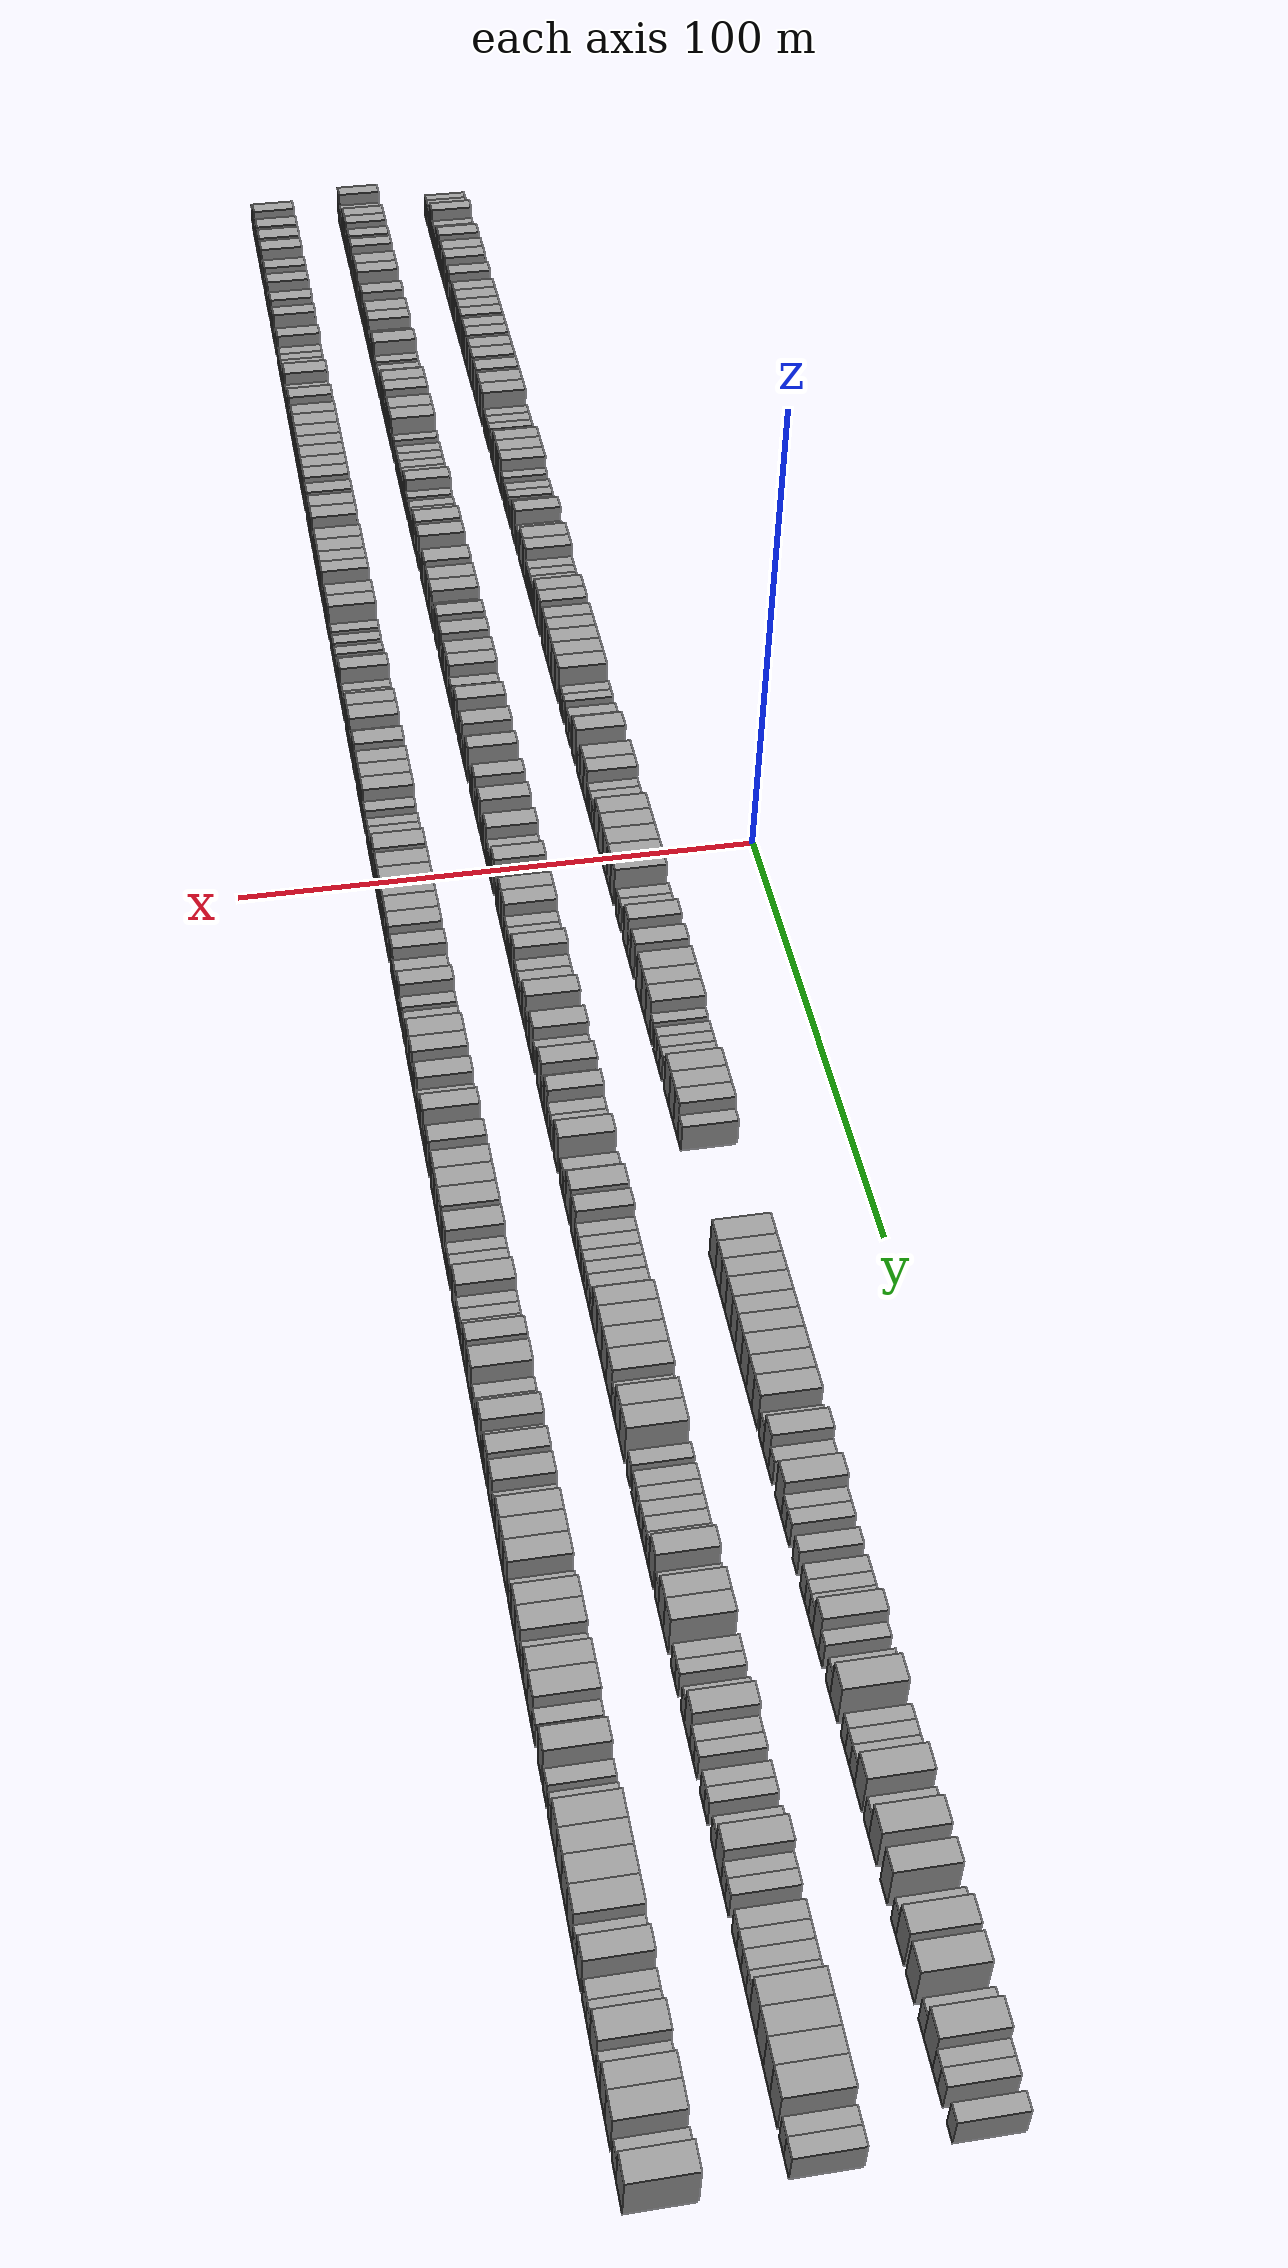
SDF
<sdf version="1.6">
 <world name="default">
  <scene>
   <sky><clouds><speed>12</speed></clouds></sky>
   <ambient>0.4 0.4 0.4 1</ambient>
   <background>0.7 0.7 0.7 1</background>
   <shadows>1</shadows>
  </scene>
  <gravity>0 0 -9.8066</gravity>
  <magnetic_field>6e-06 2.3e-05 -4.2e-05</magnetic_field>
  <physics default="0" name="default_physics" type="ode">
   <ode>
    <solver>
     <type>quick</type>
     <iters>10</iters>
     <sor>1.0</sor>
     <use_dynamic_moi_rescaling>0</use_dynamic_moi_rescaling>
    </solver>
    <constraints>
     <cfm>0</cfm>
     <erp>0.2</erp>
     <contact_max_correcting_vel>100</contact_max_correcting_vel>
     <contact_surface_layer>0.001</contact_surface_layer>
    </constraints>
   </ode>
   <max_step_size>0.004</max_step_size>
   <real_time_factor>1</real_time_factor>
   <real_time_update_rate>250</real_time_update_rate>
  </physics>
  <light name="sun" type="directional">
   <pose>0 0 10 0 0 0</pose>
   <diffuse>0.8 0.8 0.8 1</diffuse>
   <specular>0.2 0.2 0.2 1</specular>
   <attenuation>
    <range>1000</range>
    <constant>0.9</constant>
    <linear>0.01</linear>
    <quadratic>0.001</quadratic>
   </attenuation>
   <direction>-0.5 0.1 -0.9</direction>
  </light>
  <model name="building_1">
   <static>1</static>
   <pose>25.0000 -244.7638 0 0.000000 0.000000 0.000000</pose>
   <link name="link">
    <pose>0 0 3.00 0 0 0</pose>
    <collision name="collision"><geometry><box><size>10.0000 2.4723 6.0000</size></box></geometry></collision>
    <visual name="visual">
     <cast_shadows>0</cast_shadows>
     <geometry><box><size>10.0000 2.4723 6.0000</size></box></geometry>
     <material>
      <script>
       <uri>model://grey_wall/materials/scripts</uri>
       <uri>model://grey_wall/materials/textures</uri>
       <name>vrc/grey_wall</name>
      </script>
     </material>
    </visual>
   </link>
  </model>
  <model name="building_2">
   <static>1</static>
   <pose>25.0000 -242.0976 0 0.000000 0.000000 0.000000</pose>
   <link name="link">
    <pose>0 0 3.00 0 0 0</pose>
    <collision name="collision"><geometry><box><size>10.0000 2.8600 6.0000</size></box></geometry></collision>
    <visual name="visual">
     <cast_shadows>0</cast_shadows>
     <geometry><box><size>10.0000 2.8600 6.0000</size></box></geometry>
     <material>
      <script>
       <uri>model://grey_wall/materials/scripts</uri>
       <uri>model://grey_wall/materials/textures</uri>
       <name>vrc/grey_wall</name>
      </script>
     </material>
    </visual>
   </link>
  </model>
  <model name="building_3">
   <static>1</static>
   <pose>25.0000 -238.1862 0 0.000000 0.000000 0.000000</pose>
   <link name="link">
    <pose>0 0 3.00 0 0 0</pose>
    <collision name="collision"><geometry><box><size>10.0000 2.9628 6.0000</size></box></geometry></collision>
    <visual name="visual">
     <cast_shadows>0</cast_shadows>
     <geometry><box><size>10.0000 2.9628 6.0000</size></box></geometry>
     <material>
      <script>
       <uri>model://grey_wall/materials/scripts</uri>
       <uri>model://grey_wall/materials/textures</uri>
       <name>vrc/grey_wall</name>
      </script>
     </material>
    </visual>
   </link>
  </model>
  <model name="building_4">
   <static>1</static>
   <pose>25.0000 -234.8908 0 0.000000 0.000000 0.000000</pose>
   <link name="link">
    <pose>0 0 4.50 0 0 0</pose>
    <collision name="collision"><geometry><box><size>10.0000 3.6281 9.0000</size></box></geometry></collision>
    <visual name="visual">
     <cast_shadows>0</cast_shadows>
     <geometry><box><size>10.0000 3.6281 9.0000</size></box></geometry>
     <material>
      <script>
       <uri>model://grey_wall/materials/scripts</uri>
       <uri>model://grey_wall/materials/textures</uri>
       <name>vrc/grey_wall</name>
      </script>
     </material>
    </visual>
   </link>
  </model>
  <model name="building_5">
   <static>1</static>
   <pose>25.0000 -231.7991 0 0.000000 0.000000 0.000000</pose>
   <link name="link">
    <pose>0 0 3.00 0 0 0</pose>
    <collision name="collision"><geometry><box><size>10.0000 2.5554 6.0000</size></box></geometry></collision>
    <visual name="visual">
     <cast_shadows>0</cast_shadows>
     <geometry><box><size>10.0000 2.5554 6.0000</size></box></geometry>
     <material>
      <script>
       <uri>model://grey_wall/materials/scripts</uri>
       <uri>model://grey_wall/materials/textures</uri>
       <name>vrc/grey_wall</name>
      </script>
     </material>
    </visual>
   </link>
  </model>
  <model name="building_6">
   <static>1</static>
   <pose>25.0000 -229.2034 0 0.000000 0.000000 0.000000</pose>
   <link name="link">
    <pose>0 0 3.00 0 0 0</pose>
    <collision name="collision"><geometry><box><size>10.0000 2.6359 6.0000</size></box></geometry></collision>
    <visual name="visual">
     <cast_shadows>0</cast_shadows>
     <geometry><box><size>10.0000 2.6359 6.0000</size></box></geometry>
     <material>
      <script>
       <uri>model://grey_wall/materials/scripts</uri>
       <uri>model://grey_wall/materials/textures</uri>
       <name>vrc/grey_wall</name>
      </script>
     </material>
    </visual>
   </link>
  </model>
  <model name="building_7">
   <static>1</static>
   <pose>25.0000 -226.4187 0 0.000000 0.000000 0.000000</pose>
   <link name="link">
    <pose>0 0 3.00 0 0 0</pose>
    <collision name="collision"><geometry><box><size>10.0000 2.9334 6.0000</size></box></geometry></collision>
    <visual name="visual">
     <cast_shadows>0</cast_shadows>
     <geometry><box><size>10.0000 2.9334 6.0000</size></box></geometry>
     <material>
      <script>
       <uri>model://grey_wall/materials/scripts</uri>
       <uri>model://grey_wall/materials/textures</uri>
       <name>vrc/grey_wall</name>
      </script>
     </material>
    </visual>
   </link>
  </model>
  <model name="building_8">
   <static>1</static>
   <pose>25.0000 -222.8721 0 0.000000 0.000000 0.000000</pose>
   <link name="link">
    <pose>0 0 4.50 0 0 0</pose>
    <collision name="collision"><geometry><box><size>10.0000 4.1597 9.0000</size></box></geometry></collision>
    <visual name="visual">
     <cast_shadows>0</cast_shadows>
     <geometry><box><size>10.0000 4.1597 9.0000</size></box></geometry>
     <material>
      <script>
       <uri>model://grey_wall/materials/scripts</uri>
       <uri>model://grey_wall/materials/textures</uri>
       <name>vrc/grey_wall</name>
      </script>
     </material>
    </visual>
   </link>
  </model>
  <model name="building_9">
   <static>1</static>
   <pose>25.0000 -219.5267 0 0.000000 0.000000 0.000000</pose>
   <link name="link">
    <pose>0 0 3.00 0 0 0</pose>
    <collision name="collision"><geometry><box><size>10.0000 2.5312 6.0000</size></box></geometry></collision>
    <visual name="visual">
     <cast_shadows>0</cast_shadows>
     <geometry><box><size>10.0000 2.5312 6.0000</size></box></geometry>
     <material>
      <script>
       <uri>model://grey_wall/materials/scripts</uri>
       <uri>model://grey_wall/materials/textures</uri>
       <name>vrc/grey_wall</name>
      </script>
     </material>
    </visual>
   </link>
  </model>
  <model name="building_10">
   <static>1</static>
   <pose>25.0000 -216.2148 0 0.000000 0.000000 0.000000</pose>
   <link name="link">
    <pose>0 0 4.50 0 0 0</pose>
    <collision name="collision"><geometry><box><size>10.0000 4.0925 9.0000</size></box></geometry></collision>
    <visual name="visual">
     <cast_shadows>0</cast_shadows>
     <geometry><box><size>10.0000 4.0925 9.0000</size></box></geometry>
     <material>
      <script>
       <uri>model://grey_wall/materials/scripts</uri>
       <uri>model://grey_wall/materials/textures</uri>
       <name>vrc/grey_wall</name>
      </script>
     </material>
    </visual>
   </link>
  </model>
  <model name="building_11">
   <static>1</static>
   <pose>25.0000 -212.0527 0 0.000000 0.000000 0.000000</pose>
   <link name="link">
    <pose>0 0 4.50 0 0 0</pose>
    <collision name="collision"><geometry><box><size>10.0000 4.2318 9.0000</size></box></geometry></collision>
    <visual name="visual">
     <cast_shadows>0</cast_shadows>
     <geometry><box><size>10.0000 4.2318 9.0000</size></box></geometry>
     <material>
      <script>
       <uri>model://grey_wall/materials/scripts</uri>
       <uri>model://grey_wall/materials/textures</uri>
       <name>vrc/grey_wall</name>
      </script>
     </material>
    </visual>
   </link>
  </model>
  <model name="building_12">
   <static>1</static>
   <pose>25.0000 -207.7219 0 0.000000 0.000000 0.000000</pose>
   <link name="link">
    <pose>0 0 3.00 0 0 0</pose>
    <collision name="collision"><geometry><box><size>10.0000 2.4299 6.0000</size></box></geometry></collision>
    <visual name="visual">
     <cast_shadows>0</cast_shadows>
     <geometry><box><size>10.0000 2.4299 6.0000</size></box></geometry>
     <material>
      <script>
       <uri>model://grey_wall/materials/scripts</uri>
       <uri>model://grey_wall/materials/textures</uri>
       <name>vrc/grey_wall</name>
      </script>
     </material>
    </visual>
   </link>
  </model>
  <model name="building_13">
   <static>1</static>
   <pose>25.0000 -204.5237 0 0.000000 0.000000 0.000000</pose>
   <link name="link">
    <pose>0 0 4.50 0 0 0</pose>
    <collision name="collision"><geometry><box><size>10.0000 3.9663 9.0000</size></box></geometry></collision>
    <visual name="visual">
     <cast_shadows>0</cast_shadows>
     <geometry><box><size>10.0000 3.9663 9.0000</size></box></geometry>
     <material>
      <script>
       <uri>model://grey_wall/materials/scripts</uri>
       <uri>model://grey_wall/materials/textures</uri>
       <name>vrc/grey_wall</name>
      </script>
     </material>
    </visual>
   </link>
  </model>
  <model name="building_14">
   <static>1</static>
   <pose>25.0000 -201.2033 0 0.000000 0.000000 0.000000</pose>
   <link name="link">
    <pose>0 0 3.00 0 0 0</pose>
    <collision name="collision"><geometry><box><size>10.0000 2.6745 6.0000</size></box></geometry></collision>
    <visual name="visual">
     <cast_shadows>0</cast_shadows>
     <geometry><box><size>10.0000 2.6745 6.0000</size></box></geometry>
     <material>
      <script>
       <uri>model://grey_wall/materials/scripts</uri>
       <uri>model://grey_wall/materials/textures</uri>
       <name>vrc/grey_wall</name>
      </script>
     </material>
    </visual>
   </link>
  </model>
  <model name="building_15">
   <static>1</static>
   <pose>25.0000 -197.0000 0 0.000000 0.000000 0.000000</pose>
   <link name="link">
    <pose>0 0 4.50 0 0 0</pose>
    <collision name="collision"><geometry><box><size>10.0000 3.7322 9.0000</size></box></geometry></collision>
    <visual name="visual">
     <cast_shadows>0</cast_shadows>
     <geometry><box><size>10.0000 3.7322 9.0000</size></box></geometry>
     <material>
      <script>
       <uri>model://grey_wall/materials/scripts</uri>
       <uri>model://grey_wall/materials/textures</uri>
       <name>vrc/grey_wall</name>
      </script>
     </material>
    </visual>
   </link>
  </model>
  <model name="building_16">
   <static>1</static>
   <pose>25.0000 -193.0202 0 0.000000 0.000000 0.000000</pose>
   <link name="link">
    <pose>0 0 4.50 0 0 0</pose>
    <collision name="collision"><geometry><box><size>10.0000 4.2274 9.0000</size></box></geometry></collision>
    <visual name="visual">
     <cast_shadows>0</cast_shadows>
     <geometry><box><size>10.0000 4.2274 9.0000</size></box></geometry>
     <material>
      <script>
       <uri>model://grey_wall/materials/scripts</uri>
       <uri>model://grey_wall/materials/textures</uri>
       <name>vrc/grey_wall</name>
      </script>
     </material>
    </visual>
   </link>
  </model>
  <model name="building_17">
   <static>1</static>
   <pose>25.0000 -189.0595 0 0.000000 0.000000 0.000000</pose>
   <link name="link">
    <pose>0 0 4.50 0 0 0</pose>
    <collision name="collision"><geometry><box><size>10.0000 3.6940 9.0000</size></box></geometry></collision>
    <visual name="visual">
     <cast_shadows>0</cast_shadows>
     <geometry><box><size>10.0000 3.6940 9.0000</size></box></geometry>
     <material>
      <script>
       <uri>model://grey_wall/materials/scripts</uri>
       <uri>model://grey_wall/materials/textures</uri>
       <name>vrc/grey_wall</name>
      </script>
     </material>
    </visual>
   </link>
  </model>
  <model name="building_18">
   <static>1</static>
   <pose>25.0000 -185.3140 0 0.000000 0.000000 0.000000</pose>
   <link name="link">
    <pose>0 0 4.50 0 0 0</pose>
    <collision name="collision"><geometry><box><size>10.0000 3.7971 9.0000</size></box></geometry></collision>
    <visual name="visual">
     <cast_shadows>0</cast_shadows>
     <geometry><box><size>10.0000 3.7971 9.0000</size></box></geometry>
     <material>
      <script>
       <uri>model://grey_wall/materials/scripts</uri>
       <uri>model://grey_wall/materials/textures</uri>
       <name>vrc/grey_wall</name>
      </script>
     </material>
    </visual>
   </link>
  </model>
  <model name="building_19">
   <static>1</static>
   <pose>25.0000 -180.4824 0 0.000000 0.000000 0.000000</pose>
   <link name="link">
    <pose>0 0 4.50 0 0 0</pose>
    <collision name="collision"><geometry><box><size>10.0000 3.8661 9.0000</size></box></geometry></collision>
    <visual name="visual">
     <cast_shadows>0</cast_shadows>
     <geometry><box><size>10.0000 3.8661 9.0000</size></box></geometry>
     <material>
      <script>
       <uri>model://grey_wall/materials/scripts</uri>
       <uri>model://grey_wall/materials/textures</uri>
       <name>vrc/grey_wall</name>
      </script>
     </material>
    </visual>
   </link>
  </model>
  <model name="building_20">
   <static>1</static>
   <pose>25.0000 -176.5590 0 0.000000 0.000000 0.000000</pose>
   <link name="link">
    <pose>0 0 4.50 0 0 0</pose>
    <collision name="collision"><geometry><box><size>10.0000 3.9805 9.0000</size></box></geometry></collision>
    <visual name="visual">
     <cast_shadows>0</cast_shadows>
     <geometry><box><size>10.0000 3.9805 9.0000</size></box></geometry>
     <material>
      <script>
       <uri>model://grey_wall/materials/scripts</uri>
       <uri>model://grey_wall/materials/textures</uri>
       <name>vrc/grey_wall</name>
      </script>
     </material>
    </visual>
   </link>
  </model>
  <model name="building_21">
   <static>1</static>
   <pose>25.0000 -171.5504 0 0.000000 0.000000 0.000000</pose>
   <link name="link">
    <pose>0 0 4.50 0 0 0</pose>
    <collision name="collision"><geometry><box><size>10.0000 4.0368 9.0000</size></box></geometry></collision>
    <visual name="visual">
     <cast_shadows>0</cast_shadows>
     <geometry><box><size>10.0000 4.0368 9.0000</size></box></geometry>
     <material>
      <script>
       <uri>model://grey_wall/materials/scripts</uri>
       <uri>model://grey_wall/materials/textures</uri>
       <name>vrc/grey_wall</name>
      </script>
     </material>
    </visual>
   </link>
  </model>
  <model name="building_22">
   <static>1</static>
   <pose>25.0000 -167.3028 0 0.000000 0.000000 0.000000</pose>
   <link name="link">
    <pose>0 0 4.50 0 0 0</pose>
    <collision name="collision"><geometry><box><size>10.0000 4.4582 9.0000</size></box></geometry></collision>
    <visual name="visual">
     <cast_shadows>0</cast_shadows>
     <geometry><box><size>10.0000 4.4582 9.0000</size></box></geometry>
     <material>
      <script>
       <uri>model://grey_wall/materials/scripts</uri>
       <uri>model://grey_wall/materials/textures</uri>
       <name>vrc/grey_wall</name>
      </script>
     </material>
    </visual>
   </link>
  </model>
  <model name="building_23">
   <static>1</static>
   <pose>25.0000 -161.9479 0 0.000000 0.000000 0.000000</pose>
   <link name="link">
    <pose>0 0 4.50 0 0 0</pose>
    <collision name="collision"><geometry><box><size>10.0000 4.2517 9.0000</size></box></geometry></collision>
    <visual name="visual">
     <cast_shadows>0</cast_shadows>
     <geometry><box><size>10.0000 4.2517 9.0000</size></box></geometry>
     <material>
      <script>
       <uri>model://grey_wall/materials/scripts</uri>
       <uri>model://grey_wall/materials/textures</uri>
       <name>vrc/grey_wall</name>
      </script>
     </material>
    </visual>
   </link>
  </model>
  <model name="building_24">
   <static>1</static>
   <pose>25.0000 -156.5929 0 0.000000 0.000000 0.000000</pose>
   <link name="link">
    <pose>0 0 4.50 0 0 0</pose>
    <collision name="collision"><geometry><box><size>10.0000 4.4582 9.0000</size></box></geometry></collision>
    <visual name="visual">
     <cast_shadows>0</cast_shadows>
     <geometry><box><size>10.0000 4.4582 9.0000</size></box></geometry>
     <material>
      <script>
       <uri>model://grey_wall/materials/scripts</uri>
       <uri>model://grey_wall/materials/textures</uri>
       <name>vrc/grey_wall</name>
      </script>
     </material>
    </visual>
   </link>
  </model>
  <model name="building_25">
   <static>1</static>
   <pose>25.0000 -152.2064 0 0.000000 0.000000 0.000000</pose>
   <link name="link">
    <pose>0 0 4.50 0 0 0</pose>
    <collision name="collision"><geometry><box><size>10.0000 4.3148 9.0000</size></box></geometry></collision>
    <visual name="visual">
     <cast_shadows>0</cast_shadows>
     <geometry><box><size>10.0000 4.3148 9.0000</size></box></geometry>
     <material>
      <script>
       <uri>model://grey_wall/materials/scripts</uri>
       <uri>model://grey_wall/materials/textures</uri>
       <name>vrc/grey_wall</name>
      </script>
     </material>
    </visual>
   </link>
  </model>
  <model name="building_26">
   <static>1</static>
   <pose>25.0000 -146.6373 0 0.000000 0.000000 0.000000</pose>
   <link name="link">
    <pose>0 0 3.00 0 0 0</pose>
    <collision name="collision"><geometry><box><size>10.0000 2.8234 6.0000</size></box></geometry></collision>
    <visual name="visual">
     <cast_shadows>0</cast_shadows>
     <geometry><box><size>10.0000 2.8234 6.0000</size></box></geometry>
     <material>
      <script>
       <uri>model://grey_wall/materials/scripts</uri>
       <uri>model://grey_wall/materials/textures</uri>
       <name>vrc/grey_wall</name>
      </script>
     </material>
    </visual>
   </link>
  </model>
  <model name="building_27">
   <static>1</static>
   <pose>25.0000 -143.7448 0 0.000000 0.000000 0.000000</pose>
   <link name="link">
    <pose>0 0 3.00 0 0 0</pose>
    <collision name="collision"><geometry><box><size>10.0000 2.9617 6.0000</size></box></geometry></collision>
    <visual name="visual">
     <cast_shadows>0</cast_shadows>
     <geometry><box><size>10.0000 2.9617 6.0000</size></box></geometry>
     <material>
      <script>
       <uri>model://grey_wall/materials/scripts</uri>
       <uri>model://grey_wall/materials/textures</uri>
       <name>vrc/grey_wall</name>
      </script>
     </material>
    </visual>
   </link>
  </model>
  <model name="building_28">
   <static>1</static>
   <pose>25.0000 -140.9733 0 0.000000 0.000000 0.000000</pose>
   <link name="link">
    <pose>0 0 3.00 0 0 0</pose>
    <collision name="collision"><geometry><box><size>10.0000 2.5812 6.0000</size></box></geometry></collision>
    <visual name="visual">
     <cast_shadows>0</cast_shadows>
     <geometry><box><size>10.0000 2.5812 6.0000</size></box></geometry>
     <material>
      <script>
       <uri>model://grey_wall/materials/scripts</uri>
       <uri>model://grey_wall/materials/textures</uri>
       <name>vrc/grey_wall</name>
      </script>
     </material>
    </visual>
   </link>
  </model>
  <model name="building_29">
   <static>1</static>
   <pose>25.0000 -136.2262 0 0.000000 0.000000 0.000000</pose>
   <link name="link">
    <pose>0 0 3.00 0 0 0</pose>
    <collision name="collision"><geometry><box><size>10.0000 2.9131 6.0000</size></box></geometry></collision>
    <visual name="visual">
     <cast_shadows>0</cast_shadows>
     <geometry><box><size>10.0000 2.9131 6.0000</size></box></geometry>
     <material>
      <script>
       <uri>model://grey_wall/materials/scripts</uri>
       <uri>model://grey_wall/materials/textures</uri>
       <name>vrc/grey_wall</name>
      </script>
     </material>
    </visual>
   </link>
  </model>
  <model name="building_30">
   <static>1</static>
   <pose>25.0000 -132.8486 0 0.000000 0.000000 0.000000</pose>
   <link name="link">
    <pose>0 0 4.50 0 0 0</pose>
    <collision name="collision"><geometry><box><size>10.0000 3.8419 9.0000</size></box></geometry></collision>
    <visual name="visual">
     <cast_shadows>0</cast_shadows>
     <geometry><box><size>10.0000 3.8419 9.0000</size></box></geometry>
     <material>
      <script>
       <uri>model://grey_wall/materials/scripts</uri>
       <uri>model://grey_wall/materials/textures</uri>
       <name>vrc/grey_wall</name>
      </script>
     </material>
    </visual>
   </link>
  </model>
  <model name="building_31">
   <static>1</static>
   <pose>25.0000 -128.8519 0 0.000000 0.000000 0.000000</pose>
   <link name="link">
    <pose>0 0 4.50 0 0 0</pose>
    <collision name="collision"><geometry><box><size>10.0000 4.1516 9.0000</size></box></geometry></collision>
    <visual name="visual">
     <cast_shadows>0</cast_shadows>
     <geometry><box><size>10.0000 4.1516 9.0000</size></box></geometry>
     <material>
      <script>
       <uri>model://grey_wall/materials/scripts</uri>
       <uri>model://grey_wall/materials/textures</uri>
       <name>vrc/grey_wall</name>
      </script>
     </material>
    </visual>
   </link>
  </model>
  <model name="building_32">
   <static>1</static>
   <pose>25.0000 -124.8471 0 0.000000 0.000000 0.000000</pose>
   <link name="link">
    <pose>0 0 4.50 0 0 0</pose>
    <collision name="collision"><geometry><box><size>10.0000 3.8579 9.0000</size></box></geometry></collision>
    <visual name="visual">
     <cast_shadows>0</cast_shadows>
     <geometry><box><size>10.0000 3.8579 9.0000</size></box></geometry>
     <material>
      <script>
       <uri>model://grey_wall/materials/scripts</uri>
       <uri>model://grey_wall/materials/textures</uri>
       <name>vrc/grey_wall</name>
      </script>
     </material>
    </visual>
   </link>
  </model>
  <model name="building_33">
   <static>1</static>
   <pose>25.0000 -121.6327 0 0.000000 0.000000 0.000000</pose>
   <link name="link">
    <pose>0 0 3.00 0 0 0</pose>
    <collision name="collision"><geometry><box><size>10.0000 2.5709 6.0000</size></box></geometry></collision>
    <visual name="visual">
     <cast_shadows>0</cast_shadows>
     <geometry><box><size>10.0000 2.5709 6.0000</size></box></geometry>
     <material>
      <script>
       <uri>model://grey_wall/materials/scripts</uri>
       <uri>model://grey_wall/materials/textures</uri>
       <name>vrc/grey_wall</name>
      </script>
     </material>
    </visual>
   </link>
  </model>
  <model name="building_34">
   <static>1</static>
   <pose>25.0000 -117.0022 0 0.000000 0.000000 0.000000</pose>
   <link name="link">
    <pose>0 0 3.00 0 0 0</pose>
    <collision name="collision"><geometry><box><size>10.0000 2.6902 6.0000</size></box></geometry></collision>
    <visual name="visual">
     <cast_shadows>0</cast_shadows>
     <geometry><box><size>10.0000 2.6902 6.0000</size></box></geometry>
     <material>
      <script>
       <uri>model://grey_wall/materials/scripts</uri>
       <uri>model://grey_wall/materials/textures</uri>
       <name>vrc/grey_wall</name>
      </script>
     </material>
    </visual>
   </link>
  </model>
  <model name="building_35">
   <static>1</static>
   <pose>25.0000 -114.2729 0 0.000000 0.000000 0.000000</pose>
   <link name="link">
    <pose>0 0 3.00 0 0 0</pose>
    <collision name="collision"><geometry><box><size>10.0000 2.7684 6.0000</size></box></geometry></collision>
    <visual name="visual">
     <cast_shadows>0</cast_shadows>
     <geometry><box><size>10.0000 2.7684 6.0000</size></box></geometry>
     <material>
      <script>
       <uri>model://grey_wall/materials/scripts</uri>
       <uri>model://grey_wall/materials/textures</uri>
       <name>vrc/grey_wall</name>
      </script>
     </material>
    </visual>
   </link>
  </model>
  <model name="building_36">
   <static>1</static>
   <pose>25.0000 -110.6219 0 0.000000 0.000000 0.000000</pose>
   <link name="link">
    <pose>0 0 3.00 0 0 0</pose>
    <collision name="collision"><geometry><box><size>10.0000 2.5334 6.0000</size></box></geometry></collision>
    <visual name="visual">
     <cast_shadows>0</cast_shadows>
     <geometry><box><size>10.0000 2.5334 6.0000</size></box></geometry>
     <material>
      <script>
       <uri>model://grey_wall/materials/scripts</uri>
       <uri>model://grey_wall/materials/textures</uri>
       <name>vrc/grey_wall</name>
      </script>
     </material>
    </visual>
   </link>
  </model>
  <model name="building_37">
   <static>1</static>
   <pose>25.0000 -105.4284 0 0.000000 0.000000 0.000000</pose>
   <link name="link">
    <pose>0 0 4.50 0 0 0</pose>
    <collision name="collision"><geometry><box><size>10.0000 3.8535 9.0000</size></box></geometry></collision>
    <visual name="visual">
     <cast_shadows>0</cast_shadows>
     <geometry><box><size>10.0000 3.8535 9.0000</size></box></geometry>
     <material>
      <script>
       <uri>model://grey_wall/materials/scripts</uri>
       <uri>model://grey_wall/materials/textures</uri>
       <name>vrc/grey_wall</name>
      </script>
     </material>
    </visual>
   </link>
  </model>
  <model name="building_38">
   <static>1</static>
   <pose>25.0000 -101.0834 0 0.000000 0.000000 0.000000</pose>
   <link name="link">
    <pose>0 0 3.00 0 0 0</pose>
    <collision name="collision"><geometry><box><size>10.0000 2.8365 6.0000</size></box></geometry></collision>
    <visual name="visual">
     <cast_shadows>0</cast_shadows>
     <geometry><box><size>10.0000 2.8365 6.0000</size></box></geometry>
     <material>
      <script>
       <uri>model://grey_wall/materials/scripts</uri>
       <uri>model://grey_wall/materials/textures</uri>
       <name>vrc/grey_wall</name>
      </script>
     </material>
    </visual>
   </link>
  </model>
  <model name="building_39">
   <static>1</static>
   <pose>25.0000 -95.5377 0 0.000000 0.000000 0.000000</pose>
   <link name="link">
    <pose>0 0 4.50 0 0 0</pose>
    <collision name="collision"><geometry><box><size>10.0000 4.2549 9.0000</size></box></geometry></collision>
    <visual name="visual">
     <cast_shadows>0</cast_shadows>
     <geometry><box><size>10.0000 4.2549 9.0000</size></box></geometry>
     <material>
      <script>
       <uri>model://grey_wall/materials/scripts</uri>
       <uri>model://grey_wall/materials/textures</uri>
       <name>vrc/grey_wall</name>
      </script>
     </material>
    </visual>
   </link>
  </model>
  <model name="building_40">
   <static>1</static>
   <pose>25.0000 -91.4552 0 0.000000 0.000000 0.000000</pose>
   <link name="link">
    <pose>0 0 4.50 0 0 0</pose>
    <collision name="collision"><geometry><box><size>10.0000 3.9101 9.0000</size></box></geometry></collision>
    <visual name="visual">
     <cast_shadows>0</cast_shadows>
     <geometry><box><size>10.0000 3.9101 9.0000</size></box></geometry>
     <material>
      <script>
       <uri>model://grey_wall/materials/scripts</uri>
       <uri>model://grey_wall/materials/textures</uri>
       <name>vrc/grey_wall</name>
      </script>
     </material>
    </visual>
   </link>
  </model>
  <model name="building_41">
   <static>1</static>
   <pose>25.0000 -88.0144 0 0.000000 0.000000 0.000000</pose>
   <link name="link">
    <pose>0 0 3.00 0 0 0</pose>
    <collision name="collision"><geometry><box><size>10.0000 2.9714 6.0000</size></box></geometry></collision>
    <visual name="visual">
     <cast_shadows>0</cast_shadows>
     <geometry><box><size>10.0000 2.9714 6.0000</size></box></geometry>
     <material>
      <script>
       <uri>model://grey_wall/materials/scripts</uri>
       <uri>model://grey_wall/materials/textures</uri>
       <name>vrc/grey_wall</name>
      </script>
     </material>
    </visual>
   </link>
  </model>
  <model name="building_42">
   <static>1</static>
   <pose>25.0000 -85.2335 0 0.000000 0.000000 0.000000</pose>
   <link name="link">
    <pose>0 0 3.00 0 0 0</pose>
    <collision name="collision"><geometry><box><size>10.0000 2.5903 6.0000</size></box></geometry></collision>
    <visual name="visual">
     <cast_shadows>0</cast_shadows>
     <geometry><box><size>10.0000 2.5903 6.0000</size></box></geometry>
     <material>
      <script>
       <uri>model://grey_wall/materials/scripts</uri>
       <uri>model://grey_wall/materials/textures</uri>
       <name>vrc/grey_wall</name>
      </script>
     </material>
    </visual>
   </link>
  </model>
  <model name="building_43">
   <static>1</static>
   <pose>25.0000 -82.6358 0 0.000000 0.000000 0.000000</pose>
   <link name="link">
    <pose>0 0 3.00 0 0 0</pose>
    <collision name="collision"><geometry><box><size>10.0000 2.6051 6.0000</size></box></geometry></collision>
    <visual name="visual">
     <cast_shadows>0</cast_shadows>
     <geometry><box><size>10.0000 2.6051 6.0000</size></box></geometry>
     <material>
      <script>
       <uri>model://grey_wall/materials/scripts</uri>
       <uri>model://grey_wall/materials/textures</uri>
       <name>vrc/grey_wall</name>
      </script>
     </material>
    </visual>
   </link>
  </model>
  <model name="building_44">
   <static>1</static>
   <pose>25.0000 -80.0798 0 0.000000 0.000000 0.000000</pose>
   <link name="link">
    <pose>0 0 3.00 0 0 0</pose>
    <collision name="collision"><geometry><box><size>10.0000 2.5071 6.0000</size></box></geometry></collision>
    <visual name="visual">
     <cast_shadows>0</cast_shadows>
     <geometry><box><size>10.0000 2.5071 6.0000</size></box></geometry>
     <material>
      <script>
       <uri>model://grey_wall/materials/scripts</uri>
       <uri>model://grey_wall/materials/textures</uri>
       <name>vrc/grey_wall</name>
      </script>
     </material>
    </visual>
   </link>
  </model>
  <model name="building_45">
   <static>1</static>
   <pose>25.0000 -76.8473 0 0.000000 0.000000 0.000000</pose>
   <link name="link">
    <pose>0 0 4.50 0 0 0</pose>
    <collision name="collision"><geometry><box><size>10.0000 3.9578 9.0000</size></box></geometry></collision>
    <visual name="visual">
     <cast_shadows>0</cast_shadows>
     <geometry><box><size>10.0000 3.9578 9.0000</size></box></geometry>
     <material>
      <script>
       <uri>model://grey_wall/materials/scripts</uri>
       <uri>model://grey_wall/materials/textures</uri>
       <name>vrc/grey_wall</name>
      </script>
     </material>
    </visual>
   </link>
  </model>
  <model name="building_46">
   <static>1</static>
   <pose>25.0000 -72.9065 0 0.000000 0.000000 0.000000</pose>
   <link name="link">
    <pose>0 0 4.50 0 0 0</pose>
    <collision name="collision"><geometry><box><size>10.0000 3.9238 9.0000</size></box></geometry></collision>
    <visual name="visual">
     <cast_shadows>0</cast_shadows>
     <geometry><box><size>10.0000 3.9238 9.0000</size></box></geometry>
     <material>
      <script>
       <uri>model://grey_wall/materials/scripts</uri>
       <uri>model://grey_wall/materials/textures</uri>
       <name>vrc/grey_wall</name>
      </script>
     </material>
    </visual>
   </link>
  </model>
  <model name="building_47">
   <static>1</static>
   <pose>25.0000 -67.0962 0 0.000000 0.000000 0.000000</pose>
   <link name="link">
    <pose>0 0 4.50 0 0 0</pose>
    <collision name="collision"><geometry><box><size>10.0000 3.6969 9.0000</size></box></geometry></collision>
    <visual name="visual">
     <cast_shadows>0</cast_shadows>
     <geometry><box><size>10.0000 3.6969 9.0000</size></box></geometry>
     <material>
      <script>
       <uri>model://grey_wall/materials/scripts</uri>
       <uri>model://grey_wall/materials/textures</uri>
       <name>vrc/grey_wall</name>
      </script>
     </material>
    </visual>
   </link>
  </model>
  <model name="building_48">
   <static>1</static>
   <pose>25.0000 -63.3250 0 0.000000 0.000000 0.000000</pose>
   <link name="link">
    <pose>0 0 4.50 0 0 0</pose>
    <collision name="collision"><geometry><box><size>10.0000 3.8456 9.0000</size></box></geometry></collision>
    <visual name="visual">
     <cast_shadows>0</cast_shadows>
     <geometry><box><size>10.0000 3.8456 9.0000</size></box></geometry>
     <material>
      <script>
       <uri>model://grey_wall/materials/scripts</uri>
       <uri>model://grey_wall/materials/textures</uri>
       <name>vrc/grey_wall</name>
      </script>
     </material>
    </visual>
   </link>
  </model>
  <model name="building_49">
   <static>1</static>
   <pose>25.0000 -59.2501 0 0.000000 0.000000 0.000000</pose>
   <link name="link">
    <pose>0 0 4.50 0 0 0</pose>
    <collision name="collision"><geometry><box><size>10.0000 4.3040 9.0000</size></box></geometry></collision>
    <visual name="visual">
     <cast_shadows>0</cast_shadows>
     <geometry><box><size>10.0000 4.3040 9.0000</size></box></geometry>
     <material>
      <script>
       <uri>model://grey_wall/materials/scripts</uri>
       <uri>model://grey_wall/materials/textures</uri>
       <name>vrc/grey_wall</name>
      </script>
     </material>
    </visual>
   </link>
  </model>
  <model name="building_50">
   <static>1</static>
   <pose>25.0000 -54.9398 0 0.000000 0.000000 0.000000</pose>
   <link name="link">
    <pose>0 0 4.50 0 0 0</pose>
    <collision name="collision"><geometry><box><size>10.0000 4.3167 9.0000</size></box></geometry></collision>
    <visual name="visual">
     <cast_shadows>0</cast_shadows>
     <geometry><box><size>10.0000 4.3167 9.0000</size></box></geometry>
     <material>
      <script>
       <uri>model://grey_wall/materials/scripts</uri>
       <uri>model://grey_wall/materials/textures</uri>
       <name>vrc/grey_wall</name>
      </script>
     </material>
    </visual>
   </link>
  </model>
  <model name="building_51">
   <static>1</static>
   <pose>25.0000 -50.6301 0 0.000000 0.000000 0.000000</pose>
   <link name="link">
    <pose>0 0 4.50 0 0 0</pose>
    <collision name="collision"><geometry><box><size>10.0000 4.3026 9.0000</size></box></geometry></collision>
    <visual name="visual">
     <cast_shadows>0</cast_shadows>
     <geometry><box><size>10.0000 4.3026 9.0000</size></box></geometry>
     <material>
      <script>
       <uri>model://grey_wall/materials/scripts</uri>
       <uri>model://grey_wall/materials/textures</uri>
       <name>vrc/grey_wall</name>
      </script>
     </material>
    </visual>
   </link>
  </model>
  <model name="building_52">
   <static>1</static>
   <pose>25.0000 -45.1680 0 0.000000 0.000000 0.000000</pose>
   <link name="link">
    <pose>0 0 3.00 0 0 0</pose>
    <collision name="collision"><geometry><box><size>10.0000 2.6216 6.0000</size></box></geometry></collision>
    <visual name="visual">
     <cast_shadows>0</cast_shadows>
     <geometry><box><size>10.0000 2.6216 6.0000</size></box></geometry>
     <material>
      <script>
       <uri>model://grey_wall/materials/scripts</uri>
       <uri>model://grey_wall/materials/textures</uri>
       <name>vrc/grey_wall</name>
      </script>
     </material>
    </visual>
   </link>
  </model>
  <model name="building_53">
   <static>1</static>
   <pose>25.0000 -42.6531 0 0.000000 0.000000 0.000000</pose>
   <link name="link">
    <pose>0 0 3.00 0 0 0</pose>
    <collision name="collision"><geometry><box><size>10.0000 2.4082 6.0000</size></box></geometry></collision>
    <visual name="visual">
     <cast_shadows>0</cast_shadows>
     <geometry><box><size>10.0000 2.4082 6.0000</size></box></geometry>
     <material>
      <script>
       <uri>model://grey_wall/materials/scripts</uri>
       <uri>model://grey_wall/materials/textures</uri>
       <name>vrc/grey_wall</name>
      </script>
     </material>
    </visual>
   </link>
  </model>
  <model name="building_54">
   <static>1</static>
   <pose>25.0000 -38.0343 0 0.000000 0.000000 0.000000</pose>
   <link name="link">
    <pose>0 0 3.00 0 0 0</pose>
    <collision name="collision"><geometry><box><size>10.0000 2.8293 6.0000</size></box></geometry></collision>
    <visual name="visual">
     <cast_shadows>0</cast_shadows>
     <geometry><box><size>10.0000 2.8293 6.0000</size></box></geometry>
     <material>
      <script>
       <uri>model://grey_wall/materials/scripts</uri>
       <uri>model://grey_wall/materials/textures</uri>
       <name>vrc/grey_wall</name>
      </script>
     </material>
    </visual>
   </link>
  </model>
  <model name="building_55">
   <static>1</static>
   <pose>25.0000 -35.2794 0 0.000000 0.000000 0.000000</pose>
   <link name="link">
    <pose>0 0 3.00 0 0 0</pose>
    <collision name="collision"><geometry><box><size>10.0000 2.6806 6.0000</size></box></geometry></collision>
    <visual name="visual">
     <cast_shadows>0</cast_shadows>
     <geometry><box><size>10.0000 2.6806 6.0000</size></box></geometry>
     <material>
      <script>
       <uri>model://grey_wall/materials/scripts</uri>
       <uri>model://grey_wall/materials/textures</uri>
       <name>vrc/grey_wall</name>
      </script>
     </material>
    </visual>
   </link>
  </model>
  <model name="building_56">
   <static>1</static>
   <pose>25.0000 -30.8099 0 0.000000 0.000000 0.000000</pose>
   <link name="link">
    <pose>0 0 4.50 0 0 0</pose>
    <collision name="collision"><geometry><box><size>10.0000 4.2584 9.0000</size></box></geometry></collision>
    <visual name="visual">
     <cast_shadows>0</cast_shadows>
     <geometry><box><size>10.0000 4.2584 9.0000</size></box></geometry>
     <material>
      <script>
       <uri>model://grey_wall/materials/scripts</uri>
       <uri>model://grey_wall/materials/textures</uri>
       <name>vrc/grey_wall</name>
      </script>
     </material>
    </visual>
   </link>
  </model>
  <model name="building_57">
   <static>1</static>
   <pose>25.0000 -25.3674 0 0.000000 0.000000 0.000000</pose>
   <link name="link">
    <pose>0 0 3.00 0 0 0</pose>
    <collision name="collision"><geometry><box><size>10.0000 2.6267 6.0000</size></box></geometry></collision>
    <visual name="visual">
     <cast_shadows>0</cast_shadows>
     <geometry><box><size>10.0000 2.6267 6.0000</size></box></geometry>
     <material>
      <script>
       <uri>model://grey_wall/materials/scripts</uri>
       <uri>model://grey_wall/materials/textures</uri>
       <name>vrc/grey_wall</name>
      </script>
     </material>
    </visual>
   </link>
  </model>
  <model name="building_58">
   <static>1</static>
   <pose>25.0000 -22.0043 0 0.000000 0.000000 0.000000</pose>
   <link name="link">
    <pose>0 0 4.50 0 0 0</pose>
    <collision name="collision"><geometry><box><size>10.0000 4.0994 9.0000</size></box></geometry></collision>
    <visual name="visual">
     <cast_shadows>0</cast_shadows>
     <geometry><box><size>10.0000 4.0994 9.0000</size></box></geometry>
     <material>
      <script>
       <uri>model://grey_wall/materials/scripts</uri>
       <uri>model://grey_wall/materials/textures</uri>
       <name>vrc/grey_wall</name>
      </script>
     </material>
    </visual>
   </link>
  </model>
  <model name="building_59">
   <static>1</static>
   <pose>25.0000 -18.0074 0 0.000000 0.000000 0.000000</pose>
   <link name="link">
    <pose>0 0 4.50 0 0 0</pose>
    <collision name="collision"><geometry><box><size>10.0000 3.8946 9.0000</size></box></geometry></collision>
    <visual name="visual">
     <cast_shadows>0</cast_shadows>
     <geometry><box><size>10.0000 3.8946 9.0000</size></box></geometry>
     <material>
      <script>
       <uri>model://grey_wall/materials/scripts</uri>
       <uri>model://grey_wall/materials/textures</uri>
       <name>vrc/grey_wall</name>
      </script>
     </material>
    </visual>
   </link>
  </model>
  <model name="building_60">
   <static>1</static>
   <pose>25.0000 -14.8395 0 0.000000 0.000000 0.000000</pose>
   <link name="link">
    <pose>0 0 3.00 0 0 0</pose>
    <collision name="collision"><geometry><box><size>10.0000 2.4411 6.0000</size></box></geometry></collision>
    <visual name="visual">
     <cast_shadows>0</cast_shadows>
     <geometry><box><size>10.0000 2.4411 6.0000</size></box></geometry>
     <material>
      <script>
       <uri>model://grey_wall/materials/scripts</uri>
       <uri>model://grey_wall/materials/textures</uri>
       <name>vrc/grey_wall</name>
      </script>
     </material>
    </visual>
   </link>
  </model>
  <model name="building_61">
   <static>1</static>
   <pose>25.0000 -12.3281 0 0.000000 0.000000 0.000000</pose>
   <link name="link">
    <pose>0 0 3.00 0 0 0</pose>
    <collision name="collision"><geometry><box><size>10.0000 2.5816 6.0000</size></box></geometry></collision>
    <visual name="visual">
     <cast_shadows>0</cast_shadows>
     <geometry><box><size>10.0000 2.5816 6.0000</size></box></geometry>
     <material>
      <script>
       <uri>model://grey_wall/materials/scripts</uri>
       <uri>model://grey_wall/materials/textures</uri>
       <name>vrc/grey_wall</name>
      </script>
     </material>
    </visual>
   </link>
  </model>
  <model name="building_62">
   <static>1</static>
   <pose>25.0000 -9.5832 0 0.000000 0.000000 0.000000</pose>
   <link name="link">
    <pose>0 0 3.00 0 0 0</pose>
    <collision name="collision"><geometry><box><size>10.0000 2.9084 6.0000</size></box></geometry></collision>
    <visual name="visual">
     <cast_shadows>0</cast_shadows>
     <geometry><box><size>10.0000 2.9084 6.0000</size></box></geometry>
     <material>
      <script>
       <uri>model://grey_wall/materials/scripts</uri>
       <uri>model://grey_wall/materials/textures</uri>
       <name>vrc/grey_wall</name>
      </script>
     </material>
    </visual>
   </link>
  </model>
  <model name="building_63">
   <static>1</static>
   <pose>25.0000 -5.9240 0 0.000000 0.000000 0.000000</pose>
   <link name="link">
    <pose>0 0 4.50 0 0 0</pose>
    <collision name="collision"><geometry><box><size>10.0000 4.4099 9.0000</size></box></geometry></collision>
    <visual name="visual">
     <cast_shadows>0</cast_shadows>
     <geometry><box><size>10.0000 4.4099 9.0000</size></box></geometry>
     <material>
      <script>
       <uri>model://grey_wall/materials/scripts</uri>
       <uri>model://grey_wall/materials/textures</uri>
       <name>vrc/grey_wall</name>
      </script>
     </material>
    </visual>
   </link>
  </model>
  <model name="building_64">
   <static>1</static>
   <pose>25.0000 -1.5199 0 0.000000 0.000000 0.000000</pose>
   <link name="link">
    <pose>0 0 4.50 0 0 0</pose>
    <collision name="collision"><geometry><box><size>10.0000 4.3984 9.0000</size></box></geometry></collision>
    <visual name="visual">
     <cast_shadows>0</cast_shadows>
     <geometry><box><size>10.0000 4.3984 9.0000</size></box></geometry>
     <material>
      <script>
       <uri>model://grey_wall/materials/scripts</uri>
       <uri>model://grey_wall/materials/textures</uri>
       <name>vrc/grey_wall</name>
      </script>
     </material>
    </visual>
   </link>
  </model>
  <model name="building_65">
   <static>1</static>
   <pose>25.0000 2.9038 0 0.000000 0.000000 0.000000</pose>
   <link name="link">
    <pose>0 0 4.50 0 0 0</pose>
    <collision name="collision"><geometry><box><size>10.0000 4.4490 9.0000</size></box></geometry></collision>
    <visual name="visual">
     <cast_shadows>0</cast_shadows>
     <geometry><box><size>10.0000 4.4490 9.0000</size></box></geometry>
     <material>
      <script>
       <uri>model://grey_wall/materials/scripts</uri>
       <uri>model://grey_wall/materials/textures</uri>
       <name>vrc/grey_wall</name>
      </script>
     </material>
    </visual>
   </link>
  </model>
  <model name="building_66">
   <static>1</static>
   <pose>25.0000 6.9546 0 0.000000 0.000000 0.000000</pose>
   <link name="link">
    <pose>0 0 4.50 0 0 0</pose>
    <collision name="collision"><geometry><box><size>10.0000 3.6524 9.0000</size></box></geometry></collision>
    <visual name="visual">
     <cast_shadows>0</cast_shadows>
     <geometry><box><size>10.0000 3.6524 9.0000</size></box></geometry>
     <material>
      <script>
       <uri>model://grey_wall/materials/scripts</uri>
       <uri>model://grey_wall/materials/textures</uri>
       <name>vrc/grey_wall</name>
      </script>
     </material>
    </visual>
   </link>
  </model>
  <model name="building_67">
   <static>1</static>
   <pose>25.0000 10.6496 0 0.000000 0.000000 0.000000</pose>
   <link name="link">
    <pose>0 0 4.50 0 0 0</pose>
    <collision name="collision"><geometry><box><size>10.0000 3.7375 9.0000</size></box></geometry></collision>
    <visual name="visual">
     <cast_shadows>0</cast_shadows>
     <geometry><box><size>10.0000 3.7375 9.0000</size></box></geometry>
     <material>
      <script>
       <uri>model://grey_wall/materials/scripts</uri>
       <uri>model://grey_wall/materials/textures</uri>
       <name>vrc/grey_wall</name>
      </script>
     </material>
    </visual>
   </link>
  </model>
  <model name="building_68">
   <static>1</static>
   <pose>25.0000 15.8552 0 0.000000 0.000000 0.000000</pose>
   <link name="link">
    <pose>0 0 3.00 0 0 0</pose>
    <collision name="collision"><geometry><box><size>10.0000 2.6739 6.0000</size></box></geometry></collision>
    <visual name="visual">
     <cast_shadows>0</cast_shadows>
     <geometry><box><size>10.0000 2.6739 6.0000</size></box></geometry>
     <material>
      <script>
       <uri>model://grey_wall/materials/scripts</uri>
       <uri>model://grey_wall/materials/textures</uri>
       <name>vrc/grey_wall</name>
      </script>
     </material>
    </visual>
   </link>
  </model>
  <model name="building_69">
   <static>1</static>
   <pose>25.0000 18.6570 0 0.000000 0.000000 0.000000</pose>
   <link name="link">
    <pose>0 0 3.00 0 0 0</pose>
    <collision name="collision"><geometry><box><size>10.0000 2.9297 6.0000</size></box></geometry></collision>
    <visual name="visual">
     <cast_shadows>0</cast_shadows>
     <geometry><box><size>10.0000 2.9297 6.0000</size></box></geometry>
     <material>
      <script>
       <uri>model://grey_wall/materials/scripts</uri>
       <uri>model://grey_wall/materials/textures</uri>
       <name>vrc/grey_wall</name>
      </script>
     </material>
    </visual>
   </link>
  </model>
  <model name="building_70">
   <static>1</static>
   <pose>25.0000 24.0942 0 0.000000 0.000000 0.000000</pose>
   <link name="link">
    <pose>0 0 4.50 0 0 0</pose>
    <collision name="collision"><geometry><box><size>10.0000 3.9446 9.0000</size></box></geometry></collision>
    <visual name="visual">
     <cast_shadows>0</cast_shadows>
     <geometry><box><size>10.0000 3.9446 9.0000</size></box></geometry>
     <material>
      <script>
       <uri>model://grey_wall/materials/scripts</uri>
       <uri>model://grey_wall/materials/textures</uri>
       <name>vrc/grey_wall</name>
      </script>
     </material>
    </visual>
   </link>
  </model>
  <model name="building_71">
   <static>1</static>
   <pose>25.0000 27.3878 0 0.000000 0.000000 0.000000</pose>
   <link name="link">
    <pose>0 0 3.00 0 0 0</pose>
    <collision name="collision"><geometry><box><size>10.0000 2.6427 6.0000</size></box></geometry></collision>
    <visual name="visual">
     <cast_shadows>0</cast_shadows>
     <geometry><box><size>10.0000 2.6427 6.0000</size></box></geometry>
     <material>
      <script>
       <uri>model://grey_wall/materials/scripts</uri>
       <uri>model://grey_wall/materials/textures</uri>
       <name>vrc/grey_wall</name>
      </script>
     </material>
    </visual>
   </link>
  </model>
  <model name="building_72">
   <static>1</static>
   <pose>25.0000 30.7249 0 0.000000 0.000000 0.000000</pose>
   <link name="link">
    <pose>0 0 4.50 0 0 0</pose>
    <collision name="collision"><geometry><box><size>10.0000 4.0315 9.0000</size></box></geometry></collision>
    <visual name="visual">
     <cast_shadows>0</cast_shadows>
     <geometry><box><size>10.0000 4.0315 9.0000</size></box></geometry>
     <material>
      <script>
       <uri>model://grey_wall/materials/scripts</uri>
       <uri>model://grey_wall/materials/textures</uri>
       <name>vrc/grey_wall</name>
      </script>
     </material>
    </visual>
   </link>
  </model>
  <model name="building_73">
   <static>1</static>
   <pose>25.0000 36.9864 0 0.000000 0.000000 0.000000</pose>
   <link name="link">
    <pose>0 0 4.50 0 0 0</pose>
    <collision name="collision"><geometry><box><size>10.0000 4.4914 9.0000</size></box></geometry></collision>
    <visual name="visual">
     <cast_shadows>0</cast_shadows>
     <geometry><box><size>10.0000 4.4914 9.0000</size></box></geometry>
     <material>
      <script>
       <uri>model://grey_wall/materials/scripts</uri>
       <uri>model://grey_wall/materials/textures</uri>
       <name>vrc/grey_wall</name>
      </script>
     </material>
    </visual>
   </link>
  </model>
  <model name="building_74">
   <static>1</static>
   <pose>25.0000 41.2148 0 0.000000 0.000000 0.000000</pose>
   <link name="link">
    <pose>0 0 4.50 0 0 0</pose>
    <collision name="collision"><geometry><box><size>10.0000 3.9655 9.0000</size></box></geometry></collision>
    <visual name="visual">
     <cast_shadows>0</cast_shadows>
     <geometry><box><size>10.0000 3.9655 9.0000</size></box></geometry>
     <material>
      <script>
       <uri>model://grey_wall/materials/scripts</uri>
       <uri>model://grey_wall/materials/textures</uri>
       <name>vrc/grey_wall</name>
      </script>
     </material>
    </visual>
   </link>
  </model>
  <model name="building_75">
   <static>1</static>
   <pose>25.0000 45.3831 0 0.000000 0.000000 0.000000</pose>
   <link name="link">
    <pose>0 0 4.50 0 0 0</pose>
    <collision name="collision"><geometry><box><size>10.0000 4.3713 9.0000</size></box></geometry></collision>
    <visual name="visual">
     <cast_shadows>0</cast_shadows>
     <geometry><box><size>10.0000 4.3713 9.0000</size></box></geometry>
     <material>
      <script>
       <uri>model://grey_wall/materials/scripts</uri>
       <uri>model://grey_wall/materials/textures</uri>
       <name>vrc/grey_wall</name>
      </script>
     </material>
    </visual>
   </link>
  </model>
  <model name="building_76">
   <static>1</static>
   <pose>25.0000 48.7831 0 0.000000 0.000000 0.000000</pose>
   <link name="link">
    <pose>0 0 3.00 0 0 0</pose>
    <collision name="collision"><geometry><box><size>10.0000 2.4286 6.0000</size></box></geometry></collision>
    <visual name="visual">
     <cast_shadows>0</cast_shadows>
     <geometry><box><size>10.0000 2.4286 6.0000</size></box></geometry>
     <material>
      <script>
       <uri>model://grey_wall/materials/scripts</uri>
       <uri>model://grey_wall/materials/textures</uri>
       <name>vrc/grey_wall</name>
      </script>
     </material>
    </visual>
   </link>
  </model>
  <model name="building_77">
   <static>1</static>
   <pose>25.0000 52.2025 0 0.000000 0.000000 0.000000</pose>
   <link name="link">
    <pose>0 0 3.00 0 0 0</pose>
    <collision name="collision"><geometry><box><size>10.0000 2.4101 6.0000</size></box></geometry></collision>
    <visual name="visual">
     <cast_shadows>0</cast_shadows>
     <geometry><box><size>10.0000 2.4101 6.0000</size></box></geometry>
     <material>
      <script>
       <uri>model://grey_wall/materials/scripts</uri>
       <uri>model://grey_wall/materials/textures</uri>
       <name>vrc/grey_wall</name>
      </script>
     </material>
    </visual>
   </link>
  </model>
  <model name="building_78">
   <static>1</static>
   <pose>25.0000 54.7113 0 0.000000 0.000000 0.000000</pose>
   <link name="link">
    <pose>0 0 3.00 0 0 0</pose>
    <collision name="collision"><geometry><box><size>10.0000 2.6075 6.0000</size></box></geometry></collision>
    <visual name="visual">
     <cast_shadows>0</cast_shadows>
     <geometry><box><size>10.0000 2.6075 6.0000</size></box></geometry>
     <material>
      <script>
       <uri>model://grey_wall/materials/scripts</uri>
       <uri>model://grey_wall/materials/textures</uri>
       <name>vrc/grey_wall</name>
      </script>
     </material>
    </visual>
   </link>
  </model>
  <model name="building_79">
   <static>1</static>
   <pose>25.0000 57.2713 0 0.000000 0.000000 0.000000</pose>
   <link name="link">
    <pose>0 0 3.00 0 0 0</pose>
    <collision name="collision"><geometry><box><size>10.0000 2.5126 6.0000</size></box></geometry></collision>
    <visual name="visual">
     <cast_shadows>0</cast_shadows>
     <geometry><box><size>10.0000 2.5126 6.0000</size></box></geometry>
     <material>
      <script>
       <uri>model://grey_wall/materials/scripts</uri>
       <uri>model://grey_wall/materials/textures</uri>
       <name>vrc/grey_wall</name>
      </script>
     </material>
    </visual>
   </link>
  </model>
  <model name="building_80">
   <static>1</static>
   <pose>25.0000 62.6492 0 0.000000 0.000000 0.000000</pose>
   <link name="link">
    <pose>0 0 4.50 0 0 0</pose>
    <collision name="collision"><geometry><box><size>10.0000 4.2431 9.0000</size></box></geometry></collision>
    <visual name="visual">
     <cast_shadows>0</cast_shadows>
     <geometry><box><size>10.0000 4.2431 9.0000</size></box></geometry>
     <material>
      <script>
       <uri>model://grey_wall/materials/scripts</uri>
       <uri>model://grey_wall/materials/textures</uri>
       <name>vrc/grey_wall</name>
      </script>
     </material>
    </visual>
   </link>
  </model>
  <model name="building_81">
   <static>1</static>
   <pose>25.0000 66.7726 0 0.000000 0.000000 0.000000</pose>
   <link name="link">
    <pose>0 0 4.50 0 0 0</pose>
    <collision name="collision"><geometry><box><size>10.0000 4.0038 9.0000</size></box></geometry></collision>
    <visual name="visual">
     <cast_shadows>0</cast_shadows>
     <geometry><box><size>10.0000 4.0038 9.0000</size></box></geometry>
     <material>
      <script>
       <uri>model://grey_wall/materials/scripts</uri>
       <uri>model://grey_wall/materials/textures</uri>
       <name>vrc/grey_wall</name>
      </script>
     </material>
    </visual>
   </link>
  </model>
  <model name="building_82">
   <static>1</static>
   <pose>25.0000 70.6003 0 0.000000 0.000000 0.000000</pose>
   <link name="link">
    <pose>0 0 4.50 0 0 0</pose>
    <collision name="collision"><geometry><box><size>10.0000 3.6515 9.0000</size></box></geometry></collision>
    <visual name="visual">
     <cast_shadows>0</cast_shadows>
     <geometry><box><size>10.0000 3.6515 9.0000</size></box></geometry>
     <material>
      <script>
       <uri>model://grey_wall/materials/scripts</uri>
       <uri>model://grey_wall/materials/textures</uri>
       <name>vrc/grey_wall</name>
      </script>
     </material>
    </visual>
   </link>
  </model>
  <model name="building_83">
   <static>1</static>
   <pose>25.0000 73.8498 0 0.000000 0.000000 0.000000</pose>
   <link name="link">
    <pose>0 0 3.00 0 0 0</pose>
    <collision name="collision"><geometry><box><size>10.0000 2.8474 6.0000</size></box></geometry></collision>
    <visual name="visual">
     <cast_shadows>0</cast_shadows>
     <geometry><box><size>10.0000 2.8474 6.0000</size></box></geometry>
     <material>
      <script>
       <uri>model://grey_wall/materials/scripts</uri>
       <uri>model://grey_wall/materials/textures</uri>
       <name>vrc/grey_wall</name>
      </script>
     </material>
    </visual>
   </link>
  </model>
  <model name="building_84">
   <static>1</static>
   <pose>25.0000 100.9925 0 0.000000 0.000000 0.000000</pose>
   <link name="link">
    <pose>0 0 4.50 0 0 0</pose>
    <collision name="collision"><geometry><box><size>10.0000 4.4793 9.0000</size></box></geometry></collision>
    <visual name="visual">
     <cast_shadows>0</cast_shadows>
     <geometry><box><size>10.0000 4.4793 9.0000</size></box></geometry>
     <material>
      <script>
       <uri>model://grey_wall/materials/scripts</uri>
       <uri>model://grey_wall/materials/textures</uri>
       <name>vrc/grey_wall</name>
      </script>
     </material>
    </visual>
   </link>
  </model>
  <model name="building_85">
   <static>1</static>
   <pose>25.0000 105.1284 0 0.000000 0.000000 0.000000</pose>
   <link name="link">
    <pose>0 0 4.50 0 0 0</pose>
    <collision name="collision"><geometry><box><size>10.0000 3.7925 9.0000</size></box></geometry></collision>
    <visual name="visual">
     <cast_shadows>0</cast_shadows>
     <geometry><box><size>10.0000 3.7925 9.0000</size></box></geometry>
     <material>
      <script>
       <uri>model://grey_wall/materials/scripts</uri>
       <uri>model://grey_wall/materials/textures</uri>
       <name>vrc/grey_wall</name>
      </script>
     </material>
    </visual>
   </link>
  </model>
  <model name="building_86">
   <static>1</static>
   <pose>25.0000 108.9590 0 0.000000 0.000000 0.000000</pose>
   <link name="link">
    <pose>0 0 4.50 0 0 0</pose>
    <collision name="collision"><geometry><box><size>10.0000 3.8688 9.0000</size></box></geometry></collision>
    <visual name="visual">
     <cast_shadows>0</cast_shadows>
     <geometry><box><size>10.0000 3.8688 9.0000</size></box></geometry>
     <material>
      <script>
       <uri>model://grey_wall/materials/scripts</uri>
       <uri>model://grey_wall/materials/textures</uri>
       <name>vrc/grey_wall</name>
      </script>
     </material>
    </visual>
   </link>
  </model>
  <model name="building_87">
   <static>1</static>
   <pose>25.0000 112.9441 0 0.000000 0.000000 0.000000</pose>
   <link name="link">
    <pose>0 0 4.50 0 0 0</pose>
    <collision name="collision"><geometry><box><size>10.0000 4.1012 9.0000</size></box></geometry></collision>
    <visual name="visual">
     <cast_shadows>0</cast_shadows>
     <geometry><box><size>10.0000 4.1012 9.0000</size></box></geometry>
     <material>
      <script>
       <uri>model://grey_wall/materials/scripts</uri>
       <uri>model://grey_wall/materials/textures</uri>
       <name>vrc/grey_wall</name>
      </script>
     </material>
    </visual>
   </link>
  </model>
  <model name="building_88">
   <static>1</static>
   <pose>25.0000 116.8053 0 0.000000 0.000000 0.000000</pose>
   <link name="link">
    <pose>0 0 4.50 0 0 0</pose>
    <collision name="collision"><geometry><box><size>10.0000 3.6213 9.0000</size></box></geometry></collision>
    <visual name="visual">
     <cast_shadows>0</cast_shadows>
     <geometry><box><size>10.0000 3.6213 9.0000</size></box></geometry>
     <material>
      <script>
       <uri>model://grey_wall/materials/scripts</uri>
       <uri>model://grey_wall/materials/textures</uri>
       <name>vrc/grey_wall</name>
      </script>
     </material>
    </visual>
   </link>
  </model>
  <model name="building_89">
   <static>1</static>
   <pose>25.0000 120.5786 0 0.000000 0.000000 0.000000</pose>
   <link name="link">
    <pose>0 0 4.50 0 0 0</pose>
    <collision name="collision"><geometry><box><size>10.0000 3.9252 9.0000</size></box></geometry></collision>
    <visual name="visual">
     <cast_shadows>0</cast_shadows>
     <geometry><box><size>10.0000 3.9252 9.0000</size></box></geometry>
     <material>
      <script>
       <uri>model://grey_wall/materials/scripts</uri>
       <uri>model://grey_wall/materials/textures</uri>
       <name>vrc/grey_wall</name>
      </script>
     </material>
    </visual>
   </link>
  </model>
  <model name="building_90">
   <static>1</static>
   <pose>25.0000 124.7098 0 0.000000 0.000000 0.000000</pose>
   <link name="link">
    <pose>0 0 4.50 0 0 0</pose>
    <collision name="collision"><geometry><box><size>10.0000 4.3372 9.0000</size></box></geometry></collision>
    <visual name="visual">
     <cast_shadows>0</cast_shadows>
     <geometry><box><size>10.0000 4.3372 9.0000</size></box></geometry>
     <material>
      <script>
       <uri>model://grey_wall/materials/scripts</uri>
       <uri>model://grey_wall/materials/textures</uri>
       <name>vrc/grey_wall</name>
      </script>
     </material>
    </visual>
   </link>
  </model>
  <model name="building_91">
   <static>1</static>
   <pose>25.0000 128.8318 0 0.000000 0.000000 0.000000</pose>
   <link name="link">
    <pose>0 0 4.50 0 0 0</pose>
    <collision name="collision"><geometry><box><size>10.0000 3.9068 9.0000</size></box></geometry></collision>
    <visual name="visual">
     <cast_shadows>0</cast_shadows>
     <geometry><box><size>10.0000 3.9068 9.0000</size></box></geometry>
     <material>
      <script>
       <uri>model://grey_wall/materials/scripts</uri>
       <uri>model://grey_wall/materials/textures</uri>
       <name>vrc/grey_wall</name>
      </script>
     </material>
    </visual>
   </link>
  </model>
  <model name="building_92">
   <static>1</static>
   <pose>25.0000 132.8733 0 0.000000 0.000000 0.000000</pose>
   <link name="link">
    <pose>0 0 4.50 0 0 0</pose>
    <collision name="collision"><geometry><box><size>10.0000 4.1762 9.0000</size></box></geometry></collision>
    <visual name="visual">
     <cast_shadows>0</cast_shadows>
     <geometry><box><size>10.0000 4.1762 9.0000</size></box></geometry>
     <material>
      <script>
       <uri>model://grey_wall/materials/scripts</uri>
       <uri>model://grey_wall/materials/textures</uri>
       <name>vrc/grey_wall</name>
      </script>
     </material>
    </visual>
   </link>
  </model>
  <model name="building_93">
   <static>1</static>
   <pose>25.0000 137.3470 0 0.000000 0.000000 0.000000</pose>
   <link name="link">
    <pose>0 0 3.00 0 0 0</pose>
    <collision name="collision"><geometry><box><size>10.0000 2.7713 6.0000</size></box></geometry></collision>
    <visual name="visual">
     <cast_shadows>0</cast_shadows>
     <geometry><box><size>10.0000 2.7713 6.0000</size></box></geometry>
     <material>
      <script>
       <uri>model://grey_wall/materials/scripts</uri>
       <uri>model://grey_wall/materials/textures</uri>
       <name>vrc/grey_wall</name>
      </script>
     </material>
    </visual>
   </link>
  </model>
  <model name="building_94">
   <static>1</static>
   <pose>25.0000 140.6502 0 0.000000 0.000000 0.000000</pose>
   <link name="link">
    <pose>0 0 4.50 0 0 0</pose>
    <collision name="collision"><geometry><box><size>10.0000 3.8351 9.0000</size></box></geometry></collision>
    <visual name="visual">
     <cast_shadows>0</cast_shadows>
     <geometry><box><size>10.0000 3.8351 9.0000</size></box></geometry>
     <material>
      <script>
       <uri>model://grey_wall/materials/scripts</uri>
       <uri>model://grey_wall/materials/textures</uri>
       <name>vrc/grey_wall</name>
      </script>
     </material>
    </visual>
   </link>
  </model>
  <model name="building_95">
   <static>1</static>
   <pose>25.0000 143.9493 0 0.000000 0.000000 0.000000</pose>
   <link name="link">
    <pose>0 0 3.00 0 0 0</pose>
    <collision name="collision"><geometry><box><size>10.0000 2.7630 6.0000</size></box></geometry></collision>
    <visual name="visual">
     <cast_shadows>0</cast_shadows>
     <geometry><box><size>10.0000 2.7630 6.0000</size></box></geometry>
     <material>
      <script>
       <uri>model://grey_wall/materials/scripts</uri>
       <uri>model://grey_wall/materials/textures</uri>
       <name>vrc/grey_wall</name>
      </script>
     </material>
    </visual>
   </link>
  </model>
  <model name="building_96">
   <static>1</static>
   <pose>25.0000 149.3896 0 0.000000 0.000000 0.000000</pose>
   <link name="link">
    <pose>0 0 4.50 0 0 0</pose>
    <collision name="collision"><geometry><box><size>10.0000 4.1176 9.0000</size></box></geometry></collision>
    <visual name="visual">
     <cast_shadows>0</cast_shadows>
     <geometry><box><size>10.0000 4.1176 9.0000</size></box></geometry>
     <material>
      <script>
       <uri>model://grey_wall/materials/scripts</uri>
       <uri>model://grey_wall/materials/textures</uri>
       <name>vrc/grey_wall</name>
      </script>
     </material>
    </visual>
   </link>
  </model>
  <model name="building_97">
   <static>1</static>
   <pose>25.0000 152.7905 0 0.000000 0.000000 0.000000</pose>
   <link name="link">
    <pose>0 0 3.00 0 0 0</pose>
    <collision name="collision"><geometry><box><size>10.0000 2.6843 6.0000</size></box></geometry></collision>
    <visual name="visual">
     <cast_shadows>0</cast_shadows>
     <geometry><box><size>10.0000 2.6843 6.0000</size></box></geometry>
     <material>
      <script>
       <uri>model://grey_wall/materials/scripts</uri>
       <uri>model://grey_wall/materials/textures</uri>
       <name>vrc/grey_wall</name>
      </script>
     </material>
    </visual>
   </link>
  </model>
  <model name="building_98">
   <static>1</static>
   <pose>25.0000 155.5267 0 0.000000 0.000000 0.000000</pose>
   <link name="link">
    <pose>0 0 3.00 0 0 0</pose>
    <collision name="collision"><geometry><box><size>10.0000 2.7880 6.0000</size></box></geometry></collision>
    <visual name="visual">
     <cast_shadows>0</cast_shadows>
     <geometry><box><size>10.0000 2.7880 6.0000</size></box></geometry>
     <material>
      <script>
       <uri>model://grey_wall/materials/scripts</uri>
       <uri>model://grey_wall/materials/textures</uri>
       <name>vrc/grey_wall</name>
      </script>
     </material>
    </visual>
   </link>
  </model>
  <model name="building_99">
   <static>1</static>
   <pose>25.0000 160.4130 0 0.000000 0.000000 0.000000</pose>
   <link name="link">
    <pose>0 0 3.00 0 0 0</pose>
    <collision name="collision"><geometry><box><size>10.0000 2.9847 6.0000</size></box></geometry></collision>
    <visual name="visual">
     <cast_shadows>0</cast_shadows>
     <geometry><box><size>10.0000 2.9847 6.0000</size></box></geometry>
     <material>
      <script>
       <uri>model://grey_wall/materials/scripts</uri>
       <uri>model://grey_wall/materials/textures</uri>
       <name>vrc/grey_wall</name>
      </script>
     </material>
    </visual>
   </link>
  </model>
  <model name="building_100">
   <static>1</static>
   <pose>25.0000 165.3117 0 0.000000 0.000000 0.000000</pose>
   <link name="link">
    <pose>0 0 3.00 0 0 0</pose>
    <collision name="collision"><geometry><box><size>10.0000 2.8128 6.0000</size></box></geometry></collision>
    <visual name="visual">
     <cast_shadows>0</cast_shadows>
     <geometry><box><size>10.0000 2.8128 6.0000</size></box></geometry>
     <material>
      <script>
       <uri>model://grey_wall/materials/scripts</uri>
       <uri>model://grey_wall/materials/textures</uri>
       <name>vrc/grey_wall</name>
      </script>
     </material>
    </visual>
   </link>
  </model>
  <model name="building_101">
   <static>1</static>
   <pose>25.0000 167.9544 0 0.000000 0.000000 0.000000</pose>
   <link name="link">
    <pose>0 0 3.00 0 0 0</pose>
    <collision name="collision"><geometry><box><size>10.0000 2.4724 6.0000</size></box></geometry></collision>
    <visual name="visual">
     <cast_shadows>0</cast_shadows>
     <geometry><box><size>10.0000 2.4724 6.0000</size></box></geometry>
     <material>
      <script>
       <uri>model://grey_wall/materials/scripts</uri>
       <uri>model://grey_wall/materials/textures</uri>
       <name>vrc/grey_wall</name>
      </script>
     </material>
    </visual>
   </link>
  </model>
  <model name="building_102">
   <static>1</static>
   <pose>25.0000 170.4860 0 0.000000 0.000000 0.000000</pose>
   <link name="link">
    <pose>0 0 3.00 0 0 0</pose>
    <collision name="collision"><geometry><box><size>10.0000 2.5908 6.0000</size></box></geometry></collision>
    <visual name="visual">
     <cast_shadows>0</cast_shadows>
     <geometry><box><size>10.0000 2.5908 6.0000</size></box></geometry>
     <material>
      <script>
       <uri>model://grey_wall/materials/scripts</uri>
       <uri>model://grey_wall/materials/textures</uri>
       <name>vrc/grey_wall</name>
      </script>
     </material>
    </visual>
   </link>
  </model>
  <model name="building_103">
   <static>1</static>
   <pose>25.0000 173.6419 0 0.000000 0.000000 0.000000</pose>
   <link name="link">
    <pose>0 0 4.50 0 0 0</pose>
    <collision name="collision"><geometry><box><size>10.0000 3.7210 9.0000</size></box></geometry></collision>
    <visual name="visual">
     <cast_shadows>0</cast_shadows>
     <geometry><box><size>10.0000 3.7210 9.0000</size></box></geometry>
     <material>
      <script>
       <uri>model://grey_wall/materials/scripts</uri>
       <uri>model://grey_wall/materials/textures</uri>
       <name>vrc/grey_wall</name>
      </script>
     </material>
    </visual>
   </link>
  </model>
  <model name="building_104">
   <static>1</static>
   <pose>25.0000 176.7685 0 0.000000 0.000000 0.000000</pose>
   <link name="link">
    <pose>0 0 3.00 0 0 0</pose>
    <collision name="collision"><geometry><box><size>10.0000 2.5322 6.0000</size></box></geometry></collision>
    <visual name="visual">
     <cast_shadows>0</cast_shadows>
     <geometry><box><size>10.0000 2.5322 6.0000</size></box></geometry>
     <material>
      <script>
       <uri>model://grey_wall/materials/scripts</uri>
       <uri>model://grey_wall/materials/textures</uri>
       <name>vrc/grey_wall</name>
      </script>
     </material>
    </visual>
   </link>
  </model>
  <model name="building_105">
   <static>1</static>
   <pose>25.0000 181.3725 0 0.000000 0.000000 0.000000</pose>
   <link name="link">
    <pose>0 0 3.00 0 0 0</pose>
    <collision name="collision"><geometry><box><size>10.0000 2.6758 6.0000</size></box></geometry></collision>
    <visual name="visual">
     <cast_shadows>0</cast_shadows>
     <geometry><box><size>10.0000 2.6758 6.0000</size></box></geometry>
     <material>
      <script>
       <uri>model://grey_wall/materials/scripts</uri>
       <uri>model://grey_wall/materials/textures</uri>
       <name>vrc/grey_wall</name>
      </script>
     </material>
    </visual>
   </link>
  </model>
  <model name="building_106">
   <static>1</static>
   <pose>25.0000 184.9443 0 0.000000 0.000000 0.000000</pose>
   <link name="link">
    <pose>0 0 4.50 0 0 0</pose>
    <collision name="collision"><geometry><box><size>10.0000 4.4678 9.0000</size></box></geometry></collision>
    <visual name="visual">
     <cast_shadows>0</cast_shadows>
     <geometry><box><size>10.0000 4.4678 9.0000</size></box></geometry>
     <material>
      <script>
       <uri>model://grey_wall/materials/scripts</uri>
       <uri>model://grey_wall/materials/textures</uri>
       <name>vrc/grey_wall</name>
      </script>
     </material>
    </visual>
   </link>
  </model>
  <model name="building_107">
   <static>1</static>
   <pose>25.0000 190.4029 0 0.000000 0.000000 0.000000</pose>
   <link name="link">
    <pose>0 0 3.00 0 0 0</pose>
    <collision name="collision"><geometry><box><size>10.0000 2.4494 6.0000</size></box></geometry></collision>
    <visual name="visual">
     <cast_shadows>0</cast_shadows>
     <geometry><box><size>10.0000 2.4494 6.0000</size></box></geometry>
     <material>
      <script>
       <uri>model://grey_wall/materials/scripts</uri>
       <uri>model://grey_wall/materials/textures</uri>
       <name>vrc/grey_wall</name>
      </script>
     </material>
    </visual>
   </link>
  </model>
  <model name="building_108">
   <static>1</static>
   <pose>25.0000 192.8982 0 0.000000 0.000000 0.000000</pose>
   <link name="link">
    <pose>0 0 3.00 0 0 0</pose>
    <collision name="collision"><geometry><box><size>10.0000 2.5413 6.0000</size></box></geometry></collision>
    <visual name="visual">
     <cast_shadows>0</cast_shadows>
     <geometry><box><size>10.0000 2.5413 6.0000</size></box></geometry>
     <material>
      <script>
       <uri>model://grey_wall/materials/scripts</uri>
       <uri>model://grey_wall/materials/textures</uri>
       <name>vrc/grey_wall</name>
      </script>
     </material>
    </visual>
   </link>
  </model>
  <model name="building_109">
   <static>1</static>
   <pose>25.0000 195.6448 0 0.000000 0.000000 0.000000</pose>
   <link name="link">
    <pose>0 0 3.00 0 0 0</pose>
    <collision name="collision"><geometry><box><size>10.0000 2.9519 6.0000</size></box></geometry></collision>
    <visual name="visual">
     <cast_shadows>0</cast_shadows>
     <geometry><box><size>10.0000 2.9519 6.0000</size></box></geometry>
     <material>
      <script>
       <uri>model://grey_wall/materials/scripts</uri>
       <uri>model://grey_wall/materials/textures</uri>
       <name>vrc/grey_wall</name>
      </script>
     </material>
    </visual>
   </link>
  </model>
  <model name="building_110">
   <static>1</static>
   <pose>25.0000 199.2382 0 0.000000 0.000000 0.000000</pose>
   <link name="link">
    <pose>0 0 4.50 0 0 0</pose>
    <collision name="collision"><geometry><box><size>10.0000 4.2349 9.0000</size></box></geometry></collision>
    <visual name="visual">
     <cast_shadows>0</cast_shadows>
     <geometry><box><size>10.0000 4.2349 9.0000</size></box></geometry>
     <material>
      <script>
       <uri>model://grey_wall/materials/scripts</uri>
       <uri>model://grey_wall/materials/textures</uri>
       <name>vrc/grey_wall</name>
      </script>
     </material>
    </visual>
   </link>
  </model>
  <model name="building_111">
   <static>1</static>
   <pose>25.0000 203.7957 0 0.000000 0.000000 0.000000</pose>
   <link name="link">
    <pose>0 0 3.00 0 0 0</pose>
    <collision name="collision"><geometry><box><size>10.0000 2.8800 6.0000</size></box></geometry></collision>
    <visual name="visual">
     <cast_shadows>0</cast_shadows>
     <geometry><box><size>10.0000 2.8800 6.0000</size></box></geometry>
     <material>
      <script>
       <uri>model://grey_wall/materials/scripts</uri>
       <uri>model://grey_wall/materials/textures</uri>
       <name>vrc/grey_wall</name>
      </script>
     </material>
    </visual>
   </link>
  </model>
  <model name="building_112">
   <static>1</static>
   <pose>25.0000 207.4443 0 0.000000 0.000000 0.000000</pose>
   <link name="link">
    <pose>0 0 4.50 0 0 0</pose>
    <collision name="collision"><geometry><box><size>10.0000 4.4173 9.0000</size></box></geometry></collision>
    <visual name="visual">
     <cast_shadows>0</cast_shadows>
     <geometry><box><size>10.0000 4.4173 9.0000</size></box></geometry>
     <material>
      <script>
       <uri>model://grey_wall/materials/scripts</uri>
       <uri>model://grey_wall/materials/textures</uri>
       <name>vrc/grey_wall</name>
      </script>
     </material>
    </visual>
   </link>
  </model>
  <model name="building_113">
   <static>1</static>
   <pose>25.0000 213.5589 0 0.000000 0.000000 0.000000</pose>
   <link name="link">
    <pose>0 0 4.50 0 0 0</pose>
    <collision name="collision"><geometry><box><size>10.0000 3.8119 9.0000</size></box></geometry></collision>
    <visual name="visual">
     <cast_shadows>0</cast_shadows>
     <geometry><box><size>10.0000 3.8119 9.0000</size></box></geometry>
     <material>
      <script>
       <uri>model://grey_wall/materials/scripts</uri>
       <uri>model://grey_wall/materials/textures</uri>
       <name>vrc/grey_wall</name>
      </script>
     </material>
    </visual>
   </link>
  </model>
  <model name="building_114">
   <static>1</static>
   <pose>25.0000 218.7580 0 0.000000 0.000000 0.000000</pose>
   <link name="link">
    <pose>0 0 3.00 0 0 0</pose>
    <collision name="collision"><geometry><box><size>10.0000 2.5863 6.0000</size></box></geometry></collision>
    <visual name="visual">
     <cast_shadows>0</cast_shadows>
     <geometry><box><size>10.0000 2.5863 6.0000</size></box></geometry>
     <material>
      <script>
       <uri>model://grey_wall/materials/scripts</uri>
       <uri>model://grey_wall/materials/textures</uri>
       <name>vrc/grey_wall</name>
      </script>
     </material>
    </visual>
   </link>
  </model>
  <model name="building_115">
   <static>1</static>
   <pose>25.0000 222.1692 0 0.000000 0.000000 0.000000</pose>
   <link name="link">
    <pose>0 0 4.50 0 0 0</pose>
    <collision name="collision"><geometry><box><size>10.0000 4.2362 9.0000</size></box></geometry></collision>
    <visual name="visual">
     <cast_shadows>0</cast_shadows>
     <geometry><box><size>10.0000 4.2362 9.0000</size></box></geometry>
     <material>
      <script>
       <uri>model://grey_wall/materials/scripts</uri>
       <uri>model://grey_wall/materials/textures</uri>
       <name>vrc/grey_wall</name>
      </script>
     </material>
    </visual>
   </link>
  </model>
  <model name="building_116">
   <static>1</static>
   <pose>25.0000 227.5014 0 0.000000 0.000000 0.000000</pose>
   <link name="link">
    <pose>0 0 4.50 0 0 0</pose>
    <collision name="collision"><geometry><box><size>10.0000 4.4281 9.0000</size></box></geometry></collision>
    <visual name="visual">
     <cast_shadows>0</cast_shadows>
     <geometry><box><size>10.0000 4.4281 9.0000</size></box></geometry>
     <material>
      <script>
       <uri>model://grey_wall/materials/scripts</uri>
       <uri>model://grey_wall/materials/textures</uri>
       <name>vrc/grey_wall</name>
      </script>
     </material>
    </visual>
   </link>
  </model>
  <model name="building_117">
   <static>1</static>
   <pose>25.0000 233.0473 0 0.000000 0.000000 0.000000</pose>
   <link name="link">
    <pose>0 0 3.00 0 0 0</pose>
    <collision name="collision"><geometry><box><size>10.0000 2.6637 6.0000</size></box></geometry></collision>
    <visual name="visual">
     <cast_shadows>0</cast_shadows>
     <geometry><box><size>10.0000 2.6637 6.0000</size></box></geometry>
     <material>
      <script>
       <uri>model://grey_wall/materials/scripts</uri>
       <uri>model://grey_wall/materials/textures</uri>
       <name>vrc/grey_wall</name>
      </script>
     </material>
    </visual>
   </link>
  </model>
  <model name="building_118">
   <static>1</static>
   <pose>25.0000 236.5592 0 0.000000 0.000000 0.000000</pose>
   <link name="link">
    <pose>0 0 4.50 0 0 0</pose>
    <collision name="collision"><geometry><box><size>10.0000 4.3601 9.0000</size></box></geometry></collision>
    <visual name="visual">
     <cast_shadows>0</cast_shadows>
     <geometry><box><size>10.0000 4.3601 9.0000</size></box></geometry>
     <material>
      <script>
       <uri>model://grey_wall/materials/scripts</uri>
       <uri>model://grey_wall/materials/textures</uri>
       <name>vrc/grey_wall</name>
      </script>
     </material>
    </visual>
   </link>
  </model>
  <model name="building_119">
   <static>1</static>
   <pose>25.0000 239.9588 0 0.000000 0.000000 0.000000</pose>
   <link name="link">
    <pose>0 0 3.00 0 0 0</pose>
    <collision name="collision"><geometry><box><size>10.0000 2.4390 6.0000</size></box></geometry></collision>
    <visual name="visual">
     <cast_shadows>0</cast_shadows>
     <geometry><box><size>10.0000 2.4390 6.0000</size></box></geometry>
     <material>
      <script>
       <uri>model://grey_wall/materials/scripts</uri>
       <uri>model://grey_wall/materials/textures</uri>
       <name>vrc/grey_wall</name>
      </script>
     </material>
    </visual>
   </link>
  </model>
  <model name="building_120">
   <static>1</static>
   <pose>25.0000 242.4833 0 0.000000 0.000000 0.000000</pose>
   <link name="link">
    <pose>0 0 3.00 0 0 0</pose>
    <collision name="collision"><geometry><box><size>10.0000 2.6099 6.0000</size></box></geometry></collision>
    <visual name="visual">
     <cast_shadows>0</cast_shadows>
     <geometry><box><size>10.0000 2.6099 6.0000</size></box></geometry>
     <material>
      <script>
       <uri>model://grey_wall/materials/scripts</uri>
       <uri>model://grey_wall/materials/textures</uri>
       <name>vrc/grey_wall</name>
      </script>
     </material>
    </visual>
   </link>
  </model>
  <model name="building_121">
   <static>1</static>
   <pose>25.0000 247.1419 0 0.000000 0.000000 0.000000</pose>
   <link name="link">
    <pose>0 0 3.00 0 0 0</pose>
    <collision name="collision"><geometry><box><size>10.0000 2.7074 6.0000</size></box></geometry></collision>
    <visual name="visual">
     <cast_shadows>0</cast_shadows>
     <geometry><box><size>10.0000 2.7074 6.0000</size></box></geometry>
     <material>
      <script>
       <uri>model://grey_wall/materials/scripts</uri>
       <uri>model://grey_wall/materials/textures</uri>
       <name>vrc/grey_wall</name>
      </script>
     </material>
    </visual>
   </link>
  </model>
  <model name="building_122">
   <static>1</static>
   <pose>47.0000 -246.1658 0 0.000000 0.000000 0.000000</pose>
   <link name="link">
    <pose>0 0 4.50 0 0 0</pose>
    <collision name="collision"><geometry><box><size>10.0000 3.6684 9.0000</size></box></geometry></collision>
    <visual name="visual">
     <cast_shadows>0</cast_shadows>
     <geometry><box><size>10.0000 3.6684 9.0000</size></box></geometry>
     <material>
      <script>
       <uri>model://grey_wall/materials/scripts</uri>
       <uri>model://grey_wall/materials/textures</uri>
       <name>vrc/grey_wall</name>
      </script>
     </material>
    </visual>
   </link>
  </model>
  <model name="building_123">
   <static>1</static>
   <pose>47.0000 -242.8408 0 0.000000 0.000000 0.000000</pose>
   <link name="link">
    <pose>0 0 3.00 0 0 0</pose>
    <collision name="collision"><geometry><box><size>10.0000 2.9815 6.0000</size></box></geometry></collision>
    <visual name="visual">
     <cast_shadows>0</cast_shadows>
     <geometry><box><size>10.0000 2.9815 6.0000</size></box></geometry>
     <material>
      <script>
       <uri>model://grey_wall/materials/scripts</uri>
       <uri>model://grey_wall/materials/textures</uri>
       <name>vrc/grey_wall</name>
      </script>
     </material>
    </visual>
   </link>
  </model>
  <model name="building_124">
   <static>1</static>
   <pose>47.0000 -238.9527 0 0.000000 0.000000 0.000000</pose>
   <link name="link">
    <pose>0 0 3.00 0 0 0</pose>
    <collision name="collision"><geometry><box><size>10.0000 2.7948 6.0000</size></box></geometry></collision>
    <visual name="visual">
     <cast_shadows>0</cast_shadows>
     <geometry><box><size>10.0000 2.7948 6.0000</size></box></geometry>
     <material>
      <script>
       <uri>model://grey_wall/materials/scripts</uri>
       <uri>model://grey_wall/materials/textures</uri>
       <name>vrc/grey_wall</name>
      </script>
     </material>
    </visual>
   </link>
  </model>
  <model name="building_125">
   <static>1</static>
   <pose>47.0000 -235.7075 0 0.000000 0.000000 0.000000</pose>
   <link name="link">
    <pose>0 0 4.50 0 0 0</pose>
    <collision name="collision"><geometry><box><size>10.0000 3.6955 9.0000</size></box></geometry></collision>
    <visual name="visual">
     <cast_shadows>0</cast_shadows>
     <geometry><box><size>10.0000 3.6955 9.0000</size></box></geometry>
     <material>
      <script>
       <uri>model://grey_wall/materials/scripts</uri>
       <uri>model://grey_wall/materials/textures</uri>
       <name>vrc/grey_wall</name>
      </script>
     </material>
    </visual>
   </link>
  </model>
  <model name="building_126">
   <static>1</static>
   <pose>47.0000 -232.0515 0 0.000000 0.000000 0.000000</pose>
   <link name="link">
    <pose>0 0 4.50 0 0 0</pose>
    <collision name="collision"><geometry><box><size>10.0000 3.6165 9.0000</size></box></geometry></collision>
    <visual name="visual">
     <cast_shadows>0</cast_shadows>
     <geometry><box><size>10.0000 3.6165 9.0000</size></box></geometry>
     <material>
      <script>
       <uri>model://grey_wall/materials/scripts</uri>
       <uri>model://grey_wall/materials/textures</uri>
       <name>vrc/grey_wall</name>
      </script>
     </material>
    </visual>
   </link>
  </model>
  <model name="building_127">
   <static>1</static>
   <pose>47.0000 -228.8331 0 0.000000 0.000000 0.000000</pose>
   <link name="link">
    <pose>0 0 3.00 0 0 0</pose>
    <collision name="collision"><geometry><box><size>10.0000 2.8204 6.0000</size></box></geometry></collision>
    <visual name="visual">
     <cast_shadows>0</cast_shadows>
     <geometry><box><size>10.0000 2.8204 6.0000</size></box></geometry>
     <material>
      <script>
       <uri>model://grey_wall/materials/scripts</uri>
       <uri>model://grey_wall/materials/textures</uri>
       <name>vrc/grey_wall</name>
      </script>
     </material>
    </visual>
   </link>
  </model>
  <model name="building_128">
   <static>1</static>
   <pose>47.0000 -225.6115 0 0.000000 0.000000 0.000000</pose>
   <link name="link">
    <pose>0 0 4.50 0 0 0</pose>
    <collision name="collision"><geometry><box><size>10.0000 3.6228 9.0000</size></box></geometry></collision>
    <visual name="visual">
     <cast_shadows>0</cast_shadows>
     <geometry><box><size>10.0000 3.6228 9.0000</size></box></geometry>
     <material>
      <script>
       <uri>model://grey_wall/materials/scripts</uri>
       <uri>model://grey_wall/materials/textures</uri>
       <name>vrc/grey_wall</name>
      </script>
     </material>
    </visual>
   </link>
  </model>
  <model name="building_129">
   <static>1</static>
   <pose>47.0000 -220.8839 0 0.000000 0.000000 0.000000</pose>
   <link name="link">
    <pose>0 0 4.50 0 0 0</pose>
    <collision name="collision"><geometry><box><size>10.0000 3.8322 9.0000</size></box></geometry></collision>
    <visual name="visual">
     <cast_shadows>0</cast_shadows>
     <geometry><box><size>10.0000 3.8322 9.0000</size></box></geometry>
     <material>
      <script>
       <uri>model://grey_wall/materials/scripts</uri>
       <uri>model://grey_wall/materials/textures</uri>
       <name>vrc/grey_wall</name>
      </script>
     </material>
    </visual>
   </link>
  </model>
  <model name="building_130">
   <static>1</static>
   <pose>47.0000 -217.6658 0 0.000000 0.000000 0.000000</pose>
   <link name="link">
    <pose>0 0 3.00 0 0 0</pose>
    <collision name="collision"><geometry><box><size>10.0000 2.6041 6.0000</size></box></geometry></collision>
    <visual name="visual">
     <cast_shadows>0</cast_shadows>
     <geometry><box><size>10.0000 2.6041 6.0000</size></box></geometry>
     <material>
      <script>
       <uri>model://grey_wall/materials/scripts</uri>
       <uri>model://grey_wall/materials/textures</uri>
       <name>vrc/grey_wall</name>
      </script>
     </material>
    </visual>
   </link>
  </model>
  <model name="building_131">
   <static>1</static>
   <pose>47.0000 -213.1746 0 0.000000 0.000000 0.000000</pose>
   <link name="link">
    <pose>0 0 4.50 0 0 0</pose>
    <collision name="collision"><geometry><box><size>10.0000 4.3783 9.0000</size></box></geometry></collision>
    <visual name="visual">
     <cast_shadows>0</cast_shadows>
     <geometry><box><size>10.0000 4.3783 9.0000</size></box></geometry>
     <material>
      <script>
       <uri>model://grey_wall/materials/scripts</uri>
       <uri>model://grey_wall/materials/textures</uri>
       <name>vrc/grey_wall</name>
      </script>
     </material>
    </visual>
   </link>
  </model>
  <model name="building_132">
   <static>1</static>
   <pose>47.0000 -208.8699 0 0.000000 0.000000 0.000000</pose>
   <link name="link">
    <pose>0 0 4.50 0 0 0</pose>
    <collision name="collision"><geometry><box><size>10.0000 4.2310 9.0000</size></box></geometry></collision>
    <visual name="visual">
     <cast_shadows>0</cast_shadows>
     <geometry><box><size>10.0000 4.2310 9.0000</size></box></geometry>
     <material>
      <script>
       <uri>model://grey_wall/materials/scripts</uri>
       <uri>model://grey_wall/materials/textures</uri>
       <name>vrc/grey_wall</name>
      </script>
     </material>
    </visual>
   </link>
  </model>
  <model name="building_133">
   <static>1</static>
   <pose>47.0000 -203.5389 0 0.000000 0.000000 0.000000</pose>
   <link name="link">
    <pose>0 0 3.00 0 0 0</pose>
    <collision name="collision"><geometry><box><size>10.0000 2.4310 6.0000</size></box></geometry></collision>
    <visual name="visual">
     <cast_shadows>0</cast_shadows>
     <geometry><box><size>10.0000 2.4310 6.0000</size></box></geometry>
     <material>
      <script>
       <uri>model://grey_wall/materials/scripts</uri>
       <uri>model://grey_wall/materials/textures</uri>
       <name>vrc/grey_wall</name>
      </script>
     </material>
    </visual>
   </link>
  </model>
  <model name="building_134">
   <static>1</static>
   <pose>47.0000 -199.2252 0 0.000000 0.000000 0.000000</pose>
   <link name="link">
    <pose>0 0 4.50 0 0 0</pose>
    <collision name="collision"><geometry><box><size>10.0000 4.1964 9.0000</size></box></geometry></collision>
    <visual name="visual">
     <cast_shadows>0</cast_shadows>
     <geometry><box><size>10.0000 4.1964 9.0000</size></box></geometry>
     <material>
      <script>
       <uri>model://grey_wall/materials/scripts</uri>
       <uri>model://grey_wall/materials/textures</uri>
       <name>vrc/grey_wall</name>
      </script>
     </material>
    </visual>
   </link>
  </model>
  <model name="building_135">
   <static>1</static>
   <pose>47.0000 -194.7926 0 0.000000 0.000000 0.000000</pose>
   <link name="link">
    <pose>0 0 3.00 0 0 0</pose>
    <collision name="collision"><geometry><box><size>10.0000 2.6689 6.0000</size></box></geometry></collision>
    <visual name="visual">
     <cast_shadows>0</cast_shadows>
     <geometry><box><size>10.0000 2.6689 6.0000</size></box></geometry>
     <material>
      <script>
       <uri>model://grey_wall/materials/scripts</uri>
       <uri>model://grey_wall/materials/textures</uri>
       <name>vrc/grey_wall</name>
      </script>
     </material>
    </visual>
   </link>
  </model>
  <model name="building_136">
   <static>1</static>
   <pose>47.0000 -191.2210 0 0.000000 0.000000 0.000000</pose>
   <link name="link">
    <pose>0 0 4.50 0 0 0</pose>
    <collision name="collision"><geometry><box><size>10.0000 4.4743 9.0000</size></box></geometry></collision>
    <visual name="visual">
     <cast_shadows>0</cast_shadows>
     <geometry><box><size>10.0000 4.4743 9.0000</size></box></geometry>
     <material>
      <script>
       <uri>model://grey_wall/materials/scripts</uri>
       <uri>model://grey_wall/materials/textures</uri>
       <name>vrc/grey_wall</name>
      </script>
     </material>
    </visual>
   </link>
  </model>
  <model name="building_137">
   <static>1</static>
   <pose>47.0000 -186.9594 0 0.000000 0.000000 0.000000</pose>
   <link name="link">
    <pose>0 0 4.50 0 0 0</pose>
    <collision name="collision"><geometry><box><size>10.0000 4.0490 9.0000</size></box></geometry></collision>
    <visual name="visual">
     <cast_shadows>0</cast_shadows>
     <geometry><box><size>10.0000 4.0490 9.0000</size></box></geometry>
     <material>
      <script>
       <uri>model://grey_wall/materials/scripts</uri>
       <uri>model://grey_wall/materials/textures</uri>
       <name>vrc/grey_wall</name>
      </script>
     </material>
    </visual>
   </link>
  </model>
  <model name="building_138">
   <static>1</static>
   <pose>47.0000 -183.6641 0 0.000000 0.000000 0.000000</pose>
   <link name="link">
    <pose>0 0 3.00 0 0 0</pose>
    <collision name="collision"><geometry><box><size>10.0000 2.5416 6.0000</size></box></geometry></collision>
    <visual name="visual">
     <cast_shadows>0</cast_shadows>
     <geometry><box><size>10.0000 2.5416 6.0000</size></box></geometry>
     <material>
      <script>
       <uri>model://grey_wall/materials/scripts</uri>
       <uri>model://grey_wall/materials/textures</uri>
       <name>vrc/grey_wall</name>
      </script>
     </material>
    </visual>
   </link>
  </model>
  <model name="building_139">
   <static>1</static>
   <pose>47.0000 -180.9590 0 0.000000 0.000000 0.000000</pose>
   <link name="link">
    <pose>0 0 3.00 0 0 0</pose>
    <collision name="collision"><geometry><box><size>10.0000 2.8685 6.0000</size></box></geometry></collision>
    <visual name="visual">
     <cast_shadows>0</cast_shadows>
     <geometry><box><size>10.0000 2.8685 6.0000</size></box></geometry>
     <material>
      <script>
       <uri>model://grey_wall/materials/scripts</uri>
       <uri>model://grey_wall/materials/textures</uri>
       <name>vrc/grey_wall</name>
      </script>
     </material>
    </visual>
   </link>
  </model>
  <model name="building_140">
   <static>1</static>
   <pose>47.0000 -177.2851 0 0.000000 0.000000 0.000000</pose>
   <link name="link">
    <pose>0 0 4.50 0 0 0</pose>
    <collision name="collision"><geometry><box><size>10.0000 4.4792 9.0000</size></box></geometry></collision>
    <visual name="visual">
     <cast_shadows>0</cast_shadows>
     <geometry><box><size>10.0000 4.4792 9.0000</size></box></geometry>
     <material>
      <script>
       <uri>model://grey_wall/materials/scripts</uri>
       <uri>model://grey_wall/materials/textures</uri>
       <name>vrc/grey_wall</name>
      </script>
     </material>
    </visual>
   </link>
  </model>
  <model name="building_141">
   <static>1</static>
   <pose>47.0000 -172.6089 0 0.000000 0.000000 0.000000</pose>
   <link name="link">
    <pose>0 0 3.00 0 0 0</pose>
    <collision name="collision"><geometry><box><size>10.0000 2.8732 6.0000</size></box></geometry></collision>
    <visual name="visual">
     <cast_shadows>0</cast_shadows>
     <geometry><box><size>10.0000 2.8732 6.0000</size></box></geometry>
     <material>
      <script>
       <uri>model://grey_wall/materials/scripts</uri>
       <uri>model://grey_wall/materials/textures</uri>
       <name>vrc/grey_wall</name>
      </script>
     </material>
    </visual>
   </link>
  </model>
  <model name="building_142">
   <static>1</static>
   <pose>47.0000 -168.9298 0 0.000000 0.000000 0.000000</pose>
   <link name="link">
    <pose>0 0 3.00 0 0 0</pose>
    <collision name="collision"><geometry><box><size>10.0000 2.4850 6.0000</size></box></geometry></collision>
    <visual name="visual">
     <cast_shadows>0</cast_shadows>
     <geometry><box><size>10.0000 2.4850 6.0000</size></box></geometry>
     <material>
      <script>
       <uri>model://grey_wall/materials/scripts</uri>
       <uri>model://grey_wall/materials/textures</uri>
       <name>vrc/grey_wall</name>
      </script>
     </material>
    </visual>
   </link>
  </model>
  <model name="building_143">
   <static>1</static>
   <pose>47.0000 -166.3083 0 0.000000 0.000000 0.000000</pose>
   <link name="link">
    <pose>0 0 3.00 0 0 0</pose>
    <collision name="collision"><geometry><box><size>10.0000 2.7580 6.0000</size></box></geometry></collision>
    <visual name="visual">
     <cast_shadows>0</cast_shadows>
     <geometry><box><size>10.0000 2.7580 6.0000</size></box></geometry>
     <material>
      <script>
       <uri>model://grey_wall/materials/scripts</uri>
       <uri>model://grey_wall/materials/textures</uri>
       <name>vrc/grey_wall</name>
      </script>
     </material>
    </visual>
   </link>
  </model>
  <model name="building_144">
   <static>1</static>
   <pose>47.0000 -160.8462 0 0.000000 0.000000 0.000000</pose>
   <link name="link">
    <pose>0 0 4.50 0 0 0</pose>
    <collision name="collision"><geometry><box><size>10.0000 4.1661 9.0000</size></box></geometry></collision>
    <visual name="visual">
     <cast_shadows>0</cast_shadows>
     <geometry><box><size>10.0000 4.1661 9.0000</size></box></geometry>
     <material>
      <script>
       <uri>model://grey_wall/materials/scripts</uri>
       <uri>model://grey_wall/materials/textures</uri>
       <name>vrc/grey_wall</name>
      </script>
     </material>
    </visual>
   </link>
  </model>
  <model name="building_145">
   <static>1</static>
   <pose>47.0000 -156.7609 0 0.000000 0.000000 0.000000</pose>
   <link name="link">
    <pose>0 0 4.50 0 0 0</pose>
    <collision name="collision"><geometry><box><size>10.0000 4.0044 9.0000</size></box></geometry></collision>
    <visual name="visual">
     <cast_shadows>0</cast_shadows>
     <geometry><box><size>10.0000 4.0044 9.0000</size></box></geometry>
     <material>
      <script>
       <uri>model://grey_wall/materials/scripts</uri>
       <uri>model://grey_wall/materials/textures</uri>
       <name>vrc/grey_wall</name>
      </script>
     </material>
    </visual>
   </link>
  </model>
  <model name="building_146">
   <static>1</static>
   <pose>47.0000 -153.2811 0 0.000000 0.000000 0.000000</pose>
   <link name="link">
    <pose>0 0 3.00 0 0 0</pose>
    <collision name="collision"><geometry><box><size>10.0000 2.9552 6.0000</size></box></geometry></collision>
    <visual name="visual">
     <cast_shadows>0</cast_shadows>
     <geometry><box><size>10.0000 2.9552 6.0000</size></box></geometry>
     <material>
      <script>
       <uri>model://grey_wall/materials/scripts</uri>
       <uri>model://grey_wall/materials/textures</uri>
       <name>vrc/grey_wall</name>
      </script>
     </material>
    </visual>
   </link>
  </model>
  <model name="building_147">
   <static>1</static>
   <pose>47.0000 -149.5906 0 0.000000 0.000000 0.000000</pose>
   <link name="link">
    <pose>0 0 4.50 0 0 0</pose>
    <collision name="collision"><geometry><box><size>10.0000 4.4259 9.0000</size></box></geometry></collision>
    <visual name="visual">
     <cast_shadows>0</cast_shadows>
     <geometry><box><size>10.0000 4.4259 9.0000</size></box></geometry>
     <material>
      <script>
       <uri>model://grey_wall/materials/scripts</uri>
       <uri>model://grey_wall/materials/textures</uri>
       <name>vrc/grey_wall</name>
      </script>
     </material>
    </visual>
   </link>
  </model>
  <model name="building_148">
   <static>1</static>
   <pose>47.0000 -145.1661 0 0.000000 0.000000 0.000000</pose>
   <link name="link">
    <pose>0 0 4.50 0 0 0</pose>
    <collision name="collision"><geometry><box><size>10.0000 4.4230 9.0000</size></box></geometry></collision>
    <visual name="visual">
     <cast_shadows>0</cast_shadows>
     <geometry><box><size>10.0000 4.4230 9.0000</size></box></geometry>
     <material>
      <script>
       <uri>model://grey_wall/materials/scripts</uri>
       <uri>model://grey_wall/materials/textures</uri>
       <name>vrc/grey_wall</name>
      </script>
     </material>
    </visual>
   </link>
  </model>
  <model name="building_149">
   <static>1</static>
   <pose>47.0000 -139.7112 0 0.000000 0.000000 0.000000</pose>
   <link name="link">
    <pose>0 0 3.00 0 0 0</pose>
    <collision name="collision"><geometry><box><size>10.0000 2.4870 6.0000</size></box></geometry></collision>
    <visual name="visual">
     <cast_shadows>0</cast_shadows>
     <geometry><box><size>10.0000 2.4870 6.0000</size></box></geometry>
     <material>
      <script>
       <uri>model://grey_wall/materials/scripts</uri>
       <uri>model://grey_wall/materials/textures</uri>
       <name>vrc/grey_wall</name>
      </script>
     </material>
    </visual>
   </link>
  </model>
  <model name="building_150">
   <static>1</static>
   <pose>47.0000 -134.9956 0 0.000000 0.000000 0.000000</pose>
   <link name="link">
    <pose>0 0 3.00 0 0 0</pose>
    <collision name="collision"><geometry><box><size>10.0000 2.9442 6.0000</size></box></geometry></collision>
    <visual name="visual">
     <cast_shadows>0</cast_shadows>
     <geometry><box><size>10.0000 2.9442 6.0000</size></box></geometry>
     <material>
      <script>
       <uri>model://grey_wall/materials/scripts</uri>
       <uri>model://grey_wall/materials/textures</uri>
       <name>vrc/grey_wall</name>
      </script>
     </material>
    </visual>
   </link>
  </model>
  <model name="building_151">
   <static>1</static>
   <pose>47.0000 -132.0766 0 0.000000 0.000000 0.000000</pose>
   <link name="link">
    <pose>0 0 3.00 0 0 0</pose>
    <collision name="collision"><geometry><box><size>10.0000 2.8937 6.0000</size></box></geometry></collision>
    <visual name="visual">
     <cast_shadows>0</cast_shadows>
     <geometry><box><size>10.0000 2.8937 6.0000</size></box></geometry>
     <material>
      <script>
       <uri>model://grey_wall/materials/scripts</uri>
       <uri>model://grey_wall/materials/textures</uri>
       <name>vrc/grey_wall</name>
      </script>
     </material>
    </visual>
   </link>
  </model>
  <model name="building_152">
   <static>1</static>
   <pose>47.0000 -129.2573 0 0.000000 0.000000 0.000000</pose>
   <link name="link">
    <pose>0 0 3.00 0 0 0</pose>
    <collision name="collision"><geometry><box><size>10.0000 2.7448 6.0000</size></box></geometry></collision>
    <visual name="visual">
     <cast_shadows>0</cast_shadows>
     <geometry><box><size>10.0000 2.7448 6.0000</size></box></geometry>
     <material>
      <script>
       <uri>model://grey_wall/materials/scripts</uri>
       <uri>model://grey_wall/materials/textures</uri>
       <name>vrc/grey_wall</name>
      </script>
     </material>
    </visual>
   </link>
  </model>
  <model name="building_153">
   <static>1</static>
   <pose>47.0000 -126.5760 0 0.000000 0.000000 0.000000</pose>
   <link name="link">
    <pose>0 0 3.00 0 0 0</pose>
    <collision name="collision"><geometry><box><size>10.0000 2.6178 6.0000</size></box></geometry></collision>
    <visual name="visual">
     <cast_shadows>0</cast_shadows>
     <geometry><box><size>10.0000 2.6178 6.0000</size></box></geometry>
     <material>
      <script>
       <uri>model://grey_wall/materials/scripts</uri>
       <uri>model://grey_wall/materials/textures</uri>
       <name>vrc/grey_wall</name>
      </script>
     </material>
    </visual>
   </link>
  </model>
  <model name="building_154">
   <static>1</static>
   <pose>47.0000 -123.7996 0 0.000000 0.000000 0.000000</pose>
   <link name="link">
    <pose>0 0 3.00 0 0 0</pose>
    <collision name="collision"><geometry><box><size>10.0000 2.9350 6.0000</size></box></geometry></collision>
    <visual name="visual">
     <cast_shadows>0</cast_shadows>
     <geometry><box><size>10.0000 2.9350 6.0000</size></box></geometry>
     <material>
      <script>
       <uri>model://grey_wall/materials/scripts</uri>
       <uri>model://grey_wall/materials/textures</uri>
       <name>vrc/grey_wall</name>
      </script>
     </material>
    </visual>
   </link>
  </model>
  <model name="building_155">
   <static>1</static>
   <pose>47.0000 -120.5014 0 0.000000 0.000000 0.000000</pose>
   <link name="link">
    <pose>0 0 4.50 0 0 0</pose>
    <collision name="collision"><geometry><box><size>10.0000 3.6615 9.0000</size></box></geometry></collision>
    <visual name="visual">
     <cast_shadows>0</cast_shadows>
     <geometry><box><size>10.0000 3.6615 9.0000</size></box></geometry>
     <material>
      <script>
       <uri>model://grey_wall/materials/scripts</uri>
       <uri>model://grey_wall/materials/textures</uri>
       <name>vrc/grey_wall</name>
      </script>
     </material>
    </visual>
   </link>
  </model>
  <model name="building_156">
   <static>1</static>
   <pose>47.0000 -117.3857 0 0.000000 0.000000 0.000000</pose>
   <link name="link">
    <pose>0 0 3.00 0 0 0</pose>
    <collision name="collision"><geometry><box><size>10.0000 2.5698 6.0000</size></box></geometry></collision>
    <visual name="visual">
     <cast_shadows>0</cast_shadows>
     <geometry><box><size>10.0000 2.5698 6.0000</size></box></geometry>
     <material>
      <script>
       <uri>model://grey_wall/materials/scripts</uri>
       <uri>model://grey_wall/materials/textures</uri>
       <name>vrc/grey_wall</name>
      </script>
     </material>
    </visual>
   </link>
  </model>
  <model name="building_157">
   <static>1</static>
   <pose>47.0000 -113.8081 0 0.000000 0.000000 0.000000</pose>
   <link name="link">
    <pose>0 0 3.00 0 0 0</pose>
    <collision name="collision"><geometry><box><size>10.0000 2.5856 6.0000</size></box></geometry></collision>
    <visual name="visual">
     <cast_shadows>0</cast_shadows>
     <geometry><box><size>10.0000 2.5856 6.0000</size></box></geometry>
     <material>
      <script>
       <uri>model://grey_wall/materials/scripts</uri>
       <uri>model://grey_wall/materials/textures</uri>
       <name>vrc/grey_wall</name>
      </script>
     </material>
    </visual>
   </link>
  </model>
  <model name="building_158">
   <static>1</static>
   <pose>47.0000 -111.1490 0 0.000000 0.000000 0.000000</pose>
   <link name="link">
    <pose>0 0 3.00 0 0 0</pose>
    <collision name="collision"><geometry><box><size>10.0000 2.7325 6.0000</size></box></geometry></collision>
    <visual name="visual">
     <cast_shadows>0</cast_shadows>
     <geometry><box><size>10.0000 2.7325 6.0000</size></box></geometry>
     <material>
      <script>
       <uri>model://grey_wall/materials/scripts</uri>
       <uri>model://grey_wall/materials/textures</uri>
       <name>vrc/grey_wall</name>
      </script>
     </material>
    </visual>
   </link>
  </model>
  <model name="building_159">
   <static>1</static>
   <pose>47.0000 -108.5676 0 0.000000 0.000000 0.000000</pose>
   <link name="link">
    <pose>0 0 3.00 0 0 0</pose>
    <collision name="collision"><geometry><box><size>10.0000 2.4304 6.0000</size></box></geometry></collision>
    <visual name="visual">
     <cast_shadows>0</cast_shadows>
     <geometry><box><size>10.0000 2.4304 6.0000</size></box></geometry>
     <material>
      <script>
       <uri>model://grey_wall/materials/scripts</uri>
       <uri>model://grey_wall/materials/textures</uri>
       <name>vrc/grey_wall</name>
      </script>
     </material>
    </visual>
   </link>
  </model>
  <model name="building_160">
   <static>1</static>
   <pose>47.0000 -105.1446 0 0.000000 0.000000 0.000000</pose>
   <link name="link">
    <pose>0 0 4.50 0 0 0</pose>
    <collision name="collision"><geometry><box><size>10.0000 4.4156 9.0000</size></box></geometry></collision>
    <visual name="visual">
     <cast_shadows>0</cast_shadows>
     <geometry><box><size>10.0000 4.4156 9.0000</size></box></geometry>
     <material>
      <script>
       <uri>model://grey_wall/materials/scripts</uri>
       <uri>model://grey_wall/materials/textures</uri>
       <name>vrc/grey_wall</name>
      </script>
     </material>
    </visual>
   </link>
  </model>
  <model name="building_161">
   <static>1</static>
   <pose>47.0000 -99.7916 0 0.000000 0.000000 0.000000</pose>
   <link name="link">
    <pose>0 0 4.50 0 0 0</pose>
    <collision name="collision"><geometry><box><size>10.0000 4.2903 9.0000</size></box></geometry></collision>
    <visual name="visual">
     <cast_shadows>0</cast_shadows>
     <geometry><box><size>10.0000 4.2903 9.0000</size></box></geometry>
     <material>
      <script>
       <uri>model://grey_wall/materials/scripts</uri>
       <uri>model://grey_wall/materials/textures</uri>
       <name>vrc/grey_wall</name>
      </script>
     </material>
    </visual>
   </link>
  </model>
  <model name="building_162">
   <static>1</static>
   <pose>47.0000 -94.3077 0 0.000000 0.000000 0.000000</pose>
   <link name="link">
    <pose>0 0 3.00 0 0 0</pose>
    <collision name="collision"><geometry><box><size>10.0000 2.6775 6.0000</size></box></geometry></collision>
    <visual name="visual">
     <cast_shadows>0</cast_shadows>
     <geometry><box><size>10.0000 2.6775 6.0000</size></box></geometry>
     <material>
      <script>
       <uri>model://grey_wall/materials/scripts</uri>
       <uri>model://grey_wall/materials/textures</uri>
       <name>vrc/grey_wall</name>
      </script>
     </material>
    </visual>
   </link>
  </model>
  <model name="building_163">
   <static>1</static>
   <pose>47.0000 -90.7244 0 0.000000 0.000000 0.000000</pose>
   <link name="link">
    <pose>0 0 4.50 0 0 0</pose>
    <collision name="collision"><geometry><box><size>10.0000 4.4889 9.0000</size></box></geometry></collision>
    <visual name="visual">
     <cast_shadows>0</cast_shadows>
     <geometry><box><size>10.0000 4.4889 9.0000</size></box></geometry>
     <material>
      <script>
       <uri>model://grey_wall/materials/scripts</uri>
       <uri>model://grey_wall/materials/textures</uri>
       <name>vrc/grey_wall</name>
      </script>
     </material>
    </visual>
   </link>
  </model>
  <model name="building_164">
   <static>1</static>
   <pose>47.0000 -84.3274 0 0.000000 0.000000 0.000000</pose>
   <link name="link">
    <pose>0 0 4.50 0 0 0</pose>
    <collision name="collision"><geometry><box><size>10.0000 4.3051 9.0000</size></box></geometry></collision>
    <visual name="visual">
     <cast_shadows>0</cast_shadows>
     <geometry><box><size>10.0000 4.3051 9.0000</size></box></geometry>
     <material>
      <script>
       <uri>model://grey_wall/materials/scripts</uri>
       <uri>model://grey_wall/materials/textures</uri>
       <name>vrc/grey_wall</name>
      </script>
     </material>
    </visual>
   </link>
  </model>
  <model name="building_165">
   <static>1</static>
   <pose>47.0000 -80.0317 0 0.000000 0.000000 0.000000</pose>
   <link name="link">
    <pose>0 0 4.50 0 0 0</pose>
    <collision name="collision"><geometry><box><size>10.0000 4.2864 9.0000</size></box></geometry></collision>
    <visual name="visual">
     <cast_shadows>0</cast_shadows>
     <geometry><box><size>10.0000 4.2864 9.0000</size></box></geometry>
     <material>
      <script>
       <uri>model://grey_wall/materials/scripts</uri>
       <uri>model://grey_wall/materials/textures</uri>
       <name>vrc/grey_wall</name>
      </script>
     </material>
    </visual>
   </link>
  </model>
  <model name="building_166">
   <static>1</static>
   <pose>47.0000 -76.6315 0 0.000000 0.000000 0.000000</pose>
   <link name="link">
    <pose>0 0 3.00 0 0 0</pose>
    <collision name="collision"><geometry><box><size>10.0000 2.5140 6.0000</size></box></geometry></collision>
    <visual name="visual">
     <cast_shadows>0</cast_shadows>
     <geometry><box><size>10.0000 2.5140 6.0000</size></box></geometry>
     <material>
      <script>
       <uri>model://grey_wall/materials/scripts</uri>
       <uri>model://grey_wall/materials/textures</uri>
       <name>vrc/grey_wall</name>
      </script>
     </material>
    </visual>
   </link>
  </model>
  <model name="building_167">
   <static>1</static>
   <pose>47.0000 -71.4443 0 0.000000 0.000000 0.000000</pose>
   <link name="link">
    <pose>0 0 4.50 0 0 0</pose>
    <collision name="collision"><geometry><box><size>10.0000 3.8606 9.0000</size></box></geometry></collision>
    <visual name="visual">
     <cast_shadows>0</cast_shadows>
     <geometry><box><size>10.0000 3.8606 9.0000</size></box></geometry>
     <material>
      <script>
       <uri>model://grey_wall/materials/scripts</uri>
       <uri>model://grey_wall/materials/textures</uri>
       <name>vrc/grey_wall</name>
      </script>
     </material>
    </visual>
   </link>
  </model>
  <model name="building_168">
   <static>1</static>
   <pose>47.0000 -65.4114 0 0.000000 0.000000 0.000000</pose>
   <link name="link">
    <pose>0 0 4.50 0 0 0</pose>
    <collision name="collision"><geometry><box><size>10.0000 4.2051 9.0000</size></box></geometry></collision>
    <visual name="visual">
     <cast_shadows>0</cast_shadows>
     <geometry><box><size>10.0000 4.2051 9.0000</size></box></geometry>
     <material>
      <script>
       <uri>model://grey_wall/materials/scripts</uri>
       <uri>model://grey_wall/materials/textures</uri>
       <name>vrc/grey_wall</name>
      </script>
     </material>
    </visual>
   </link>
  </model>
  <model name="building_169">
   <static>1</static>
   <pose>47.0000 -62.0979 0 0.000000 0.000000 0.000000</pose>
   <link name="link">
    <pose>0 0 3.00 0 0 0</pose>
    <collision name="collision"><geometry><box><size>10.0000 2.4218 6.0000</size></box></geometry></collision>
    <visual name="visual">
     <cast_shadows>0</cast_shadows>
     <geometry><box><size>10.0000 2.4218 6.0000</size></box></geometry>
     <material>
      <script>
       <uri>model://grey_wall/materials/scripts</uri>
       <uri>model://grey_wall/materials/textures</uri>
       <name>vrc/grey_wall</name>
      </script>
     </material>
    </visual>
   </link>
  </model>
  <model name="building_170">
   <static>1</static>
   <pose>47.0000 -58.8399 0 0.000000 0.000000 0.000000</pose>
   <link name="link">
    <pose>0 0 4.50 0 0 0</pose>
    <collision name="collision"><geometry><box><size>10.0000 4.0941 9.0000</size></box></geometry></collision>
    <visual name="visual">
     <cast_shadows>0</cast_shadows>
     <geometry><box><size>10.0000 4.0941 9.0000</size></box></geometry>
     <material>
      <script>
       <uri>model://grey_wall/materials/scripts</uri>
       <uri>model://grey_wall/materials/textures</uri>
       <name>vrc/grey_wall</name>
      </script>
     </material>
    </visual>
   </link>
  </model>
  <model name="building_171">
   <static>1</static>
   <pose>47.0000 -54.7611 0 0.000000 0.000000 0.000000</pose>
   <link name="link">
    <pose>0 0 4.50 0 0 0</pose>
    <collision name="collision"><geometry><box><size>10.0000 4.0636 9.0000</size></box></geometry></collision>
    <visual name="visual">
     <cast_shadows>0</cast_shadows>
     <geometry><box><size>10.0000 4.0636 9.0000</size></box></geometry>
     <material>
      <script>
       <uri>model://grey_wall/materials/scripts</uri>
       <uri>model://grey_wall/materials/textures</uri>
       <name>vrc/grey_wall</name>
      </script>
     </material>
    </visual>
   </link>
  </model>
  <model name="building_172">
   <static>1</static>
   <pose>47.0000 -51.2678 0 0.000000 0.000000 0.000000</pose>
   <link name="link">
    <pose>0 0 3.00 0 0 0</pose>
    <collision name="collision"><geometry><box><size>10.0000 2.9230 6.0000</size></box></geometry></collision>
    <visual name="visual">
     <cast_shadows>0</cast_shadows>
     <geometry><box><size>10.0000 2.9230 6.0000</size></box></geometry>
     <material>
      <script>
       <uri>model://grey_wall/materials/scripts</uri>
       <uri>model://grey_wall/materials/textures</uri>
       <name>vrc/grey_wall</name>
      </script>
     </material>
    </visual>
   </link>
  </model>
  <model name="building_173">
   <static>1</static>
   <pose>47.0000 -47.4071 0 0.000000 0.000000 0.000000</pose>
   <link name="link">
    <pose>0 0 3.00 0 0 0</pose>
    <collision name="collision"><geometry><box><size>10.0000 2.7984 6.0000</size></box></geometry></collision>
    <visual name="visual">
     <cast_shadows>0</cast_shadows>
     <geometry><box><size>10.0000 2.7984 6.0000</size></box></geometry>
     <material>
      <script>
       <uri>model://grey_wall/materials/scripts</uri>
       <uri>model://grey_wall/materials/textures</uri>
       <name>vrc/grey_wall</name>
      </script>
     </material>
    </visual>
   </link>
  </model>
  <model name="building_174">
   <static>1</static>
   <pose>47.0000 -43.9524 0 0.000000 0.000000 0.000000</pose>
   <link name="link">
    <pose>0 0 4.50 0 0 0</pose>
    <collision name="collision"><geometry><box><size>10.0000 4.1109 9.0000</size></box></geometry></collision>
    <visual name="visual">
     <cast_shadows>0</cast_shadows>
     <geometry><box><size>10.0000 4.1109 9.0000</size></box></geometry>
     <material>
      <script>
       <uri>model://grey_wall/materials/scripts</uri>
       <uri>model://grey_wall/materials/textures</uri>
       <name>vrc/grey_wall</name>
      </script>
     </material>
    </visual>
   </link>
  </model>
  <model name="building_175">
   <static>1</static>
   <pose>47.0000 -39.5372 0 0.000000 0.000000 0.000000</pose>
   <link name="link">
    <pose>0 0 3.00 0 0 0</pose>
    <collision name="collision"><geometry><box><size>10.0000 2.7194 6.0000</size></box></geometry></collision>
    <visual name="visual">
     <cast_shadows>0</cast_shadows>
     <geometry><box><size>10.0000 2.7194 6.0000</size></box></geometry>
     <material>
      <script>
       <uri>model://grey_wall/materials/scripts</uri>
       <uri>model://grey_wall/materials/textures</uri>
       <name>vrc/grey_wall</name>
      </script>
     </material>
    </visual>
   </link>
  </model>
  <model name="building_176">
   <static>1</static>
   <pose>47.0000 -36.0661 0 0.000000 0.000000 0.000000</pose>
   <link name="link">
    <pose>0 0 4.50 0 0 0</pose>
    <collision name="collision"><geometry><box><size>10.0000 4.2229 9.0000</size></box></geometry></collision>
    <visual name="visual">
     <cast_shadows>0</cast_shadows>
     <geometry><box><size>10.0000 4.2229 9.0000</size></box></geometry>
     <material>
      <script>
       <uri>model://grey_wall/materials/scripts</uri>
       <uri>model://grey_wall/materials/textures</uri>
       <name>vrc/grey_wall</name>
      </script>
     </material>
    </visual>
   </link>
  </model>
  <model name="building_177">
   <static>1</static>
   <pose>47.0000 -32.6575 0 0.000000 0.000000 0.000000</pose>
   <link name="link">
    <pose>0 0 3.00 0 0 0</pose>
    <collision name="collision"><geometry><box><size>10.0000 2.5941 6.0000</size></box></geometry></collision>
    <visual name="visual">
     <cast_shadows>0</cast_shadows>
     <geometry><box><size>10.0000 2.5941 6.0000</size></box></geometry>
     <material>
      <script>
       <uri>model://grey_wall/materials/scripts</uri>
       <uri>model://grey_wall/materials/textures</uri>
       <name>vrc/grey_wall</name>
      </script>
     </material>
    </visual>
   </link>
  </model>
  <model name="building_178">
   <static>1</static>
   <pose>47.0000 -28.5344 0 0.000000 0.000000 0.000000</pose>
   <link name="link">
    <pose>0 0 4.50 0 0 0</pose>
    <collision name="collision"><geometry><box><size>10.0000 3.6521 9.0000</size></box></geometry></collision>
    <visual name="visual">
     <cast_shadows>0</cast_shadows>
     <geometry><box><size>10.0000 3.6521 9.0000</size></box></geometry>
     <material>
      <script>
       <uri>model://grey_wall/materials/scripts</uri>
       <uri>model://grey_wall/materials/textures</uri>
       <name>vrc/grey_wall</name>
      </script>
     </material>
    </visual>
   </link>
  </model>
  <model name="building_179">
   <static>1</static>
   <pose>47.0000 -23.2315 0 0.000000 0.000000 0.000000</pose>
   <link name="link">
    <pose>0 0 3.00 0 0 0</pose>
    <collision name="collision"><geometry><box><size>10.0000 2.9537 6.0000</size></box></geometry></collision>
    <visual name="visual">
     <cast_shadows>0</cast_shadows>
     <geometry><box><size>10.0000 2.9537 6.0000</size></box></geometry>
     <material>
      <script>
       <uri>model://grey_wall/materials/scripts</uri>
       <uri>model://grey_wall/materials/textures</uri>
       <name>vrc/grey_wall</name>
      </script>
     </material>
    </visual>
   </link>
  </model>
  <model name="building_180">
   <static>1</static>
   <pose>47.0000 -19.7923 0 0.000000 0.000000 0.000000</pose>
   <link name="link">
    <pose>0 0 4.50 0 0 0</pose>
    <collision name="collision"><geometry><box><size>10.0000 3.9248 9.0000</size></box></geometry></collision>
    <visual name="visual">
     <cast_shadows>0</cast_shadows>
     <geometry><box><size>10.0000 3.9248 9.0000</size></box></geometry>
     <material>
      <script>
       <uri>model://grey_wall/materials/scripts</uri>
       <uri>model://grey_wall/materials/textures</uri>
       <name>vrc/grey_wall</name>
      </script>
     </material>
    </visual>
   </link>
  </model>
  <model name="building_181">
   <static>1</static>
   <pose>47.0000 -16.3320 0 0.000000 0.000000 0.000000</pose>
   <link name="link">
    <pose>0 0 3.00 0 0 0</pose>
    <collision name="collision"><geometry><box><size>10.0000 2.9959 6.0000</size></box></geometry></collision>
    <visual name="visual">
     <cast_shadows>0</cast_shadows>
     <geometry><box><size>10.0000 2.9959 6.0000</size></box></geometry>
     <material>
      <script>
       <uri>model://grey_wall/materials/scripts</uri>
       <uri>model://grey_wall/materials/textures</uri>
       <name>vrc/grey_wall</name>
      </script>
     </material>
    </visual>
   </link>
  </model>
  <model name="building_182">
   <static>1</static>
   <pose>47.0000 -12.8407 0 0.000000 0.000000 0.000000</pose>
   <link name="link">
    <pose>0 0 4.50 0 0 0</pose>
    <collision name="collision"><geometry><box><size>10.0000 3.9867 9.0000</size></box></geometry></collision>
    <visual name="visual">
     <cast_shadows>0</cast_shadows>
     <geometry><box><size>10.0000 3.9867 9.0000</size></box></geometry>
     <material>
      <script>
       <uri>model://grey_wall/materials/scripts</uri>
       <uri>model://grey_wall/materials/textures</uri>
       <name>vrc/grey_wall</name>
      </script>
     </material>
    </visual>
   </link>
  </model>
  <model name="building_183">
   <static>1</static>
   <pose>47.0000 -8.4861 0 0.000000 0.000000 0.000000</pose>
   <link name="link">
    <pose>0 0 3.00 0 0 0</pose>
    <collision name="collision"><geometry><box><size>10.0000 2.7225 6.0000</size></box></geometry></collision>
    <visual name="visual">
     <cast_shadows>0</cast_shadows>
     <geometry><box><size>10.0000 2.7225 6.0000</size></box></geometry>
     <material>
      <script>
       <uri>model://grey_wall/materials/scripts</uri>
       <uri>model://grey_wall/materials/textures</uri>
       <name>vrc/grey_wall</name>
      </script>
     </material>
    </visual>
   </link>
  </model>
  <model name="building_184">
   <static>1</static>
   <pose>47.0000 -5.0149 0 0.000000 0.000000 0.000000</pose>
   <link name="link">
    <pose>0 0 4.50 0 0 0</pose>
    <collision name="collision"><geometry><box><size>10.0000 4.2199 9.0000</size></box></geometry></collision>
    <visual name="visual">
     <cast_shadows>0</cast_shadows>
     <geometry><box><size>10.0000 4.2199 9.0000</size></box></geometry>
     <material>
      <script>
       <uri>model://grey_wall/materials/scripts</uri>
       <uri>model://grey_wall/materials/textures</uri>
       <name>vrc/grey_wall</name>
      </script>
     </material>
    </visual>
   </link>
  </model>
  <model name="building_185">
   <static>1</static>
   <pose>47.0000 -1.5388 0 0.000000 0.000000 0.000000</pose>
   <link name="link">
    <pose>0 0 3.00 0 0 0</pose>
    <collision name="collision"><geometry><box><size>10.0000 2.7323 6.0000</size></box></geometry></collision>
    <visual name="visual">
     <cast_shadows>0</cast_shadows>
     <geometry><box><size>10.0000 2.7323 6.0000</size></box></geometry>
     <material>
      <script>
       <uri>model://grey_wall/materials/scripts</uri>
       <uri>model://grey_wall/materials/textures</uri>
       <name>vrc/grey_wall</name>
      </script>
     </material>
    </visual>
   </link>
  </model>
  <model name="building_186">
   <static>1</static>
   <pose>47.0000 1.1306 0 0.000000 0.000000 0.000000</pose>
   <link name="link">
    <pose>0 0 3.00 0 0 0</pose>
    <collision name="collision"><geometry><box><size>10.0000 2.6066 6.0000</size></box></geometry></collision>
    <visual name="visual">
     <cast_shadows>0</cast_shadows>
     <geometry><box><size>10.0000 2.6066 6.0000</size></box></geometry>
     <material>
      <script>
       <uri>model://grey_wall/materials/scripts</uri>
       <uri>model://grey_wall/materials/textures</uri>
       <name>vrc/grey_wall</name>
      </script>
     </material>
    </visual>
   </link>
  </model>
  <model name="building_187">
   <static>1</static>
   <pose>47.0000 4.3625 0 0.000000 0.000000 0.000000</pose>
   <link name="link">
    <pose>0 0 4.50 0 0 0</pose>
    <collision name="collision"><geometry><box><size>10.0000 3.8573 9.0000</size></box></geometry></collision>
    <visual name="visual">
     <cast_shadows>0</cast_shadows>
     <geometry><box><size>10.0000 3.8573 9.0000</size></box></geometry>
     <material>
      <script>
       <uri>model://grey_wall/materials/scripts</uri>
       <uri>model://grey_wall/materials/textures</uri>
       <name>vrc/grey_wall</name>
      </script>
     </material>
    </visual>
   </link>
  </model>
  <model name="building_188">
   <static>1</static>
   <pose>47.0000 9.6291 0 0.000000 0.000000 0.000000</pose>
   <link name="link">
    <pose>0 0 3.00 0 0 0</pose>
    <collision name="collision"><geometry><box><size>10.0000 2.6760 6.0000</size></box></geometry></collision>
    <visual name="visual">
     <cast_shadows>0</cast_shadows>
     <geometry><box><size>10.0000 2.6760 6.0000</size></box></geometry>
     <material>
      <script>
       <uri>model://grey_wall/materials/scripts</uri>
       <uri>model://grey_wall/materials/textures</uri>
       <name>vrc/grey_wall</name>
      </script>
     </material>
    </visual>
   </link>
  </model>
  <model name="building_189">
   <static>1</static>
   <pose>47.0000 12.7702 0 0.000000 0.000000 0.000000</pose>
   <link name="link">
    <pose>0 0 4.50 0 0 0</pose>
    <collision name="collision"><geometry><box><size>10.0000 3.6062 9.0000</size></box></geometry></collision>
    <visual name="visual">
     <cast_shadows>0</cast_shadows>
     <geometry><box><size>10.0000 3.6062 9.0000</size></box></geometry>
     <material>
      <script>
       <uri>model://grey_wall/materials/scripts</uri>
       <uri>model://grey_wall/materials/textures</uri>
       <name>vrc/grey_wall</name>
      </script>
     </material>
    </visual>
   </link>
  </model>
  <model name="building_190">
   <static>1</static>
   <pose>47.0000 16.5970 0 0.000000 0.000000 0.000000</pose>
   <link name="link">
    <pose>0 0 4.50 0 0 0</pose>
    <collision name="collision"><geometry><box><size>10.0000 4.0472 9.0000</size></box></geometry></collision>
    <visual name="visual">
     <cast_shadows>0</cast_shadows>
     <geometry><box><size>10.0000 4.0472 9.0000</size></box></geometry>
     <material>
      <script>
       <uri>model://grey_wall/materials/scripts</uri>
       <uri>model://grey_wall/materials/textures</uri>
       <name>vrc/grey_wall</name>
      </script>
     </material>
    </visual>
   </link>
  </model>
  <model name="building_191">
   <static>1</static>
   <pose>47.0000 20.0705 0 0.000000 0.000000 0.000000</pose>
   <link name="link">
    <pose>0 0 3.00 0 0 0</pose>
    <collision name="collision"><geometry><box><size>10.0000 2.8999 6.0000</size></box></geometry></collision>
    <visual name="visual">
     <cast_shadows>0</cast_shadows>
     <geometry><box><size>10.0000 2.8999 6.0000</size></box></geometry>
     <material>
      <script>
       <uri>model://grey_wall/materials/scripts</uri>
       <uri>model://grey_wall/materials/textures</uri>
       <name>vrc/grey_wall</name>
      </script>
     </material>
    </visual>
   </link>
  </model>
  <model name="building_192">
   <static>1</static>
   <pose>47.0000 22.7829 0 0.000000 0.000000 0.000000</pose>
   <link name="link">
    <pose>0 0 3.00 0 0 0</pose>
    <collision name="collision"><geometry><box><size>10.0000 2.5249 6.0000</size></box></geometry></collision>
    <visual name="visual">
     <cast_shadows>0</cast_shadows>
     <geometry><box><size>10.0000 2.5249 6.0000</size></box></geometry>
     <material>
      <script>
       <uri>model://grey_wall/materials/scripts</uri>
       <uri>model://grey_wall/materials/textures</uri>
       <name>vrc/grey_wall</name>
      </script>
     </material>
    </visual>
   </link>
  </model>
  <model name="building_193">
   <static>1</static>
   <pose>47.0000 25.2817 0 0.000000 0.000000 0.000000</pose>
   <link name="link">
    <pose>0 0 3.00 0 0 0</pose>
    <collision name="collision"><geometry><box><size>10.0000 2.4728 6.0000</size></box></geometry></collision>
    <visual name="visual">
     <cast_shadows>0</cast_shadows>
     <geometry><box><size>10.0000 2.4728 6.0000</size></box></geometry>
     <material>
      <script>
       <uri>model://grey_wall/materials/scripts</uri>
       <uri>model://grey_wall/materials/textures</uri>
       <name>vrc/grey_wall</name>
      </script>
     </material>
    </visual>
   </link>
  </model>
  <model name="building_194">
   <static>1</static>
   <pose>47.0000 28.3837 0 0.000000 0.000000 0.000000</pose>
   <link name="link">
    <pose>0 0 4.50 0 0 0</pose>
    <collision name="collision"><geometry><box><size>10.0000 3.7311 9.0000</size></box></geometry></collision>
    <visual name="visual">
     <cast_shadows>0</cast_shadows>
     <geometry><box><size>10.0000 3.7311 9.0000</size></box></geometry>
     <material>
      <script>
       <uri>model://grey_wall/materials/scripts</uri>
       <uri>model://grey_wall/materials/textures</uri>
       <name>vrc/grey_wall</name>
      </script>
     </material>
    </visual>
   </link>
  </model>
  <model name="building_195">
   <static>1</static>
   <pose>47.0000 31.7438 0 0.000000 0.000000 0.000000</pose>
   <link name="link">
    <pose>0 0 3.00 0 0 0</pose>
    <collision name="collision"><geometry><box><size>10.0000 2.9891 6.0000</size></box></geometry></collision>
    <visual name="visual">
     <cast_shadows>0</cast_shadows>
     <geometry><box><size>10.0000 2.9891 6.0000</size></box></geometry>
     <material>
      <script>
       <uri>model://grey_wall/materials/scripts</uri>
       <uri>model://grey_wall/materials/textures</uri>
       <name>vrc/grey_wall</name>
      </script>
     </material>
    </visual>
   </link>
  </model>
  <model name="building_196">
   <static>1</static>
   <pose>47.0000 34.6814 0 0.000000 0.000000 0.000000</pose>
   <link name="link">
    <pose>0 0 3.00 0 0 0</pose>
    <collision name="collision"><geometry><box><size>10.0000 2.8862 6.0000</size></box></geometry></collision>
    <visual name="visual">
     <cast_shadows>0</cast_shadows>
     <geometry><box><size>10.0000 2.8862 6.0000</size></box></geometry>
     <material>
      <script>
       <uri>model://grey_wall/materials/scripts</uri>
       <uri>model://grey_wall/materials/textures</uri>
       <name>vrc/grey_wall</name>
      </script>
     </material>
    </visual>
   </link>
  </model>
  <model name="building_197">
   <static>1</static>
   <pose>47.0000 37.3802 0 0.000000 0.000000 0.000000</pose>
   <link name="link">
    <pose>0 0 3.00 0 0 0</pose>
    <collision name="collision"><geometry><box><size>10.0000 2.5113 6.0000</size></box></geometry></collision>
    <visual name="visual">
     <cast_shadows>0</cast_shadows>
     <geometry><box><size>10.0000 2.5113 6.0000</size></box></geometry>
     <material>
      <script>
       <uri>model://grey_wall/materials/scripts</uri>
       <uri>model://grey_wall/materials/textures</uri>
       <name>vrc/grey_wall</name>
      </script>
     </material>
    </visual>
   </link>
  </model>
  <model name="building_198">
   <static>1</static>
   <pose>47.0000 40.6746 0 0.000000 0.000000 0.000000</pose>
   <link name="link">
    <pose>0 0 4.50 0 0 0</pose>
    <collision name="collision"><geometry><box><size>10.0000 4.0774 9.0000</size></box></geometry></collision>
    <visual name="visual">
     <cast_shadows>0</cast_shadows>
     <geometry><box><size>10.0000 4.0774 9.0000</size></box></geometry>
     <material>
      <script>
       <uri>model://grey_wall/materials/scripts</uri>
       <uri>model://grey_wall/materials/textures</uri>
       <name>vrc/grey_wall</name>
      </script>
     </material>
    </visual>
   </link>
  </model>
  <model name="building_199">
   <static>1</static>
   <pose>47.0000 45.1107 0 0.000000 0.000000 0.000000</pose>
   <link name="link">
    <pose>0 0 3.00 0 0 0</pose>
    <collision name="collision"><geometry><box><size>10.0000 2.7949 6.0000</size></box></geometry></collision>
    <visual name="visual">
     <cast_shadows>0</cast_shadows>
     <geometry><box><size>10.0000 2.7949 6.0000</size></box></geometry>
     <material>
      <script>
       <uri>model://grey_wall/materials/scripts</uri>
       <uri>model://grey_wall/materials/textures</uri>
       <name>vrc/grey_wall</name>
      </script>
     </material>
    </visual>
   </link>
  </model>
  <model name="building_200">
   <static>1</static>
   <pose>47.0000 48.6398 0 0.000000 0.000000 0.000000</pose>
   <link name="link">
    <pose>0 0 4.50 0 0 0</pose>
    <collision name="collision"><geometry><box><size>10.0000 4.2632 9.0000</size></box></geometry></collision>
    <visual name="visual">
     <cast_shadows>0</cast_shadows>
     <geometry><box><size>10.0000 4.2632 9.0000</size></box></geometry>
     <material>
      <script>
       <uri>model://grey_wall/materials/scripts</uri>
       <uri>model://grey_wall/materials/textures</uri>
       <name>vrc/grey_wall</name>
      </script>
     </material>
    </visual>
   </link>
  </model>
  <model name="building_201">
   <static>1</static>
   <pose>47.0000 52.1205 0 0.000000 0.000000 0.000000</pose>
   <link name="link">
    <pose>0 0 3.00 0 0 0</pose>
    <collision name="collision"><geometry><box><size>10.0000 2.6982 6.0000</size></box></geometry></collision>
    <visual name="visual">
     <cast_shadows>0</cast_shadows>
     <geometry><box><size>10.0000 2.6982 6.0000</size></box></geometry>
     <material>
      <script>
       <uri>model://grey_wall/materials/scripts</uri>
       <uri>model://grey_wall/materials/textures</uri>
       <name>vrc/grey_wall</name>
      </script>
     </material>
    </visual>
   </link>
  </model>
  <model name="building_202">
   <static>1</static>
   <pose>47.0000 57.4755 0 0.000000 0.000000 0.000000</pose>
   <link name="link">
    <pose>0 0 4.50 0 0 0</pose>
    <collision name="collision"><geometry><box><size>10.0000 4.0118 9.0000</size></box></geometry></collision>
    <visual name="visual">
     <cast_shadows>0</cast_shadows>
     <geometry><box><size>10.0000 4.0118 9.0000</size></box></geometry>
     <material>
      <script>
       <uri>model://grey_wall/materials/scripts</uri>
       <uri>model://grey_wall/materials/textures</uri>
       <name>vrc/grey_wall</name>
      </script>
     </material>
    </visual>
   </link>
  </model>
  <model name="building_203">
   <static>1</static>
   <pose>47.0000 60.9143 0 0.000000 0.000000 0.000000</pose>
   <link name="link">
    <pose>0 0 3.00 0 0 0</pose>
    <collision name="collision"><geometry><box><size>10.0000 2.8658 6.0000</size></box></geometry></collision>
    <visual name="visual">
     <cast_shadows>0</cast_shadows>
     <geometry><box><size>10.0000 2.8658 6.0000</size></box></geometry>
     <material>
      <script>
       <uri>model://grey_wall/materials/scripts</uri>
       <uri>model://grey_wall/materials/textures</uri>
       <name>vrc/grey_wall</name>
      </script>
     </material>
    </visual>
   </link>
  </model>
  <model name="building_204">
   <static>1</static>
   <pose>47.0000 64.1534 0 0.000000 0.000000 0.000000</pose>
   <link name="link">
    <pose>0 0 4.50 0 0 0</pose>
    <collision name="collision"><geometry><box><size>10.0000 3.6124 9.0000</size></box></geometry></collision>
    <visual name="visual">
     <cast_shadows>0</cast_shadows>
     <geometry><box><size>10.0000 3.6124 9.0000</size></box></geometry>
     <material>
      <script>
       <uri>model://grey_wall/materials/scripts</uri>
       <uri>model://grey_wall/materials/textures</uri>
       <name>vrc/grey_wall</name>
      </script>
     </material>
    </visual>
   </link>
  </model>
  <model name="building_205">
   <static>1</static>
   <pose>47.0000 67.4120 0 0.000000 0.000000 0.000000</pose>
   <link name="link">
    <pose>0 0 3.00 0 0 0</pose>
    <collision name="collision"><geometry><box><size>10.0000 2.9048 6.0000</size></box></geometry></collision>
    <visual name="visual">
     <cast_shadows>0</cast_shadows>
     <geometry><box><size>10.0000 2.9048 6.0000</size></box></geometry>
     <material>
      <script>
       <uri>model://grey_wall/materials/scripts</uri>
       <uri>model://grey_wall/materials/textures</uri>
       <name>vrc/grey_wall</name>
      </script>
     </material>
    </visual>
   </link>
  </model>
  <model name="building_206">
   <static>1</static>
   <pose>47.0000 70.3535 0 0.000000 0.000000 0.000000</pose>
   <link name="link">
    <pose>0 0 3.00 0 0 0</pose>
    <collision name="collision"><geometry><box><size>10.0000 2.9783 6.0000</size></box></geometry></collision>
    <visual name="visual">
     <cast_shadows>0</cast_shadows>
     <geometry><box><size>10.0000 2.9783 6.0000</size></box></geometry>
     <material>
      <script>
       <uri>model://grey_wall/materials/scripts</uri>
       <uri>model://grey_wall/materials/textures</uri>
       <name>vrc/grey_wall</name>
      </script>
     </material>
    </visual>
   </link>
  </model>
  <model name="building_207">
   <static>1</static>
   <pose>47.0000 74.8918 0 0.000000 0.000000 0.000000</pose>
   <link name="link">
    <pose>0 0 4.50 0 0 0</pose>
    <collision name="collision"><geometry><box><size>10.0000 4.0983 9.0000</size></box></geometry></collision>
    <visual name="visual">
     <cast_shadows>0</cast_shadows>
     <geometry><box><size>10.0000 4.0983 9.0000</size></box></geometry>
     <material>
      <script>
       <uri>model://grey_wall/materials/scripts</uri>
       <uri>model://grey_wall/materials/textures</uri>
       <name>vrc/grey_wall</name>
      </script>
     </material>
    </visual>
   </link>
  </model>
  <model name="building_208">
   <static>1</static>
   <pose>47.0000 80.3232 0 0.000000 0.000000 0.000000</pose>
   <link name="link">
    <pose>0 0 3.00 0 0 0</pose>
    <collision name="collision"><geometry><box><size>10.0000 2.7646 6.0000</size></box></geometry></collision>
    <visual name="visual">
     <cast_shadows>0</cast_shadows>
     <geometry><box><size>10.0000 2.7646 6.0000</size></box></geometry>
     <material>
      <script>
       <uri>model://grey_wall/materials/scripts</uri>
       <uri>model://grey_wall/materials/textures</uri>
       <name>vrc/grey_wall</name>
      </script>
     </material>
    </visual>
   </link>
  </model>
  <model name="building_209">
   <static>1</static>
   <pose>47.0000 83.0316 0 0.000000 0.000000 0.000000</pose>
   <link name="link">
    <pose>0 0 3.00 0 0 0</pose>
    <collision name="collision"><geometry><box><size>10.0000 2.6522 6.0000</size></box></geometry></collision>
    <visual name="visual">
     <cast_shadows>0</cast_shadows>
     <geometry><box><size>10.0000 2.6522 6.0000</size></box></geometry>
     <material>
      <script>
       <uri>model://grey_wall/materials/scripts</uri>
       <uri>model://grey_wall/materials/textures</uri>
       <name>vrc/grey_wall</name>
      </script>
     </material>
    </visual>
   </link>
  </model>
  <model name="building_210">
   <static>1</static>
   <pose>47.0000 86.5829 0 0.000000 0.000000 0.000000</pose>
   <link name="link">
    <pose>0 0 4.50 0 0 0</pose>
    <collision name="collision"><geometry><box><size>10.0000 4.4505 9.0000</size></box></geometry></collision>
    <visual name="visual">
     <cast_shadows>0</cast_shadows>
     <geometry><box><size>10.0000 4.4505 9.0000</size></box></geometry>
     <material>
      <script>
       <uri>model://grey_wall/materials/scripts</uri>
       <uri>model://grey_wall/materials/textures</uri>
       <name>vrc/grey_wall</name>
      </script>
     </material>
    </visual>
   </link>
  </model>
  <model name="building_211">
   <static>1</static>
   <pose>47.0000 91.6652 0 0.000000 0.000000 0.000000</pose>
   <link name="link">
    <pose>0 0 4.50 0 0 0</pose>
    <collision name="collision"><geometry><box><size>10.0000 3.7141 9.0000</size></box></geometry></collision>
    <visual name="visual">
     <cast_shadows>0</cast_shadows>
     <geometry><box><size>10.0000 3.7141 9.0000</size></box></geometry>
     <material>
      <script>
       <uri>model://grey_wall/materials/scripts</uri>
       <uri>model://grey_wall/materials/textures</uri>
       <name>vrc/grey_wall</name>
      </script>
     </material>
    </visual>
   </link>
  </model>
  <model name="building_212">
   <static>1</static>
   <pose>47.0000 94.9913 0 0.000000 0.000000 0.000000</pose>
   <link name="link">
    <pose>0 0 3.00 0 0 0</pose>
    <collision name="collision"><geometry><box><size>10.0000 2.9380 6.0000</size></box></geometry></collision>
    <visual name="visual">
     <cast_shadows>0</cast_shadows>
     <geometry><box><size>10.0000 2.9380 6.0000</size></box></geometry>
     <material>
      <script>
       <uri>model://grey_wall/materials/scripts</uri>
       <uri>model://grey_wall/materials/textures</uri>
       <name>vrc/grey_wall</name>
      </script>
     </material>
    </visual>
   </link>
  </model>
  <model name="building_213">
   <static>1</static>
   <pose>47.0000 97.8929 0 0.000000 0.000000 0.000000</pose>
   <link name="link">
    <pose>0 0 3.00 0 0 0</pose>
    <collision name="collision"><geometry><box><size>10.0000 2.8651 6.0000</size></box></geometry></collision>
    <visual name="visual">
     <cast_shadows>0</cast_shadows>
     <geometry><box><size>10.0000 2.8651 6.0000</size></box></geometry>
     <material>
      <script>
       <uri>model://grey_wall/materials/scripts</uri>
       <uri>model://grey_wall/materials/textures</uri>
       <name>vrc/grey_wall</name>
      </script>
     </material>
    </visual>
   </link>
  </model>
  <model name="building_214">
   <static>1</static>
   <pose>47.0000 100.5394 0 0.000000 0.000000 0.000000</pose>
   <link name="link">
    <pose>0 0 3.00 0 0 0</pose>
    <collision name="collision"><geometry><box><size>10.0000 2.4280 6.0000</size></box></geometry></collision>
    <visual name="visual">
     <cast_shadows>0</cast_shadows>
     <geometry><box><size>10.0000 2.4280 6.0000</size></box></geometry>
     <material>
      <script>
       <uri>model://grey_wall/materials/scripts</uri>
       <uri>model://grey_wall/materials/textures</uri>
       <name>vrc/grey_wall</name>
      </script>
     </material>
    </visual>
   </link>
  </model>
  <model name="building_215">
   <static>1</static>
   <pose>47.0000 103.0759 0 0.000000 0.000000 0.000000</pose>
   <link name="link">
    <pose>0 0 3.00 0 0 0</pose>
    <collision name="collision"><geometry><box><size>10.0000 2.6451 6.0000</size></box></geometry></collision>
    <visual name="visual">
     <cast_shadows>0</cast_shadows>
     <geometry><box><size>10.0000 2.6451 6.0000</size></box></geometry>
     <material>
      <script>
       <uri>model://grey_wall/materials/scripts</uri>
       <uri>model://grey_wall/materials/textures</uri>
       <name>vrc/grey_wall</name>
      </script>
     </material>
    </visual>
   </link>
  </model>
  <model name="building_216">
   <static>1</static>
   <pose>47.0000 105.7823 0 0.000000 0.000000 0.000000</pose>
   <link name="link">
    <pose>0 0 3.00 0 0 0</pose>
    <collision name="collision"><geometry><box><size>10.0000 2.7676 6.0000</size></box></geometry></collision>
    <visual name="visual">
     <cast_shadows>0</cast_shadows>
     <geometry><box><size>10.0000 2.7676 6.0000</size></box></geometry>
     <material>
      <script>
       <uri>model://grey_wall/materials/scripts</uri>
       <uri>model://grey_wall/materials/textures</uri>
       <name>vrc/grey_wall</name>
      </script>
     </material>
    </visual>
   </link>
  </model>
  <model name="building_217">
   <static>1</static>
   <pose>47.0000 108.3721 0 0.000000 0.000000 0.000000</pose>
   <link name="link">
    <pose>0 0 3.00 0 0 0</pose>
    <collision name="collision"><geometry><box><size>10.0000 2.4120 6.0000</size></box></geometry></collision>
    <visual name="visual">
     <cast_shadows>0</cast_shadows>
     <geometry><box><size>10.0000 2.4120 6.0000</size></box></geometry>
     <material>
      <script>
       <uri>model://grey_wall/materials/scripts</uri>
       <uri>model://grey_wall/materials/textures</uri>
       <name>vrc/grey_wall</name>
      </script>
     </material>
    </visual>
   </link>
  </model>
  <model name="building_218">
   <static>1</static>
   <pose>47.0000 111.5101 0 0.000000 0.000000 0.000000</pose>
   <link name="link">
    <pose>0 0 4.50 0 0 0</pose>
    <collision name="collision"><geometry><box><size>10.0000 3.8639 9.0000</size></box></geometry></collision>
    <visual name="visual">
     <cast_shadows>0</cast_shadows>
     <geometry><box><size>10.0000 3.8639 9.0000</size></box></geometry>
     <material>
      <script>
       <uri>model://grey_wall/materials/scripts</uri>
       <uri>model://grey_wall/materials/textures</uri>
       <name>vrc/grey_wall</name>
      </script>
     </material>
    </visual>
   </link>
  </model>
  <model name="building_219">
   <static>1</static>
   <pose>47.0000 115.5939 0 0.000000 0.000000 0.000000</pose>
   <link name="link">
    <pose>0 0 4.50 0 0 0</pose>
    <collision name="collision"><geometry><box><size>10.0000 4.3036 9.0000</size></box></geometry></collision>
    <visual name="visual">
     <cast_shadows>0</cast_shadows>
     <geometry><box><size>10.0000 4.3036 9.0000</size></box></geometry>
     <material>
      <script>
       <uri>model://grey_wall/materials/scripts</uri>
       <uri>model://grey_wall/materials/textures</uri>
       <name>vrc/grey_wall</name>
      </script>
     </material>
    </visual>
   </link>
  </model>
  <model name="building_220">
   <static>1</static>
   <pose>47.0000 119.9001 0 0.000000 0.000000 0.000000</pose>
   <link name="link">
    <pose>0 0 4.50 0 0 0</pose>
    <collision name="collision"><geometry><box><size>10.0000 4.3089 9.0000</size></box></geometry></collision>
    <visual name="visual">
     <cast_shadows>0</cast_shadows>
     <geometry><box><size>10.0000 4.3089 9.0000</size></box></geometry>
     <material>
      <script>
       <uri>model://grey_wall/materials/scripts</uri>
       <uri>model://grey_wall/materials/textures</uri>
       <name>vrc/grey_wall</name>
      </script>
     </material>
    </visual>
   </link>
  </model>
  <model name="building_221">
   <static>1</static>
   <pose>47.0000 124.2778 0 0.000000 0.000000 0.000000</pose>
   <link name="link">
    <pose>0 0 4.50 0 0 0</pose>
    <collision name="collision"><geometry><box><size>10.0000 4.4464 9.0000</size></box></geometry></collision>
    <visual name="visual">
     <cast_shadows>0</cast_shadows>
     <geometry><box><size>10.0000 4.4464 9.0000</size></box></geometry>
     <material>
      <script>
       <uri>model://grey_wall/materials/scripts</uri>
       <uri>model://grey_wall/materials/textures</uri>
       <name>vrc/grey_wall</name>
      </script>
     </material>
    </visual>
   </link>
  </model>
  <model name="building_222">
   <static>1</static>
   <pose>47.0000 127.9565 0 0.000000 0.000000 0.000000</pose>
   <link name="link">
    <pose>0 0 3.00 0 0 0</pose>
    <collision name="collision"><geometry><box><size>10.0000 2.9110 6.0000</size></box></geometry></collision>
    <visual name="visual">
     <cast_shadows>0</cast_shadows>
     <geometry><box><size>10.0000 2.9110 6.0000</size></box></geometry>
     <material>
      <script>
       <uri>model://grey_wall/materials/scripts</uri>
       <uri>model://grey_wall/materials/textures</uri>
       <name>vrc/grey_wall</name>
      </script>
     </material>
    </visual>
   </link>
  </model>
  <model name="building_223">
   <static>1</static>
   <pose>47.0000 131.3579 0 0.000000 0.000000 0.000000</pose>
   <link name="link">
    <pose>0 0 4.50 0 0 0</pose>
    <collision name="collision"><geometry><box><size>10.0000 3.8919 9.0000</size></box></geometry></collision>
    <visual name="visual">
     <cast_shadows>0</cast_shadows>
     <geometry><box><size>10.0000 3.8919 9.0000</size></box></geometry>
     <material>
      <script>
       <uri>model://grey_wall/materials/scripts</uri>
       <uri>model://grey_wall/materials/textures</uri>
       <name>vrc/grey_wall</name>
      </script>
     </material>
    </visual>
   </link>
  </model>
  <model name="building_224">
   <static>1</static>
   <pose>47.0000 135.5166 0 0.000000 0.000000 0.000000</pose>
   <link name="link">
    <pose>0 0 4.50 0 0 0</pose>
    <collision name="collision"><geometry><box><size>10.0000 4.4255 9.0000</size></box></geometry></collision>
    <visual name="visual">
     <cast_shadows>0</cast_shadows>
     <geometry><box><size>10.0000 4.4255 9.0000</size></box></geometry>
     <material>
      <script>
       <uri>model://grey_wall/materials/scripts</uri>
       <uri>model://grey_wall/materials/textures</uri>
       <name>vrc/grey_wall</name>
      </script>
     </material>
    </visual>
   </link>
  </model>
  <model name="building_225">
   <static>1</static>
   <pose>47.0000 141.1358 0 0.000000 0.000000 0.000000</pose>
   <link name="link">
    <pose>0 0 3.00 0 0 0</pose>
    <collision name="collision"><geometry><box><size>10.0000 2.8129 6.0000</size></box></geometry></collision>
    <visual name="visual">
     <cast_shadows>0</cast_shadows>
     <geometry><box><size>10.0000 2.8129 6.0000</size></box></geometry>
     <material>
      <script>
       <uri>model://grey_wall/materials/scripts</uri>
       <uri>model://grey_wall/materials/textures</uri>
       <name>vrc/grey_wall</name>
      </script>
     </material>
    </visual>
   </link>
  </model>
  <model name="building_226">
   <static>1</static>
   <pose>47.0000 145.0381 0 0.000000 0.000000 0.000000</pose>
   <link name="link">
    <pose>0 0 3.00 0 0 0</pose>
    <collision name="collision"><geometry><box><size>10.0000 2.9916 6.0000</size></box></geometry></collision>
    <visual name="visual">
     <cast_shadows>0</cast_shadows>
     <geometry><box><size>10.0000 2.9916 6.0000</size></box></geometry>
     <material>
      <script>
       <uri>model://grey_wall/materials/scripts</uri>
       <uri>model://grey_wall/materials/textures</uri>
       <name>vrc/grey_wall</name>
      </script>
     </material>
    </visual>
   </link>
  </model>
  <model name="building_227">
   <static>1</static>
   <pose>47.0000 147.8905 0 0.000000 0.000000 0.000000</pose>
   <link name="link">
    <pose>0 0 3.00 0 0 0</pose>
    <collision name="collision"><geometry><box><size>10.0000 2.7133 6.0000</size></box></geometry></collision>
    <visual name="visual">
     <cast_shadows>0</cast_shadows>
     <geometry><box><size>10.0000 2.7133 6.0000</size></box></geometry>
     <material>
      <script>
       <uri>model://grey_wall/materials/scripts</uri>
       <uri>model://grey_wall/materials/textures</uri>
       <name>vrc/grey_wall</name>
      </script>
     </material>
    </visual>
   </link>
  </model>
  <model name="building_228">
   <static>1</static>
   <pose>47.0000 150.6139 0 0.000000 0.000000 0.000000</pose>
   <link name="link">
    <pose>0 0 3.00 0 0 0</pose>
    <collision name="collision"><geometry><box><size>10.0000 2.7334 6.0000</size></box></geometry></collision>
    <visual name="visual">
     <cast_shadows>0</cast_shadows>
     <geometry><box><size>10.0000 2.7334 6.0000</size></box></geometry>
     <material>
      <script>
       <uri>model://grey_wall/materials/scripts</uri>
       <uri>model://grey_wall/materials/textures</uri>
       <name>vrc/grey_wall</name>
      </script>
     </material>
    </visual>
   </link>
  </model>
  <model name="building_229">
   <static>1</static>
   <pose>47.0000 153.3597 0 0.000000 0.000000 0.000000</pose>
   <link name="link">
    <pose>0 0 3.00 0 0 0</pose>
    <collision name="collision"><geometry><box><size>10.0000 2.7584 6.0000</size></box></geometry></collision>
    <visual name="visual">
     <cast_shadows>0</cast_shadows>
     <geometry><box><size>10.0000 2.7584 6.0000</size></box></geometry>
     <material>
      <script>
       <uri>model://grey_wall/materials/scripts</uri>
       <uri>model://grey_wall/materials/textures</uri>
       <name>vrc/grey_wall</name>
      </script>
     </material>
    </visual>
   </link>
  </model>
  <model name="building_230">
   <static>1</static>
   <pose>47.0000 155.9486 0 0.000000 0.000000 0.000000</pose>
   <link name="link">
    <pose>0 0 3.00 0 0 0</pose>
    <collision name="collision"><geometry><box><size>10.0000 2.4192 6.0000</size></box></geometry></collision>
    <visual name="visual">
     <cast_shadows>0</cast_shadows>
     <geometry><box><size>10.0000 2.4192 6.0000</size></box></geometry>
     <material>
      <script>
       <uri>model://grey_wall/materials/scripts</uri>
       <uri>model://grey_wall/materials/textures</uri>
       <name>vrc/grey_wall</name>
      </script>
     </material>
    </visual>
   </link>
  </model>
  <model name="building_231">
   <static>1</static>
   <pose>47.0000 159.0295 0 0.000000 0.000000 0.000000</pose>
   <link name="link">
    <pose>0 0 4.50 0 0 0</pose>
    <collision name="collision"><geometry><box><size>10.0000 3.7427 9.0000</size></box></geometry></collision>
    <visual name="visual">
     <cast_shadows>0</cast_shadows>
     <geometry><box><size>10.0000 3.7427 9.0000</size></box></geometry>
     <material>
      <script>
       <uri>model://grey_wall/materials/scripts</uri>
       <uri>model://grey_wall/materials/textures</uri>
       <name>vrc/grey_wall</name>
      </script>
     </material>
    </visual>
   </link>
  </model>
  <model name="building_232">
   <static>1</static>
   <pose>47.0000 163.1984 0 0.000000 0.000000 0.000000</pose>
   <link name="link">
    <pose>0 0 3.00 0 0 0</pose>
    <collision name="collision"><geometry><box><size>10.0000 2.5952 6.0000</size></box></geometry></collision>
    <visual name="visual">
     <cast_shadows>0</cast_shadows>
     <geometry><box><size>10.0000 2.5952 6.0000</size></box></geometry>
     <material>
      <script>
       <uri>model://grey_wall/materials/scripts</uri>
       <uri>model://grey_wall/materials/textures</uri>
       <name>vrc/grey_wall</name>
      </script>
     </material>
    </visual>
   </link>
  </model>
  <model name="building_233">
   <static>1</static>
   <pose>47.0000 166.4016 0 0.000000 0.000000 0.000000</pose>
   <link name="link">
    <pose>0 0 4.50 0 0 0</pose>
    <collision name="collision"><geometry><box><size>10.0000 3.8112 9.0000</size></box></geometry></collision>
    <visual name="visual">
     <cast_shadows>0</cast_shadows>
     <geometry><box><size>10.0000 3.8112 9.0000</size></box></geometry>
     <material>
      <script>
       <uri>model://grey_wall/materials/scripts</uri>
       <uri>model://grey_wall/materials/textures</uri>
       <name>vrc/grey_wall</name>
      </script>
     </material>
    </visual>
   </link>
  </model>
  <model name="building_234">
   <static>1</static>
   <pose>47.0000 170.2331 0 0.000000 0.000000 0.000000</pose>
   <link name="link">
    <pose>0 0 4.50 0 0 0</pose>
    <collision name="collision"><geometry><box><size>10.0000 3.8517 9.0000</size></box></geometry></collision>
    <visual name="visual">
     <cast_shadows>0</cast_shadows>
     <geometry><box><size>10.0000 3.8517 9.0000</size></box></geometry>
     <material>
      <script>
       <uri>model://grey_wall/materials/scripts</uri>
       <uri>model://grey_wall/materials/textures</uri>
       <name>vrc/grey_wall</name>
      </script>
     </material>
    </visual>
   </link>
  </model>
  <model name="building_235">
   <static>1</static>
   <pose>47.0000 175.5202 0 0.000000 0.000000 0.000000</pose>
   <link name="link">
    <pose>0 0 3.00 0 0 0</pose>
    <collision name="collision"><geometry><box><size>10.0000 2.7224 6.0000</size></box></geometry></collision>
    <visual name="visual">
     <cast_shadows>0</cast_shadows>
     <geometry><box><size>10.0000 2.7224 6.0000</size></box></geometry>
     <material>
      <script>
       <uri>model://grey_wall/materials/scripts</uri>
       <uri>model://grey_wall/materials/textures</uri>
       <name>vrc/grey_wall</name>
      </script>
     </material>
    </visual>
   </link>
  </model>
  <model name="building_236">
   <static>1</static>
   <pose>47.0000 178.0982 0 0.000000 0.000000 0.000000</pose>
   <link name="link">
    <pose>0 0 3.00 0 0 0</pose>
    <collision name="collision"><geometry><box><size>10.0000 2.4335 6.0000</size></box></geometry></collision>
    <visual name="visual">
     <cast_shadows>0</cast_shadows>
     <geometry><box><size>10.0000 2.4335 6.0000</size></box></geometry>
     <material>
      <script>
       <uri>model://grey_wall/materials/scripts</uri>
       <uri>model://grey_wall/materials/textures</uri>
       <name>vrc/grey_wall</name>
      </script>
     </material>
    </visual>
   </link>
  </model>
  <model name="building_237">
   <static>1</static>
   <pose>47.0000 182.5622 0 0.000000 0.000000 0.000000</pose>
   <link name="link">
    <pose>0 0 3.00 0 0 0</pose>
    <collision name="collision"><geometry><box><size>10.0000 2.4946 6.0000</size></box></geometry></collision>
    <visual name="visual">
     <cast_shadows>0</cast_shadows>
     <geometry><box><size>10.0000 2.4946 6.0000</size></box></geometry>
     <material>
      <script>
       <uri>model://grey_wall/materials/scripts</uri>
       <uri>model://grey_wall/materials/textures</uri>
       <name>vrc/grey_wall</name>
      </script>
     </material>
    </visual>
   </link>
  </model>
  <model name="building_238">
   <static>1</static>
   <pose>47.0000 185.6844 0 0.000000 0.000000 0.000000</pose>
   <link name="link">
    <pose>0 0 4.50 0 0 0</pose>
    <collision name="collision"><geometry><box><size>10.0000 3.7497 9.0000</size></box></geometry></collision>
    <visual name="visual">
     <cast_shadows>0</cast_shadows>
     <geometry><box><size>10.0000 3.7497 9.0000</size></box></geometry>
     <material>
      <script>
       <uri>model://grey_wall/materials/scripts</uri>
       <uri>model://grey_wall/materials/textures</uri>
       <name>vrc/grey_wall</name>
      </script>
     </material>
    </visual>
   </link>
  </model>
  <model name="building_239">
   <static>1</static>
   <pose>47.0000 188.8957 0 0.000000 0.000000 0.000000</pose>
   <link name="link">
    <pose>0 0 3.00 0 0 0</pose>
    <collision name="collision"><geometry><box><size>10.0000 2.6728 6.0000</size></box></geometry></collision>
    <visual name="visual">
     <cast_shadows>0</cast_shadows>
     <geometry><box><size>10.0000 2.6728 6.0000</size></box></geometry>
     <material>
      <script>
       <uri>model://grey_wall/materials/scripts</uri>
       <uri>model://grey_wall/materials/textures</uri>
       <name>vrc/grey_wall</name>
      </script>
     </material>
    </visual>
   </link>
  </model>
  <model name="building_240">
   <static>1</static>
   <pose>47.0000 191.4880 0 0.000000 0.000000 0.000000</pose>
   <link name="link">
    <pose>0 0 3.00 0 0 0</pose>
    <collision name="collision"><geometry><box><size>10.0000 2.5119 6.0000</size></box></geometry></collision>
    <visual name="visual">
     <cast_shadows>0</cast_shadows>
     <geometry><box><size>10.0000 2.5119 6.0000</size></box></geometry>
     <material>
      <script>
       <uri>model://grey_wall/materials/scripts</uri>
       <uri>model://grey_wall/materials/textures</uri>
       <name>vrc/grey_wall</name>
      </script>
     </material>
    </visual>
   </link>
  </model>
  <model name="building_241">
   <static>1</static>
   <pose>47.0000 196.0348 0 0.000000 0.000000 0.000000</pose>
   <link name="link">
    <pose>0 0 3.00 0 0 0</pose>
    <collision name="collision"><geometry><box><size>10.0000 2.5816 6.0000</size></box></geometry></collision>
    <visual name="visual">
     <cast_shadows>0</cast_shadows>
     <geometry><box><size>10.0000 2.5816 6.0000</size></box></geometry>
     <material>
      <script>
       <uri>model://grey_wall/materials/scripts</uri>
       <uri>model://grey_wall/materials/textures</uri>
       <name>vrc/grey_wall</name>
      </script>
     </material>
    </visual>
   </link>
  </model>
  <model name="building_242">
   <static>1</static>
   <pose>47.0000 198.5786 0 0.000000 0.000000 0.000000</pose>
   <link name="link">
    <pose>0 0 3.00 0 0 0</pose>
    <collision name="collision"><geometry><box><size>10.0000 2.5060 6.0000</size></box></geometry></collision>
    <visual name="visual">
     <cast_shadows>0</cast_shadows>
     <geometry><box><size>10.0000 2.5060 6.0000</size></box></geometry>
     <material>
      <script>
       <uri>model://grey_wall/materials/scripts</uri>
       <uri>model://grey_wall/materials/textures</uri>
       <name>vrc/grey_wall</name>
      </script>
     </material>
    </visual>
   </link>
  </model>
  <model name="building_243">
   <static>1</static>
   <pose>47.0000 203.2638 0 0.000000 0.000000 0.000000</pose>
   <link name="link">
    <pose>0 0 3.00 0 0 0</pose>
    <collision name="collision"><geometry><box><size>10.0000 2.8644 6.0000</size></box></geometry></collision>
    <visual name="visual">
     <cast_shadows>0</cast_shadows>
     <geometry><box><size>10.0000 2.8644 6.0000</size></box></geometry>
     <material>
      <script>
       <uri>model://grey_wall/materials/scripts</uri>
       <uri>model://grey_wall/materials/textures</uri>
       <name>vrc/grey_wall</name>
      </script>
     </material>
    </visual>
   </link>
  </model>
  <model name="building_244">
   <static>1</static>
   <pose>47.0000 206.6940 0 0.000000 0.000000 0.000000</pose>
   <link name="link">
    <pose>0 0 4.50 0 0 0</pose>
    <collision name="collision"><geometry><box><size>10.0000 3.9961 9.0000</size></box></geometry></collision>
    <visual name="visual">
     <cast_shadows>0</cast_shadows>
     <geometry><box><size>10.0000 3.9961 9.0000</size></box></geometry>
     <material>
      <script>
       <uri>model://grey_wall/materials/scripts</uri>
       <uri>model://grey_wall/materials/textures</uri>
       <name>vrc/grey_wall</name>
      </script>
     </material>
    </visual>
   </link>
  </model>
  <model name="building_245">
   <static>1</static>
   <pose>47.0000 209.9259 0 0.000000 0.000000 0.000000</pose>
   <link name="link">
    <pose>0 0 3.00 0 0 0</pose>
    <collision name="collision"><geometry><box><size>10.0000 2.4676 6.0000</size></box></geometry></collision>
    <visual name="visual">
     <cast_shadows>0</cast_shadows>
     <geometry><box><size>10.0000 2.4676 6.0000</size></box></geometry>
     <material>
      <script>
       <uri>model://grey_wall/materials/scripts</uri>
       <uri>model://grey_wall/materials/textures</uri>
       <name>vrc/grey_wall</name>
      </script>
     </material>
    </visual>
   </link>
  </model>
  <model name="building_246">
   <static>1</static>
   <pose>47.0000 212.4250 0 0.000000 0.000000 0.000000</pose>
   <link name="link">
    <pose>0 0 3.00 0 0 0</pose>
    <collision name="collision"><geometry><box><size>10.0000 2.5306 6.0000</size></box></geometry></collision>
    <visual name="visual">
     <cast_shadows>0</cast_shadows>
     <geometry><box><size>10.0000 2.5306 6.0000</size></box></geometry>
     <material>
      <script>
       <uri>model://grey_wall/materials/scripts</uri>
       <uri>model://grey_wall/materials/textures</uri>
       <name>vrc/grey_wall</name>
      </script>
     </material>
    </visual>
   </link>
  </model>
  <model name="building_247">
   <static>1</static>
   <pose>47.0000 217.1273 0 0.000000 0.000000 0.000000</pose>
   <link name="link">
    <pose>0 0 3.00 0 0 0</pose>
    <collision name="collision"><geometry><box><size>10.0000 2.8742 6.0000</size></box></geometry></collision>
    <visual name="visual">
     <cast_shadows>0</cast_shadows>
     <geometry><box><size>10.0000 2.8742 6.0000</size></box></geometry>
     <material>
      <script>
       <uri>model://grey_wall/materials/scripts</uri>
       <uri>model://grey_wall/materials/textures</uri>
       <name>vrc/grey_wall</name>
      </script>
     </material>
    </visual>
   </link>
  </model>
  <model name="building_248">
   <static>1</static>
   <pose>47.0000 219.9723 0 0.000000 0.000000 0.000000</pose>
   <link name="link">
    <pose>0 0 3.00 0 0 0</pose>
    <collision name="collision"><geometry><box><size>10.0000 2.8158 6.0000</size></box></geometry></collision>
    <visual name="visual">
     <cast_shadows>0</cast_shadows>
     <geometry><box><size>10.0000 2.8158 6.0000</size></box></geometry>
     <material>
      <script>
       <uri>model://grey_wall/materials/scripts</uri>
       <uri>model://grey_wall/materials/textures</uri>
       <name>vrc/grey_wall</name>
      </script>
     </material>
    </visual>
   </link>
  </model>
  <model name="building_249">
   <static>1</static>
   <pose>47.0000 222.8673 0 0.000000 0.000000 0.000000</pose>
   <link name="link">
    <pose>0 0 3.00 0 0 0</pose>
    <collision name="collision"><geometry><box><size>10.0000 2.9740 6.0000</size></box></geometry></collision>
    <visual name="visual">
     <cast_shadows>0</cast_shadows>
     <geometry><box><size>10.0000 2.9740 6.0000</size></box></geometry>
     <material>
      <script>
       <uri>model://grey_wall/materials/scripts</uri>
       <uri>model://grey_wall/materials/textures</uri>
       <name>vrc/grey_wall</name>
      </script>
     </material>
    </visual>
   </link>
  </model>
  <model name="building_250">
   <static>1</static>
   <pose>47.0000 225.5910 0 0.000000 0.000000 0.000000</pose>
   <link name="link">
    <pose>0 0 3.00 0 0 0</pose>
    <collision name="collision"><geometry><box><size>10.0000 2.4736 6.0000</size></box></geometry></collision>
    <visual name="visual">
     <cast_shadows>0</cast_shadows>
     <geometry><box><size>10.0000 2.4736 6.0000</size></box></geometry>
     <material>
      <script>
       <uri>model://grey_wall/materials/scripts</uri>
       <uri>model://grey_wall/materials/textures</uri>
       <name>vrc/grey_wall</name>
      </script>
     </material>
    </visual>
   </link>
  </model>
  <model name="building_251">
   <static>1</static>
   <pose>47.0000 228.8112 0 0.000000 0.000000 0.000000</pose>
   <link name="link">
    <pose>0 0 4.50 0 0 0</pose>
    <collision name="collision"><geometry><box><size>10.0000 3.9668 9.0000</size></box></geometry></collision>
    <visual name="visual">
     <cast_shadows>0</cast_shadows>
     <geometry><box><size>10.0000 3.9668 9.0000</size></box></geometry>
     <material>
      <script>
       <uri>model://grey_wall/materials/scripts</uri>
       <uri>model://grey_wall/materials/textures</uri>
       <name>vrc/grey_wall</name>
      </script>
     </material>
    </visual>
   </link>
  </model>
  <model name="building_252">
   <static>1</static>
   <pose>47.0000 232.8479 0 0.000000 0.000000 0.000000</pose>
   <link name="link">
    <pose>0 0 4.50 0 0 0</pose>
    <collision name="collision"><geometry><box><size>10.0000 4.1067 9.0000</size></box></geometry></collision>
    <visual name="visual">
     <cast_shadows>0</cast_shadows>
     <geometry><box><size>10.0000 4.1067 9.0000</size></box></geometry>
     <material>
      <script>
       <uri>model://grey_wall/materials/scripts</uri>
       <uri>model://grey_wall/materials/textures</uri>
       <name>vrc/grey_wall</name>
      </script>
     </material>
    </visual>
   </link>
  </model>
  <model name="building_253">
   <static>1</static>
   <pose>47.0000 236.8028 0 0.000000 0.000000 0.000000</pose>
   <link name="link">
    <pose>0 0 4.50 0 0 0</pose>
    <collision name="collision"><geometry><box><size>10.0000 3.8030 9.0000</size></box></geometry></collision>
    <visual name="visual">
     <cast_shadows>0</cast_shadows>
     <geometry><box><size>10.0000 3.8030 9.0000</size></box></geometry>
     <material>
      <script>
       <uri>model://grey_wall/materials/scripts</uri>
       <uri>model://grey_wall/materials/textures</uri>
       <name>vrc/grey_wall</name>
      </script>
     </material>
    </visual>
   </link>
  </model>
  <model name="building_254">
   <static>1</static>
   <pose>47.0000 240.9207 0 0.000000 0.000000 0.000000</pose>
   <link name="link">
    <pose>0 0 4.50 0 0 0</pose>
    <collision name="collision"><geometry><box><size>10.0000 4.4328 9.0000</size></box></geometry></collision>
    <visual name="visual">
     <cast_shadows>0</cast_shadows>
     <geometry><box><size>10.0000 4.4328 9.0000</size></box></geometry>
     <material>
      <script>
       <uri>model://grey_wall/materials/scripts</uri>
       <uri>model://grey_wall/materials/textures</uri>
       <name>vrc/grey_wall</name>
      </script>
     </material>
    </visual>
   </link>
  </model>
  <model name="building_255">
   <static>1</static>
   <pose>47.0000 245.4338 0 0.000000 0.000000 0.000000</pose>
   <link name="link">
    <pose>0 0 3.00 0 0 0</pose>
    <collision name="collision"><geometry><box><size>10.0000 2.5933 6.0000</size></box></geometry></collision>
    <visual name="visual">
     <cast_shadows>0</cast_shadows>
     <geometry><box><size>10.0000 2.5933 6.0000</size></box></geometry>
     <material>
      <script>
       <uri>model://grey_wall/materials/scripts</uri>
       <uri>model://grey_wall/materials/textures</uri>
       <name>vrc/grey_wall</name>
      </script>
     </material>
    </visual>
   </link>
  </model>
  <model name="building_256">
   <static>1</static>
   <pose>47.0000 248.1706 0 0.000000 0.000000 0.000000</pose>
   <link name="link">
    <pose>0 0 3.00 0 0 0</pose>
    <collision name="collision"><geometry><box><size>10.0000 2.8803 6.0000</size></box></geometry></collision>
    <visual name="visual">
     <cast_shadows>0</cast_shadows>
     <geometry><box><size>10.0000 2.8803 6.0000</size></box></geometry>
     <material>
      <script>
       <uri>model://grey_wall/materials/scripts</uri>
       <uri>model://grey_wall/materials/textures</uri>
       <name>vrc/grey_wall</name>
      </script>
     </material>
    </visual>
   </link>
  </model>
  <model name="building_257">
   <static>1</static>
   <pose>69.0000 -246.7720 0 0.000000 0.000000 0.000000</pose>
   <link name="link">
    <pose>0 0 3.00 0 0 0</pose>
    <collision name="collision"><geometry><box><size>10.0000 2.4560 6.0000</size></box></geometry></collision>
    <visual name="visual">
     <cast_shadows>0</cast_shadows>
     <geometry><box><size>10.0000 2.4560 6.0000</size></box></geometry>
     <material>
      <script>
       <uri>model://grey_wall/materials/scripts</uri>
       <uri>model://grey_wall/materials/textures</uri>
       <name>vrc/grey_wall</name>
      </script>
     </material>
    </visual>
   </link>
  </model>
  <model name="building_258">
   <static>1</static>
   <pose>69.0000 -244.2950 0 0.000000 0.000000 0.000000</pose>
   <link name="link">
    <pose>0 0 3.00 0 0 0</pose>
    <collision name="collision"><geometry><box><size>10.0000 2.4979 6.0000</size></box></geometry></collision>
    <visual name="visual">
     <cast_shadows>0</cast_shadows>
     <geometry><box><size>10.0000 2.4979 6.0000</size></box></geometry>
     <material>
      <script>
       <uri>model://grey_wall/materials/scripts</uri>
       <uri>model://grey_wall/materials/textures</uri>
       <name>vrc/grey_wall</name>
      </script>
     </material>
    </visual>
   </link>
  </model>
  <model name="building_259">
   <static>1</static>
   <pose>69.0000 -241.1610 0 0.000000 0.000000 0.000000</pose>
   <link name="link">
    <pose>0 0 4.50 0 0 0</pose>
    <collision name="collision"><geometry><box><size>10.0000 3.7703 9.0000</size></box></geometry></collision>
    <visual name="visual">
     <cast_shadows>0</cast_shadows>
     <geometry><box><size>10.0000 3.7703 9.0000</size></box></geometry>
     <material>
      <script>
       <uri>model://grey_wall/materials/scripts</uri>
       <uri>model://grey_wall/materials/textures</uri>
       <name>vrc/grey_wall</name>
      </script>
     </material>
    </visual>
   </link>
  </model>
  <model name="building_260">
   <static>1</static>
   <pose>69.0000 -237.0235 0 0.000000 0.000000 0.000000</pose>
   <link name="link">
    <pose>0 0 3.00 0 0 0</pose>
    <collision name="collision"><geometry><box><size>10.0000 2.5047 6.0000</size></box></geometry></collision>
    <visual name="visual">
     <cast_shadows>0</cast_shadows>
     <geometry><box><size>10.0000 2.5047 6.0000</size></box></geometry>
     <material>
      <script>
       <uri>model://grey_wall/materials/scripts</uri>
       <uri>model://grey_wall/materials/textures</uri>
       <name>vrc/grey_wall</name>
      </script>
     </material>
    </visual>
   </link>
  </model>
  <model name="building_261">
   <static>1</static>
   <pose>69.0000 -233.7022 0 0.000000 0.000000 0.000000</pose>
   <link name="link">
    <pose>0 0 4.50 0 0 0</pose>
    <collision name="collision"><geometry><box><size>10.0000 4.1379 9.0000</size></box></geometry></collision>
    <visual name="visual">
     <cast_shadows>0</cast_shadows>
     <geometry><box><size>10.0000 4.1379 9.0000</size></box></geometry>
     <material>
      <script>
       <uri>model://grey_wall/materials/scripts</uri>
       <uri>model://grey_wall/materials/textures</uri>
       <name>vrc/grey_wall</name>
      </script>
     </material>
    </visual>
   </link>
  </model>
  <model name="building_262">
   <static>1</static>
   <pose>69.0000 -228.3951 0 0.000000 0.000000 0.000000</pose>
   <link name="link">
    <pose>0 0 4.50 0 0 0</pose>
    <collision name="collision"><geometry><box><size>10.0000 4.4764 9.0000</size></box></geometry></collision>
    <visual name="visual">
     <cast_shadows>0</cast_shadows>
     <geometry><box><size>10.0000 4.4764 9.0000</size></box></geometry>
     <material>
      <script>
       <uri>model://grey_wall/materials/scripts</uri>
       <uri>model://grey_wall/materials/textures</uri>
       <name>vrc/grey_wall</name>
      </script>
     </material>
    </visual>
   </link>
  </model>
  <model name="building_263">
   <static>1</static>
   <pose>69.0000 -222.9633 0 0.000000 0.000000 0.000000</pose>
   <link name="link">
    <pose>0 0 4.50 0 0 0</pose>
    <collision name="collision"><geometry><box><size>10.0000 4.3872 9.0000</size></box></geometry></collision>
    <visual name="visual">
     <cast_shadows>0</cast_shadows>
     <geometry><box><size>10.0000 4.3872 9.0000</size></box></geometry>
     <material>
      <script>
       <uri>model://grey_wall/materials/scripts</uri>
       <uri>model://grey_wall/materials/textures</uri>
       <name>vrc/grey_wall</name>
      </script>
     </material>
    </visual>
   </link>
  </model>
  <model name="building_264">
   <static>1</static>
   <pose>69.0000 -219.3533 0 0.000000 0.000000 0.000000</pose>
   <link name="link">
    <pose>0 0 3.00 0 0 0</pose>
    <collision name="collision"><geometry><box><size>10.0000 2.8327 6.0000</size></box></geometry></collision>
    <visual name="visual">
     <cast_shadows>0</cast_shadows>
     <geometry><box><size>10.0000 2.8327 6.0000</size></box></geometry>
     <material>
      <script>
       <uri>model://grey_wall/materials/scripts</uri>
       <uri>model://grey_wall/materials/textures</uri>
       <name>vrc/grey_wall</name>
      </script>
     </material>
    </visual>
   </link>
  </model>
  <model name="building_265">
   <static>1</static>
   <pose>69.0000 -214.0096 0 0.000000 0.000000 0.000000</pose>
   <link name="link">
    <pose>0 0 4.50 0 0 0</pose>
    <collision name="collision"><geometry><box><size>10.0000 3.8547 9.0000</size></box></geometry></collision>
    <visual name="visual">
     <cast_shadows>0</cast_shadows>
     <geometry><box><size>10.0000 3.8547 9.0000</size></box></geometry>
     <material>
      <script>
       <uri>model://grey_wall/materials/scripts</uri>
       <uri>model://grey_wall/materials/textures</uri>
       <name>vrc/grey_wall</name>
      </script>
     </material>
    </visual>
   </link>
  </model>
  <model name="building_266">
   <static>1</static>
   <pose>69.0000 -210.8207 0 0.000000 0.000000 0.000000</pose>
   <link name="link">
    <pose>0 0 3.00 0 0 0</pose>
    <collision name="collision"><geometry><box><size>10.0000 2.5230 6.0000</size></box></geometry></collision>
    <visual name="visual">
     <cast_shadows>0</cast_shadows>
     <geometry><box><size>10.0000 2.5230 6.0000</size></box></geometry>
     <material>
      <script>
       <uri>model://grey_wall/materials/scripts</uri>
       <uri>model://grey_wall/materials/textures</uri>
       <name>vrc/grey_wall</name>
      </script>
     </material>
    </visual>
   </link>
  </model>
  <model name="building_267">
   <static>1</static>
   <pose>69.0000 -207.5591 0 0.000000 0.000000 0.000000</pose>
   <link name="link">
    <pose>0 0 4.50 0 0 0</pose>
    <collision name="collision"><geometry><box><size>10.0000 4.0003 9.0000</size></box></geometry></collision>
    <visual name="visual">
     <cast_shadows>0</cast_shadows>
     <geometry><box><size>10.0000 4.0003 9.0000</size></box></geometry>
     <material>
      <script>
       <uri>model://grey_wall/materials/scripts</uri>
       <uri>model://grey_wall/materials/textures</uri>
       <name>vrc/grey_wall</name>
      </script>
     </material>
    </visual>
   </link>
  </model>
  <model name="building_268">
   <static>1</static>
   <pose>69.0000 -204.3164 0 0.000000 0.000000 0.000000</pose>
   <link name="link">
    <pose>0 0 3.00 0 0 0</pose>
    <collision name="collision"><geometry><box><size>10.0000 2.4851 6.0000</size></box></geometry></collision>
    <visual name="visual">
     <cast_shadows>0</cast_shadows>
     <geometry><box><size>10.0000 2.4851 6.0000</size></box></geometry>
     <material>
      <script>
       <uri>model://grey_wall/materials/scripts</uri>
       <uri>model://grey_wall/materials/textures</uri>
       <name>vrc/grey_wall</name>
      </script>
     </material>
    </visual>
   </link>
  </model>
  <model name="building_269">
   <static>1</static>
   <pose>69.0000 -199.1310 0 0.000000 0.000000 0.000000</pose>
   <link name="link">
    <pose>0 0 4.50 0 0 0</pose>
    <collision name="collision"><geometry><box><size>10.0000 3.8857 9.0000</size></box></geometry></collision>
    <visual name="visual">
     <cast_shadows>0</cast_shadows>
     <geometry><box><size>10.0000 3.8857 9.0000</size></box></geometry>
     <material>
      <script>
       <uri>model://grey_wall/materials/scripts</uri>
       <uri>model://grey_wall/materials/textures</uri>
       <name>vrc/grey_wall</name>
      </script>
     </material>
    </visual>
   </link>
  </model>
  <model name="building_270">
   <static>1</static>
   <pose>69.0000 -195.7493 0 0.000000 0.000000 0.000000</pose>
   <link name="link">
    <pose>0 0 3.00 0 0 0</pose>
    <collision name="collision"><geometry><box><size>10.0000 2.8776 6.0000</size></box></geometry></collision>
    <visual name="visual">
     <cast_shadows>0</cast_shadows>
     <geometry><box><size>10.0000 2.8776 6.0000</size></box></geometry>
     <material>
      <script>
       <uri>model://grey_wall/materials/scripts</uri>
       <uri>model://grey_wall/materials/textures</uri>
       <name>vrc/grey_wall</name>
      </script>
     </material>
    </visual>
   </link>
  </model>
  <model name="building_271">
   <static>1</static>
   <pose>69.0000 -192.4610 0 0.000000 0.000000 0.000000</pose>
   <link name="link">
    <pose>0 0 4.50 0 0 0</pose>
    <collision name="collision"><geometry><box><size>10.0000 3.6990 9.0000</size></box></geometry></collision>
    <visual name="visual">
     <cast_shadows>0</cast_shadows>
     <geometry><box><size>10.0000 3.6990 9.0000</size></box></geometry>
     <material>
      <script>
       <uri>model://grey_wall/materials/scripts</uri>
       <uri>model://grey_wall/materials/textures</uri>
       <name>vrc/grey_wall</name>
      </script>
     </material>
    </visual>
   </link>
  </model>
  <model name="building_272">
   <static>1</static>
   <pose>69.0000 -188.2346 0 0.000000 0.000000 0.000000</pose>
   <link name="link">
    <pose>0 0 3.00 0 0 0</pose>
    <collision name="collision"><geometry><box><size>10.0000 2.7538 6.0000</size></box></geometry></collision>
    <visual name="visual">
     <cast_shadows>0</cast_shadows>
     <geometry><box><size>10.0000 2.7538 6.0000</size></box></geometry>
     <material>
      <script>
       <uri>model://grey_wall/materials/scripts</uri>
       <uri>model://grey_wall/materials/textures</uri>
       <name>vrc/grey_wall</name>
      </script>
     </material>
    </visual>
   </link>
  </model>
  <model name="building_273">
   <static>1</static>
   <pose>69.0000 -182.9934 0 0.000000 0.000000 0.000000</pose>
   <link name="link">
    <pose>0 0 4.50 0 0 0</pose>
    <collision name="collision"><geometry><box><size>10.0000 3.7287 9.0000</size></box></geometry></collision>
    <visual name="visual">
     <cast_shadows>0</cast_shadows>
     <geometry><box><size>10.0000 3.7287 9.0000</size></box></geometry>
     <material>
      <script>
       <uri>model://grey_wall/materials/scripts</uri>
       <uri>model://grey_wall/materials/textures</uri>
       <name>vrc/grey_wall</name>
      </script>
     </material>
    </visual>
   </link>
  </model>
  <model name="building_274">
   <static>1</static>
   <pose>69.0000 -179.6959 0 0.000000 0.000000 0.000000</pose>
   <link name="link">
    <pose>0 0 3.00 0 0 0</pose>
    <collision name="collision"><geometry><box><size>10.0000 2.8663 6.0000</size></box></geometry></collision>
    <visual name="visual">
     <cast_shadows>0</cast_shadows>
     <geometry><box><size>10.0000 2.8663 6.0000</size></box></geometry>
     <material>
      <script>
       <uri>model://grey_wall/materials/scripts</uri>
       <uri>model://grey_wall/materials/textures</uri>
       <name>vrc/grey_wall</name>
      </script>
     </material>
    </visual>
   </link>
  </model>
  <model name="building_275">
   <static>1</static>
   <pose>69.0000 -176.9837 0 0.000000 0.000000 0.000000</pose>
   <link name="link">
    <pose>0 0 3.00 0 0 0</pose>
    <collision name="collision"><geometry><box><size>10.0000 2.5582 6.0000</size></box></geometry></collision>
    <visual name="visual">
     <cast_shadows>0</cast_shadows>
     <geometry><box><size>10.0000 2.5582 6.0000</size></box></geometry>
     <material>
      <script>
       <uri>model://grey_wall/materials/scripts</uri>
       <uri>model://grey_wall/materials/textures</uri>
       <name>vrc/grey_wall</name>
      </script>
     </material>
    </visual>
   </link>
  </model>
  <model name="building_276">
   <static>1</static>
   <pose>69.0000 -174.5030 0 0.000000 0.000000 0.000000</pose>
   <link name="link">
    <pose>0 0 3.00 0 0 0</pose>
    <collision name="collision"><geometry><box><size>10.0000 2.4030 6.0000</size></box></geometry></collision>
    <visual name="visual">
     <cast_shadows>0</cast_shadows>
     <geometry><box><size>10.0000 2.4030 6.0000</size></box></geometry>
     <material>
      <script>
       <uri>model://grey_wall/materials/scripts</uri>
       <uri>model://grey_wall/materials/textures</uri>
       <name>vrc/grey_wall</name>
      </script>
     </material>
    </visual>
   </link>
  </model>
  <model name="building_277">
   <static>1</static>
   <pose>69.0000 -171.9033 0 0.000000 0.000000 0.000000</pose>
   <link name="link">
    <pose>0 0 3.00 0 0 0</pose>
    <collision name="collision"><geometry><box><size>10.0000 2.7964 6.0000</size></box></geometry></collision>
    <visual name="visual">
     <cast_shadows>0</cast_shadows>
     <geometry><box><size>10.0000 2.7964 6.0000</size></box></geometry>
     <material>
      <script>
       <uri>model://grey_wall/materials/scripts</uri>
       <uri>model://grey_wall/materials/textures</uri>
       <name>vrc/grey_wall</name>
      </script>
     </material>
    </visual>
   </link>
  </model>
  <model name="building_278">
   <static>1</static>
   <pose>69.0000 -167.3055 0 0.000000 0.000000 0.000000</pose>
   <link name="link">
    <pose>0 0 4.50 0 0 0</pose>
    <collision name="collision"><geometry><box><size>10.0000 4.3994 9.0000</size></box></geometry></collision>
    <visual name="visual">
     <cast_shadows>0</cast_shadows>
     <geometry><box><size>10.0000 4.3994 9.0000</size></box></geometry>
     <material>
      <script>
       <uri>model://grey_wall/materials/scripts</uri>
       <uri>model://grey_wall/materials/textures</uri>
       <name>vrc/grey_wall</name>
      </script>
     </material>
    </visual>
   </link>
  </model>
  <model name="building_279">
   <static>1</static>
   <pose>69.0000 -163.8354 0 0.000000 0.000000 0.000000</pose>
   <link name="link">
    <pose>0 0 3.00 0 0 0</pose>
    <collision name="collision"><geometry><box><size>10.0000 2.5406 6.0000</size></box></geometry></collision>
    <visual name="visual">
     <cast_shadows>0</cast_shadows>
     <geometry><box><size>10.0000 2.5406 6.0000</size></box></geometry>
     <material>
      <script>
       <uri>model://grey_wall/materials/scripts</uri>
       <uri>model://grey_wall/materials/textures</uri>
       <name>vrc/grey_wall</name>
      </script>
     </material>
    </visual>
   </link>
  </model>
  <model name="building_280">
   <static>1</static>
   <pose>69.0000 -160.2941 0 0.000000 0.000000 0.000000</pose>
   <link name="link">
    <pose>0 0 3.00 0 0 0</pose>
    <collision name="collision"><geometry><box><size>10.0000 2.5420 6.0000</size></box></geometry></collision>
    <visual name="visual">
     <cast_shadows>0</cast_shadows>
     <geometry><box><size>10.0000 2.5420 6.0000</size></box></geometry>
     <material>
      <script>
       <uri>model://grey_wall/materials/scripts</uri>
       <uri>model://grey_wall/materials/textures</uri>
       <name>vrc/grey_wall</name>
      </script>
     </material>
    </visual>
   </link>
  </model>
  <model name="building_281">
   <static>1</static>
   <pose>69.0000 -157.0606 0 0.000000 0.000000 0.000000</pose>
   <link name="link">
    <pose>0 0 4.50 0 0 0</pose>
    <collision name="collision"><geometry><box><size>10.0000 3.9251 9.0000</size></box></geometry></collision>
    <visual name="visual">
     <cast_shadows>0</cast_shadows>
     <geometry><box><size>10.0000 3.9251 9.0000</size></box></geometry>
     <material>
      <script>
       <uri>model://grey_wall/materials/scripts</uri>
       <uri>model://grey_wall/materials/textures</uri>
       <name>vrc/grey_wall</name>
      </script>
     </material>
    </visual>
   </link>
  </model>
  <model name="building_282">
   <static>1</static>
   <pose>69.0000 -153.6053 0 0.000000 0.000000 0.000000</pose>
   <link name="link">
    <pose>0 0 3.00 0 0 0</pose>
    <collision name="collision"><geometry><box><size>10.0000 2.9856 6.0000</size></box></geometry></collision>
    <visual name="visual">
     <cast_shadows>0</cast_shadows>
     <geometry><box><size>10.0000 2.9856 6.0000</size></box></geometry>
     <material>
      <script>
       <uri>model://grey_wall/materials/scripts</uri>
       <uri>model://grey_wall/materials/textures</uri>
       <name>vrc/grey_wall</name>
      </script>
     </material>
    </visual>
   </link>
  </model>
  <model name="building_283">
   <static>1</static>
   <pose>69.0000 -150.2391 0 0.000000 0.000000 0.000000</pose>
   <link name="link">
    <pose>0 0 4.50 0 0 0</pose>
    <collision name="collision"><geometry><box><size>10.0000 3.7467 9.0000</size></box></geometry></collision>
    <visual name="visual">
     <cast_shadows>0</cast_shadows>
     <geometry><box><size>10.0000 3.7467 9.0000</size></box></geometry>
     <material>
      <script>
       <uri>model://grey_wall/materials/scripts</uri>
       <uri>model://grey_wall/materials/textures</uri>
       <name>vrc/grey_wall</name>
      </script>
     </material>
    </visual>
   </link>
  </model>
  <model name="building_284">
   <static>1</static>
   <pose>69.0000 -146.1280 0 0.000000 0.000000 0.000000</pose>
   <link name="link">
    <pose>0 0 4.50 0 0 0</pose>
    <collision name="collision"><geometry><box><size>10.0000 4.4756 9.0000</size></box></geometry></collision>
    <visual name="visual">
     <cast_shadows>0</cast_shadows>
     <geometry><box><size>10.0000 4.4756 9.0000</size></box></geometry>
     <material>
      <script>
       <uri>model://grey_wall/materials/scripts</uri>
       <uri>model://grey_wall/materials/textures</uri>
       <name>vrc/grey_wall</name>
      </script>
     </material>
    </visual>
   </link>
  </model>
  <model name="building_285">
   <static>1</static>
   <pose>69.0000 -141.6885 0 0.000000 0.000000 0.000000</pose>
   <link name="link">
    <pose>0 0 4.50 0 0 0</pose>
    <collision name="collision"><geometry><box><size>10.0000 4.4033 9.0000</size></box></geometry></collision>
    <visual name="visual">
     <cast_shadows>0</cast_shadows>
     <geometry><box><size>10.0000 4.4033 9.0000</size></box></geometry>
     <material>
      <script>
       <uri>model://grey_wall/materials/scripts</uri>
       <uri>model://grey_wall/materials/textures</uri>
       <name>vrc/grey_wall</name>
      </script>
     </material>
    </visual>
   </link>
  </model>
  <model name="building_286">
   <static>1</static>
   <pose>69.0000 -137.5381 0 0.000000 0.000000 0.000000</pose>
   <link name="link">
    <pose>0 0 4.50 0 0 0</pose>
    <collision name="collision"><geometry><box><size>10.0000 3.8975 9.0000</size></box></geometry></collision>
    <visual name="visual">
     <cast_shadows>0</cast_shadows>
     <geometry><box><size>10.0000 3.8975 9.0000</size></box></geometry>
     <material>
      <script>
       <uri>model://grey_wall/materials/scripts</uri>
       <uri>model://grey_wall/materials/textures</uri>
       <name>vrc/grey_wall</name>
      </script>
     </material>
    </visual>
   </link>
  </model>
  <model name="building_287">
   <static>1</static>
   <pose>69.0000 -133.4015 0 0.000000 0.000000 0.000000</pose>
   <link name="link">
    <pose>0 0 4.50 0 0 0</pose>
    <collision name="collision"><geometry><box><size>10.0000 4.3757 9.0000</size></box></geometry></collision>
    <visual name="visual">
     <cast_shadows>0</cast_shadows>
     <geometry><box><size>10.0000 4.3757 9.0000</size></box></geometry>
     <material>
      <script>
       <uri>model://grey_wall/materials/scripts</uri>
       <uri>model://grey_wall/materials/textures</uri>
       <name>vrc/grey_wall</name>
      </script>
     </material>
    </visual>
   </link>
  </model>
  <model name="building_288">
   <static>1</static>
   <pose>69.0000 -129.2329 0 0.000000 0.000000 0.000000</pose>
   <link name="link">
    <pose>0 0 4.50 0 0 0</pose>
    <collision name="collision"><geometry><box><size>10.0000 3.9616 9.0000</size></box></geometry></collision>
    <visual name="visual">
     <cast_shadows>0</cast_shadows>
     <geometry><box><size>10.0000 3.9616 9.0000</size></box></geometry>
     <material>
      <script>
       <uri>model://grey_wall/materials/scripts</uri>
       <uri>model://grey_wall/materials/textures</uri>
       <name>vrc/grey_wall</name>
      </script>
     </material>
    </visual>
   </link>
  </model>
  <model name="building_289">
   <static>1</static>
   <pose>69.0000 -125.1490 0 0.000000 0.000000 0.000000</pose>
   <link name="link">
    <pose>0 0 4.50 0 0 0</pose>
    <collision name="collision"><geometry><box><size>10.0000 4.2062 9.0000</size></box></geometry></collision>
    <visual name="visual">
     <cast_shadows>0</cast_shadows>
     <geometry><box><size>10.0000 4.2062 9.0000</size></box></geometry>
     <material>
      <script>
       <uri>model://grey_wall/materials/scripts</uri>
       <uri>model://grey_wall/materials/textures</uri>
       <name>vrc/grey_wall</name>
      </script>
     </material>
    </visual>
   </link>
  </model>
  <model name="building_290">
   <static>1</static>
   <pose>69.0000 -119.2018 0 0.000000 0.000000 0.000000</pose>
   <link name="link">
    <pose>0 0 4.50 0 0 0</pose>
    <collision name="collision"><geometry><box><size>10.0000 3.6883 9.0000</size></box></geometry></collision>
    <visual name="visual">
     <cast_shadows>0</cast_shadows>
     <geometry><box><size>10.0000 3.6883 9.0000</size></box></geometry>
     <material>
      <script>
       <uri>model://grey_wall/materials/scripts</uri>
       <uri>model://grey_wall/materials/textures</uri>
       <name>vrc/grey_wall</name>
      </script>
     </material>
    </visual>
   </link>
  </model>
  <model name="building_291">
   <static>1</static>
   <pose>69.0000 -114.2791 0 0.000000 0.000000 0.000000</pose>
   <link name="link">
    <pose>0 0 4.50 0 0 0</pose>
    <collision name="collision"><geometry><box><size>10.0000 4.1570 9.0000</size></box></geometry></collision>
    <visual name="visual">
     <cast_shadows>0</cast_shadows>
     <geometry><box><size>10.0000 4.1570 9.0000</size></box></geometry>
     <material>
      <script>
       <uri>model://grey_wall/materials/scripts</uri>
       <uri>model://grey_wall/materials/textures</uri>
       <name>vrc/grey_wall</name>
      </script>
     </material>
    </visual>
   </link>
  </model>
  <model name="building_292">
   <static>1</static>
   <pose>69.0000 -110.0781 0 0.000000 0.000000 0.000000</pose>
   <link name="link">
    <pose>0 0 4.50 0 0 0</pose>
    <collision name="collision"><geometry><box><size>10.0000 4.2450 9.0000</size></box></geometry></collision>
    <visual name="visual">
     <cast_shadows>0</cast_shadows>
     <geometry><box><size>10.0000 4.2450 9.0000</size></box></geometry>
     <material>
      <script>
       <uri>model://grey_wall/materials/scripts</uri>
       <uri>model://grey_wall/materials/textures</uri>
       <name>vrc/grey_wall</name>
      </script>
     </material>
    </visual>
   </link>
  </model>
  <model name="building_293">
   <static>1</static>
   <pose>69.0000 -105.4893 0 0.000000 0.000000 0.000000</pose>
   <link name="link">
    <pose>0 0 3.00 0 0 0</pose>
    <collision name="collision"><geometry><box><size>10.0000 2.9327 6.0000</size></box></geometry></collision>
    <visual name="visual">
     <cast_shadows>0</cast_shadows>
     <geometry><box><size>10.0000 2.9327 6.0000</size></box></geometry>
     <material>
      <script>
       <uri>model://grey_wall/materials/scripts</uri>
       <uri>model://grey_wall/materials/textures</uri>
       <name>vrc/grey_wall</name>
      </script>
     </material>
    </visual>
   </link>
  </model>
  <model name="building_294">
   <static>1</static>
   <pose>69.0000 -102.0092 0 0.000000 0.000000 0.000000</pose>
   <link name="link">
    <pose>0 0 4.50 0 0 0</pose>
    <collision name="collision"><geometry><box><size>10.0000 4.0274 9.0000</size></box></geometry></collision>
    <visual name="visual">
     <cast_shadows>0</cast_shadows>
     <geometry><box><size>10.0000 4.0274 9.0000</size></box></geometry>
     <material>
      <script>
       <uri>model://grey_wall/materials/scripts</uri>
       <uri>model://grey_wall/materials/textures</uri>
       <name>vrc/grey_wall</name>
      </script>
     </material>
    </visual>
   </link>
  </model>
  <model name="building_295">
   <static>1</static>
   <pose>69.0000 -97.8143 0 0.000000 0.000000 0.000000</pose>
   <link name="link">
    <pose>0 0 4.50 0 0 0</pose>
    <collision name="collision"><geometry><box><size>10.0000 4.3625 9.0000</size></box></geometry></collision>
    <visual name="visual">
     <cast_shadows>0</cast_shadows>
     <geometry><box><size>10.0000 4.3625 9.0000</size></box></geometry>
     <material>
      <script>
       <uri>model://grey_wall/materials/scripts</uri>
       <uri>model://grey_wall/materials/textures</uri>
       <name>vrc/grey_wall</name>
      </script>
     </material>
    </visual>
   </link>
  </model>
  <model name="building_296">
   <static>1</static>
   <pose>69.0000 -93.8150 0 0.000000 0.000000 0.000000</pose>
   <link name="link">
    <pose>0 0 4.50 0 0 0</pose>
    <collision name="collision"><geometry><box><size>10.0000 3.6361 9.0000</size></box></geometry></collision>
    <visual name="visual">
     <cast_shadows>0</cast_shadows>
     <geometry><box><size>10.0000 3.6361 9.0000</size></box></geometry>
     <material>
      <script>
       <uri>model://grey_wall/materials/scripts</uri>
       <uri>model://grey_wall/materials/textures</uri>
       <name>vrc/grey_wall</name>
      </script>
     </material>
    </visual>
   </link>
  </model>
  <model name="building_297">
   <static>1</static>
   <pose>69.0000 -90.1537 0 0.000000 0.000000 0.000000</pose>
   <link name="link">
    <pose>0 0 4.50 0 0 0</pose>
    <collision name="collision"><geometry><box><size>10.0000 3.6865 9.0000</size></box></geometry></collision>
    <visual name="visual">
     <cast_shadows>0</cast_shadows>
     <geometry><box><size>10.0000 3.6865 9.0000</size></box></geometry>
     <material>
      <script>
       <uri>model://grey_wall/materials/scripts</uri>
       <uri>model://grey_wall/materials/textures</uri>
       <name>vrc/grey_wall</name>
      </script>
     </material>
    </visual>
   </link>
  </model>
  <model name="building_298">
   <static>1</static>
   <pose>69.0000 -85.0965 0 0.000000 0.000000 0.000000</pose>
   <link name="link">
    <pose>0 0 3.00 0 0 0</pose>
    <collision name="collision"><geometry><box><size>10.0000 2.4277 6.0000</size></box></geometry></collision>
    <visual name="visual">
     <cast_shadows>0</cast_shadows>
     <geometry><box><size>10.0000 2.4277 6.0000</size></box></geometry>
     <material>
      <script>
       <uri>model://grey_wall/materials/scripts</uri>
       <uri>model://grey_wall/materials/textures</uri>
       <name>vrc/grey_wall</name>
      </script>
     </material>
    </visual>
   </link>
  </model>
  <model name="building_299">
   <static>1</static>
   <pose>69.0000 -82.0124 0 0.000000 0.000000 0.000000</pose>
   <link name="link">
    <pose>0 0 4.50 0 0 0</pose>
    <collision name="collision"><geometry><box><size>10.0000 3.7405 9.0000</size></box></geometry></collision>
    <visual name="visual">
     <cast_shadows>0</cast_shadows>
     <geometry><box><size>10.0000 3.7405 9.0000</size></box></geometry>
     <material>
      <script>
       <uri>model://grey_wall/materials/scripts</uri>
       <uri>model://grey_wall/materials/textures</uri>
       <name>vrc/grey_wall</name>
      </script>
     </material>
    </visual>
   </link>
  </model>
  <model name="building_300">
   <static>1</static>
   <pose>69.0000 -78.1093 0 0.000000 0.000000 0.000000</pose>
   <link name="link">
    <pose>0 0 4.50 0 0 0</pose>
    <collision name="collision"><geometry><box><size>10.0000 4.0656 9.0000</size></box></geometry></collision>
    <visual name="visual">
     <cast_shadows>0</cast_shadows>
     <geometry><box><size>10.0000 4.0656 9.0000</size></box></geometry>
     <material>
      <script>
       <uri>model://grey_wall/materials/scripts</uri>
       <uri>model://grey_wall/materials/textures</uri>
       <name>vrc/grey_wall</name>
      </script>
     </material>
    </visual>
   </link>
  </model>
  <model name="building_301">
   <static>1</static>
   <pose>69.0000 -72.7084 0 0.000000 0.000000 0.000000</pose>
   <link name="link">
    <pose>0 0 3.00 0 0 0</pose>
    <collision name="collision"><geometry><box><size>10.0000 2.7364 6.0000</size></box></geometry></collision>
    <visual name="visual">
     <cast_shadows>0</cast_shadows>
     <geometry><box><size>10.0000 2.7364 6.0000</size></box></geometry>
     <material>
      <script>
       <uri>model://grey_wall/materials/scripts</uri>
       <uri>model://grey_wall/materials/textures</uri>
       <name>vrc/grey_wall</name>
      </script>
     </material>
    </visual>
   </link>
  </model>
  <model name="building_302">
   <static>1</static>
   <pose>69.0000 -68.8853 0 0.000000 0.000000 0.000000</pose>
   <link name="link">
    <pose>0 0 3.00 0 0 0</pose>
    <collision name="collision"><geometry><box><size>10.0000 2.9098 6.0000</size></box></geometry></collision>
    <visual name="visual">
     <cast_shadows>0</cast_shadows>
     <geometry><box><size>10.0000 2.9098 6.0000</size></box></geometry>
     <material>
      <script>
       <uri>model://grey_wall/materials/scripts</uri>
       <uri>model://grey_wall/materials/textures</uri>
       <name>vrc/grey_wall</name>
      </script>
     </material>
    </visual>
   </link>
  </model>
  <model name="building_303">
   <static>1</static>
   <pose>69.0000 -65.1115 0 0.000000 0.000000 0.000000</pose>
   <link name="link">
    <pose>0 0 3.00 0 0 0</pose>
    <collision name="collision"><geometry><box><size>10.0000 2.6379 6.0000</size></box></geometry></collision>
    <visual name="visual">
     <cast_shadows>0</cast_shadows>
     <geometry><box><size>10.0000 2.6379 6.0000</size></box></geometry>
     <material>
      <script>
       <uri>model://grey_wall/materials/scripts</uri>
       <uri>model://grey_wall/materials/textures</uri>
       <name>vrc/grey_wall</name>
      </script>
     </material>
    </visual>
   </link>
  </model>
  <model name="building_304">
   <static>1</static>
   <pose>69.0000 -61.3342 0 0.000000 0.000000 0.000000</pose>
   <link name="link">
    <pose>0 0 3.00 0 0 0</pose>
    <collision name="collision"><geometry><box><size>10.0000 2.9167 6.0000</size></box></geometry></collision>
    <visual name="visual">
     <cast_shadows>0</cast_shadows>
     <geometry><box><size>10.0000 2.9167 6.0000</size></box></geometry>
     <material>
      <script>
       <uri>model://grey_wall/materials/scripts</uri>
       <uri>model://grey_wall/materials/textures</uri>
       <name>vrc/grey_wall</name>
      </script>
     </material>
    </visual>
   </link>
  </model>
  <model name="building_305">
   <static>1</static>
   <pose>69.0000 -57.0309 0 0.000000 0.000000 0.000000</pose>
   <link name="link">
    <pose>0 0 4.50 0 0 0</pose>
    <collision name="collision"><geometry><box><size>10.0000 3.6900 9.0000</size></box></geometry></collision>
    <visual name="visual">
     <cast_shadows>0</cast_shadows>
     <geometry><box><size>10.0000 3.6900 9.0000</size></box></geometry>
     <material>
      <script>
       <uri>model://grey_wall/materials/scripts</uri>
       <uri>model://grey_wall/materials/textures</uri>
       <name>vrc/grey_wall</name>
      </script>
     </material>
    </visual>
   </link>
  </model>
  <model name="building_306">
   <static>1</static>
   <pose>69.0000 -52.9541 0 0.000000 0.000000 0.000000</pose>
   <link name="link">
    <pose>0 0 3.00 0 0 0</pose>
    <collision name="collision"><geometry><box><size>10.0000 2.4636 6.0000</size></box></geometry></collision>
    <visual name="visual">
     <cast_shadows>0</cast_shadows>
     <geometry><box><size>10.0000 2.4636 6.0000</size></box></geometry>
     <material>
      <script>
       <uri>model://grey_wall/materials/scripts</uri>
       <uri>model://grey_wall/materials/textures</uri>
       <name>vrc/grey_wall</name>
      </script>
     </material>
    </visual>
   </link>
  </model>
  <model name="building_307">
   <static>1</static>
   <pose>69.0000 -50.5129 0 0.000000 0.000000 0.000000</pose>
   <link name="link">
    <pose>0 0 3.00 0 0 0</pose>
    <collision name="collision"><geometry><box><size>10.0000 2.4188 6.0000</size></box></geometry></collision>
    <visual name="visual">
     <cast_shadows>0</cast_shadows>
     <geometry><box><size>10.0000 2.4188 6.0000</size></box></geometry>
     <material>
      <script>
       <uri>model://grey_wall/materials/scripts</uri>
       <uri>model://grey_wall/materials/textures</uri>
       <name>vrc/grey_wall</name>
      </script>
     </material>
    </visual>
   </link>
  </model>
  <model name="building_308">
   <static>1</static>
   <pose>69.0000 -45.4517 0 0.000000 0.000000 0.000000</pose>
   <link name="link">
    <pose>0 0 4.50 0 0 0</pose>
    <collision name="collision"><geometry><box><size>10.0000 3.7036 9.0000</size></box></geometry></collision>
    <visual name="visual">
     <cast_shadows>0</cast_shadows>
     <geometry><box><size>10.0000 3.7036 9.0000</size></box></geometry>
     <material>
      <script>
       <uri>model://grey_wall/materials/scripts</uri>
       <uri>model://grey_wall/materials/textures</uri>
       <name>vrc/grey_wall</name>
      </script>
     </material>
    </visual>
   </link>
  </model>
  <model name="building_309">
   <static>1</static>
   <pose>69.0000 -41.3978 0 0.000000 0.000000 0.000000</pose>
   <link name="link">
    <pose>0 0 4.50 0 0 0</pose>
    <collision name="collision"><geometry><box><size>10.0000 4.4041 9.0000</size></box></geometry></collision>
    <visual name="visual">
     <cast_shadows>0</cast_shadows>
     <geometry><box><size>10.0000 4.4041 9.0000</size></box></geometry>
     <material>
      <script>
       <uri>model://grey_wall/materials/scripts</uri>
       <uri>model://grey_wall/materials/textures</uri>
       <name>vrc/grey_wall</name>
      </script>
     </material>
    </visual>
   </link>
  </model>
  <model name="building_310">
   <static>1</static>
   <pose>69.0000 -37.8427 0 0.000000 0.000000 0.000000</pose>
   <link name="link">
    <pose>0 0 3.00 0 0 0</pose>
    <collision name="collision"><geometry><box><size>10.0000 2.7062 6.0000</size></box></geometry></collision>
    <visual name="visual">
     <cast_shadows>0</cast_shadows>
     <geometry><box><size>10.0000 2.7062 6.0000</size></box></geometry>
     <material>
      <script>
       <uri>model://grey_wall/materials/scripts</uri>
       <uri>model://grey_wall/materials/textures</uri>
       <name>vrc/grey_wall</name>
      </script>
     </material>
    </visual>
   </link>
  </model>
  <model name="building_311">
   <static>1</static>
   <pose>69.0000 -33.3909 0 0.000000 0.000000 0.000000</pose>
   <link name="link">
    <pose>0 0 4.50 0 0 0</pose>
    <collision name="collision"><geometry><box><size>10.0000 4.1974 9.0000</size></box></geometry></collision>
    <visual name="visual">
     <cast_shadows>0</cast_shadows>
     <geometry><box><size>10.0000 4.1974 9.0000</size></box></geometry>
     <material>
      <script>
       <uri>model://grey_wall/materials/scripts</uri>
       <uri>model://grey_wall/materials/textures</uri>
       <name>vrc/grey_wall</name>
      </script>
     </material>
    </visual>
   </link>
  </model>
  <model name="building_312">
   <static>1</static>
   <pose>69.0000 -27.3816 0 0.000000 0.000000 0.000000</pose>
   <link name="link">
    <pose>0 0 4.50 0 0 0</pose>
    <collision name="collision"><geometry><box><size>10.0000 3.8213 9.0000</size></box></geometry></collision>
    <visual name="visual">
     <cast_shadows>0</cast_shadows>
     <geometry><box><size>10.0000 3.8213 9.0000</size></box></geometry>
     <material>
      <script>
       <uri>model://grey_wall/materials/scripts</uri>
       <uri>model://grey_wall/materials/textures</uri>
       <name>vrc/grey_wall</name>
      </script>
     </material>
    </visual>
   </link>
  </model>
  <model name="building_313">
   <static>1</static>
   <pose>69.0000 -23.4511 0 0.000000 0.000000 0.000000</pose>
   <link name="link">
    <pose>0 0 4.50 0 0 0</pose>
    <collision name="collision"><geometry><box><size>10.0000 4.0396 9.0000</size></box></geometry></collision>
    <visual name="visual">
     <cast_shadows>0</cast_shadows>
     <geometry><box><size>10.0000 4.0396 9.0000</size></box></geometry>
     <material>
      <script>
       <uri>model://grey_wall/materials/scripts</uri>
       <uri>model://grey_wall/materials/textures</uri>
       <name>vrc/grey_wall</name>
      </script>
     </material>
    </visual>
   </link>
  </model>
  <model name="building_314">
   <static>1</static>
   <pose>69.0000 -19.4459 0 0.000000 0.000000 0.000000</pose>
   <link name="link">
    <pose>0 0 4.50 0 0 0</pose>
    <collision name="collision"><geometry><box><size>10.0000 3.9708 9.0000</size></box></geometry></collision>
    <visual name="visual">
     <cast_shadows>0</cast_shadows>
     <geometry><box><size>10.0000 3.9708 9.0000</size></box></geometry>
     <material>
      <script>
       <uri>model://grey_wall/materials/scripts</uri>
       <uri>model://grey_wall/materials/textures</uri>
       <name>vrc/grey_wall</name>
      </script>
     </material>
    </visual>
   </link>
  </model>
  <model name="building_315">
   <static>1</static>
   <pose>69.0000 -16.0092 0 0.000000 0.000000 0.000000</pose>
   <link name="link">
    <pose>0 0 3.00 0 0 0</pose>
    <collision name="collision"><geometry><box><size>10.0000 2.9026 6.0000</size></box></geometry></collision>
    <visual name="visual">
     <cast_shadows>0</cast_shadows>
     <geometry><box><size>10.0000 2.9026 6.0000</size></box></geometry>
     <material>
      <script>
       <uri>model://grey_wall/materials/scripts</uri>
       <uri>model://grey_wall/materials/textures</uri>
       <name>vrc/grey_wall</name>
      </script>
     </material>
    </visual>
   </link>
  </model>
  <model name="building_316">
   <static>1</static>
   <pose>69.0000 -11.3567 0 0.000000 0.000000 0.000000</pose>
   <link name="link">
    <pose>0 0 3.00 0 0 0</pose>
    <collision name="collision"><geometry><box><size>10.0000 2.4023 6.0000</size></box></geometry></collision>
    <visual name="visual">
     <cast_shadows>0</cast_shadows>
     <geometry><box><size>10.0000 2.4023 6.0000</size></box></geometry>
     <material>
      <script>
       <uri>model://grey_wall/materials/scripts</uri>
       <uri>model://grey_wall/materials/textures</uri>
       <name>vrc/grey_wall</name>
      </script>
     </material>
    </visual>
   </link>
  </model>
  <model name="building_317">
   <static>1</static>
   <pose>69.0000 -8.8561 0 0.000000 0.000000 0.000000</pose>
   <link name="link">
    <pose>0 0 3.00 0 0 0</pose>
    <collision name="collision"><geometry><box><size>10.0000 2.5989 6.0000</size></box></geometry></collision>
    <visual name="visual">
     <cast_shadows>0</cast_shadows>
     <geometry><box><size>10.0000 2.5989 6.0000</size></box></geometry>
     <material>
      <script>
       <uri>model://grey_wall/materials/scripts</uri>
       <uri>model://grey_wall/materials/textures</uri>
       <name>vrc/grey_wall</name>
      </script>
     </material>
    </visual>
   </link>
  </model>
  <model name="building_318">
   <static>1</static>
   <pose>69.0000 -6.1467 0 0.000000 0.000000 0.000000</pose>
   <link name="link">
    <pose>0 0 3.00 0 0 0</pose>
    <collision name="collision"><geometry><box><size>10.0000 2.8200 6.0000</size></box></geometry></collision>
    <visual name="visual">
     <cast_shadows>0</cast_shadows>
     <geometry><box><size>10.0000 2.8200 6.0000</size></box></geometry>
     <material>
      <script>
       <uri>model://grey_wall/materials/scripts</uri>
       <uri>model://grey_wall/materials/textures</uri>
       <name>vrc/grey_wall</name>
      </script>
     </material>
    </visual>
   </link>
  </model>
  <model name="building_319">
   <static>1</static>
   <pose>69.0000 -2.5480 0 0.000000 0.000000 0.000000</pose>
   <link name="link">
    <pose>0 0 4.50 0 0 0</pose>
    <collision name="collision"><geometry><box><size>10.0000 4.3773 9.0000</size></box></geometry></collision>
    <visual name="visual">
     <cast_shadows>0</cast_shadows>
     <geometry><box><size>10.0000 4.3773 9.0000</size></box></geometry>
     <material>
      <script>
       <uri>model://grey_wall/materials/scripts</uri>
       <uri>model://grey_wall/materials/textures</uri>
       <name>vrc/grey_wall</name>
      </script>
     </material>
    </visual>
   </link>
  </model>
  <model name="building_320">
   <static>1</static>
   <pose>69.0000 2.6721 0 0.000000 0.000000 0.000000</pose>
   <link name="link">
    <pose>0 0 4.50 0 0 0</pose>
    <collision name="collision"><geometry><box><size>10.0000 4.0631 9.0000</size></box></geometry></collision>
    <visual name="visual">
     <cast_shadows>0</cast_shadows>
     <geometry><box><size>10.0000 4.0631 9.0000</size></box></geometry>
     <material>
      <script>
       <uri>model://grey_wall/materials/scripts</uri>
       <uri>model://grey_wall/materials/textures</uri>
       <name>vrc/grey_wall</name>
      </script>
     </material>
    </visual>
   </link>
  </model>
  <model name="building_321">
   <static>1</static>
   <pose>69.0000 6.7342 0 0.000000 0.000000 0.000000</pose>
   <link name="link">
    <pose>0 0 4.50 0 0 0</pose>
    <collision name="collision"><geometry><box><size>10.0000 4.0611 9.0000</size></box></geometry></collision>
    <visual name="visual">
     <cast_shadows>0</cast_shadows>
     <geometry><box><size>10.0000 4.0611 9.0000</size></box></geometry>
     <material>
      <script>
       <uri>model://grey_wall/materials/scripts</uri>
       <uri>model://grey_wall/materials/textures</uri>
       <name>vrc/grey_wall</name>
      </script>
     </material>
    </visual>
   </link>
  </model>
  <model name="building_322">
   <static>1</static>
   <pose>69.0000 10.7462 0 0.000000 0.000000 0.000000</pose>
   <link name="link">
    <pose>0 0 4.50 0 0 0</pose>
    <collision name="collision"><geometry><box><size>10.0000 3.9628 9.0000</size></box></geometry></collision>
    <visual name="visual">
     <cast_shadows>0</cast_shadows>
     <geometry><box><size>10.0000 3.9628 9.0000</size></box></geometry>
     <material>
      <script>
       <uri>model://grey_wall/materials/scripts</uri>
       <uri>model://grey_wall/materials/textures</uri>
       <name>vrc/grey_wall</name>
      </script>
     </material>
    </visual>
   </link>
  </model>
  <model name="building_323">
   <static>1</static>
   <pose>69.0000 14.8634 0 0.000000 0.000000 0.000000</pose>
   <link name="link">
    <pose>0 0 4.50 0 0 0</pose>
    <collision name="collision"><geometry><box><size>10.0000 4.2716 9.0000</size></box></geometry></collision>
    <visual name="visual">
     <cast_shadows>0</cast_shadows>
     <geometry><box><size>10.0000 4.2716 9.0000</size></box></geometry>
     <material>
      <script>
       <uri>model://grey_wall/materials/scripts</uri>
       <uri>model://grey_wall/materials/textures</uri>
       <name>vrc/grey_wall</name>
      </script>
     </material>
    </visual>
   </link>
  </model>
  <model name="building_324">
   <static>1</static>
   <pose>69.0000 19.0430 0 0.000000 0.000000 0.000000</pose>
   <link name="link">
    <pose>0 0 4.50 0 0 0</pose>
    <collision name="collision"><geometry><box><size>10.0000 4.0877 9.0000</size></box></geometry></collision>
    <visual name="visual">
     <cast_shadows>0</cast_shadows>
     <geometry><box><size>10.0000 4.0877 9.0000</size></box></geometry>
     <material>
      <script>
       <uri>model://grey_wall/materials/scripts</uri>
       <uri>model://grey_wall/materials/textures</uri>
       <name>vrc/grey_wall</name>
      </script>
     </material>
    </visual>
   </link>
  </model>
  <model name="building_325">
   <static>1</static>
   <pose>69.0000 24.9586 0 0.000000 0.000000 0.000000</pose>
   <link name="link">
    <pose>0 0 4.50 0 0 0</pose>
    <collision name="collision"><geometry><box><size>10.0000 3.7434 9.0000</size></box></geometry></collision>
    <visual name="visual">
     <cast_shadows>0</cast_shadows>
     <geometry><box><size>10.0000 3.7434 9.0000</size></box></geometry>
     <material>
      <script>
       <uri>model://grey_wall/materials/scripts</uri>
       <uri>model://grey_wall/materials/textures</uri>
       <name>vrc/grey_wall</name>
      </script>
     </material>
    </visual>
   </link>
  </model>
  <model name="building_326">
   <static>1</static>
   <pose>69.0000 28.3144 0 0.000000 0.000000 0.000000</pose>
   <link name="link">
    <pose>0 0 3.00 0 0 0</pose>
    <collision name="collision"><geometry><box><size>10.0000 2.9682 6.0000</size></box></geometry></collision>
    <visual name="visual">
     <cast_shadows>0</cast_shadows>
     <geometry><box><size>10.0000 2.9682 6.0000</size></box></geometry>
     <material>
      <script>
       <uri>model://grey_wall/materials/scripts</uri>
       <uri>model://grey_wall/materials/textures</uri>
       <name>vrc/grey_wall</name>
      </script>
     </material>
    </visual>
   </link>
  </model>
  <model name="building_327">
   <static>1</static>
   <pose>69.0000 31.2705 0 0.000000 0.000000 0.000000</pose>
   <link name="link">
    <pose>0 0 3.00 0 0 0</pose>
    <collision name="collision"><geometry><box><size>10.0000 2.9441 6.0000</size></box></geometry></collision>
    <visual name="visual">
     <cast_shadows>0</cast_shadows>
     <geometry><box><size>10.0000 2.9441 6.0000</size></box></geometry>
     <material>
      <script>
       <uri>model://grey_wall/materials/scripts</uri>
       <uri>model://grey_wall/materials/textures</uri>
       <name>vrc/grey_wall</name>
      </script>
     </material>
    </visual>
   </link>
  </model>
  <model name="building_328">
   <static>1</static>
   <pose>69.0000 34.5432 0 0.000000 0.000000 0.000000</pose>
   <link name="link">
    <pose>0 0 4.50 0 0 0</pose>
    <collision name="collision"><geometry><box><size>10.0000 3.6013 9.0000</size></box></geometry></collision>
    <visual name="visual">
     <cast_shadows>0</cast_shadows>
     <geometry><box><size>10.0000 3.6013 9.0000</size></box></geometry>
     <material>
      <script>
       <uri>model://grey_wall/materials/scripts</uri>
       <uri>model://grey_wall/materials/textures</uri>
       <name>vrc/grey_wall</name>
      </script>
     </material>
    </visual>
   </link>
  </model>
  <model name="building_329">
   <static>1</static>
   <pose>69.0000 37.7491 0 0.000000 0.000000 0.000000</pose>
   <link name="link">
    <pose>0 0 3.00 0 0 0</pose>
    <collision name="collision"><geometry><box><size>10.0000 2.8104 6.0000</size></box></geometry></collision>
    <visual name="visual">
     <cast_shadows>0</cast_shadows>
     <geometry><box><size>10.0000 2.8104 6.0000</size></box></geometry>
     <material>
      <script>
       <uri>model://grey_wall/materials/scripts</uri>
       <uri>model://grey_wall/materials/textures</uri>
       <name>vrc/grey_wall</name>
      </script>
     </material>
    </visual>
   </link>
  </model>
  <model name="building_330">
   <static>1</static>
   <pose>69.0000 41.5037 0 0.000000 0.000000 0.000000</pose>
   <link name="link">
    <pose>0 0 3.00 0 0 0</pose>
    <collision name="collision"><geometry><box><size>10.0000 2.6988 6.0000</size></box></geometry></collision>
    <visual name="visual">
     <cast_shadows>0</cast_shadows>
     <geometry><box><size>10.0000 2.6988 6.0000</size></box></geometry>
     <material>
      <script>
       <uri>model://grey_wall/materials/scripts</uri>
       <uri>model://grey_wall/materials/textures</uri>
       <name>vrc/grey_wall</name>
      </script>
     </material>
    </visual>
   </link>
  </model>
  <model name="building_331">
   <static>1</static>
   <pose>69.0000 47.0413 0 0.000000 0.000000 0.000000</pose>
   <link name="link">
    <pose>0 0 4.50 0 0 0</pose>
    <collision name="collision"><geometry><box><size>10.0000 4.3763 9.0000</size></box></geometry></collision>
    <visual name="visual">
     <cast_shadows>0</cast_shadows>
     <geometry><box><size>10.0000 4.3763 9.0000</size></box></geometry>
     <material>
      <script>
       <uri>model://grey_wall/materials/scripts</uri>
       <uri>model://grey_wall/materials/textures</uri>
       <name>vrc/grey_wall</name>
      </script>
     </material>
    </visual>
   </link>
  </model>
  <model name="building_332">
   <static>1</static>
   <pose>69.0000 51.1576 0 0.000000 0.000000 0.000000</pose>
   <link name="link">
    <pose>0 0 4.50 0 0 0</pose>
    <collision name="collision"><geometry><box><size>10.0000 3.8564 9.0000</size></box></geometry></collision>
    <visual name="visual">
     <cast_shadows>0</cast_shadows>
     <geometry><box><size>10.0000 3.8564 9.0000</size></box></geometry>
     <material>
      <script>
       <uri>model://grey_wall/materials/scripts</uri>
       <uri>model://grey_wall/materials/textures</uri>
       <name>vrc/grey_wall</name>
      </script>
     </material>
    </visual>
   </link>
  </model>
  <model name="building_333">
   <static>1</static>
   <pose>69.0000 54.2892 0 0.000000 0.000000 0.000000</pose>
   <link name="link">
    <pose>0 0 3.00 0 0 0</pose>
    <collision name="collision"><geometry><box><size>10.0000 2.4066 6.0000</size></box></geometry></collision>
    <visual name="visual">
     <cast_shadows>0</cast_shadows>
     <geometry><box><size>10.0000 2.4066 6.0000</size></box></geometry>
     <material>
      <script>
       <uri>model://grey_wall/materials/scripts</uri>
       <uri>model://grey_wall/materials/textures</uri>
       <name>vrc/grey_wall</name>
      </script>
     </material>
    </visual>
   </link>
  </model>
  <model name="building_334">
   <static>1</static>
   <pose>69.0000 57.4651 0 0.000000 0.000000 0.000000</pose>
   <link name="link">
    <pose>0 0 4.50 0 0 0</pose>
    <collision name="collision"><geometry><box><size>10.0000 3.9452 9.0000</size></box></geometry></collision>
    <visual name="visual">
     <cast_shadows>0</cast_shadows>
     <geometry><box><size>10.0000 3.9452 9.0000</size></box></geometry>
     <material>
      <script>
       <uri>model://grey_wall/materials/scripts</uri>
       <uri>model://grey_wall/materials/textures</uri>
       <name>vrc/grey_wall</name>
      </script>
     </material>
    </visual>
   </link>
  </model>
  <model name="building_335">
   <static>1</static>
   <pose>69.0000 60.8118 0 0.000000 0.000000 0.000000</pose>
   <link name="link">
    <pose>0 0 3.00 0 0 0</pose>
    <collision name="collision"><geometry><box><size>10.0000 2.7482 6.0000</size></box></geometry></collision>
    <visual name="visual">
     <cast_shadows>0</cast_shadows>
     <geometry><box><size>10.0000 2.7482 6.0000</size></box></geometry>
     <material>
      <script>
       <uri>model://grey_wall/materials/scripts</uri>
       <uri>model://grey_wall/materials/textures</uri>
       <name>vrc/grey_wall</name>
      </script>
     </material>
    </visual>
   </link>
  </model>
  <model name="building_336">
   <static>1</static>
   <pose>69.0000 65.0671 0 0.000000 0.000000 0.000000</pose>
   <link name="link">
    <pose>0 0 4.50 0 0 0</pose>
    <collision name="collision"><geometry><box><size>10.0000 3.7625 9.0000</size></box></geometry></collision>
    <visual name="visual">
     <cast_shadows>0</cast_shadows>
     <geometry><box><size>10.0000 3.7625 9.0000</size></box></geometry>
     <material>
      <script>
       <uri>model://grey_wall/materials/scripts</uri>
       <uri>model://grey_wall/materials/textures</uri>
       <name>vrc/grey_wall</name>
      </script>
     </material>
    </visual>
   </link>
  </model>
  <model name="building_337">
   <static>1</static>
   <pose>69.0000 69.2173 0 0.000000 0.000000 0.000000</pose>
   <link name="link">
    <pose>0 0 3.00 0 0 0</pose>
    <collision name="collision"><geometry><box><size>10.0000 2.5379 6.0000</size></box></geometry></collision>
    <visual name="visual">
     <cast_shadows>0</cast_shadows>
     <geometry><box><size>10.0000 2.5379 6.0000</size></box></geometry>
     <material>
      <script>
       <uri>model://grey_wall/materials/scripts</uri>
       <uri>model://grey_wall/materials/textures</uri>
       <name>vrc/grey_wall</name>
      </script>
     </material>
    </visual>
   </link>
  </model>
  <model name="building_338">
   <static>1</static>
   <pose>69.0000 72.4158 0 0.000000 0.000000 0.000000</pose>
   <link name="link">
    <pose>0 0 4.50 0 0 0</pose>
    <collision name="collision"><geometry><box><size>10.0000 3.8590 9.0000</size></box></geometry></collision>
    <visual name="visual">
     <cast_shadows>0</cast_shadows>
     <geometry><box><size>10.0000 3.8590 9.0000</size></box></geometry>
     <material>
      <script>
       <uri>model://grey_wall/materials/scripts</uri>
       <uri>model://grey_wall/materials/textures</uri>
       <name>vrc/grey_wall</name>
      </script>
     </material>
    </visual>
   </link>
  </model>
  <model name="building_339">
   <static>1</static>
   <pose>69.0000 78.3319 0 0.000000 0.000000 0.000000</pose>
   <link name="link">
    <pose>0 0 4.50 0 0 0</pose>
    <collision name="collision"><geometry><box><size>10.0000 3.9731 9.0000</size></box></geometry></collision>
    <visual name="visual">
     <cast_shadows>0</cast_shadows>
     <geometry><box><size>10.0000 3.9731 9.0000</size></box></geometry>
     <material>
      <script>
       <uri>model://grey_wall/materials/scripts</uri>
       <uri>model://grey_wall/materials/textures</uri>
       <name>vrc/grey_wall</name>
      </script>
     </material>
    </visual>
   </link>
  </model>
  <model name="building_340">
   <static>1</static>
   <pose>69.0000 82.4355 0 0.000000 0.000000 0.000000</pose>
   <link name="link">
    <pose>0 0 4.50 0 0 0</pose>
    <collision name="collision"><geometry><box><size>10.0000 4.2342 9.0000</size></box></geometry></collision>
    <visual name="visual">
     <cast_shadows>0</cast_shadows>
     <geometry><box><size>10.0000 4.2342 9.0000</size></box></geometry>
     <material>
      <script>
       <uri>model://grey_wall/materials/scripts</uri>
       <uri>model://grey_wall/materials/textures</uri>
       <name>vrc/grey_wall</name>
      </script>
     </material>
    </visual>
   </link>
  </model>
  <model name="building_341">
   <static>1</static>
   <pose>69.0000 86.7571 0 0.000000 0.000000 0.000000</pose>
   <link name="link">
    <pose>0 0 4.50 0 0 0</pose>
    <collision name="collision"><geometry><box><size>10.0000 4.4089 9.0000</size></box></geometry></collision>
    <visual name="visual">
     <cast_shadows>0</cast_shadows>
     <geometry><box><size>10.0000 4.4089 9.0000</size></box></geometry>
     <material>
      <script>
       <uri>model://grey_wall/materials/scripts</uri>
       <uri>model://grey_wall/materials/textures</uri>
       <name>vrc/grey_wall</name>
      </script>
     </material>
    </visual>
   </link>
  </model>
  <model name="building_342">
   <static>1</static>
   <pose>69.0000 92.0916 0 0.000000 0.000000 0.000000</pose>
   <link name="link">
    <pose>0 0 4.50 0 0 0</pose>
    <collision name="collision"><geometry><box><size>10.0000 4.2603 9.0000</size></box></geometry></collision>
    <visual name="visual">
     <cast_shadows>0</cast_shadows>
     <geometry><box><size>10.0000 4.2603 9.0000</size></box></geometry>
     <material>
      <script>
       <uri>model://grey_wall/materials/scripts</uri>
       <uri>model://grey_wall/materials/textures</uri>
       <name>vrc/grey_wall</name>
      </script>
     </material>
    </visual>
   </link>
  </model>
  <model name="building_343">
   <static>1</static>
   <pose>69.0000 95.5079 0 0.000000 0.000000 0.000000</pose>
   <link name="link">
    <pose>0 0 3.00 0 0 0</pose>
    <collision name="collision"><geometry><box><size>10.0000 2.5723 6.0000</size></box></geometry></collision>
    <visual name="visual">
     <cast_shadows>0</cast_shadows>
     <geometry><box><size>10.0000 2.5723 6.0000</size></box></geometry>
     <material>
      <script>
       <uri>model://grey_wall/materials/scripts</uri>
       <uri>model://grey_wall/materials/textures</uri>
       <name>vrc/grey_wall</name>
      </script>
     </material>
    </visual>
   </link>
  </model>
  <model name="building_344">
   <static>1</static>
   <pose>69.0000 98.0931 0 0.000000 0.000000 0.000000</pose>
   <link name="link">
    <pose>0 0 3.00 0 0 0</pose>
    <collision name="collision"><geometry><box><size>10.0000 2.5981 6.0000</size></box></geometry></collision>
    <visual name="visual">
     <cast_shadows>0</cast_shadows>
     <geometry><box><size>10.0000 2.5981 6.0000</size></box></geometry>
     <material>
      <script>
       <uri>model://grey_wall/materials/scripts</uri>
       <uri>model://grey_wall/materials/textures</uri>
       <name>vrc/grey_wall</name>
      </script>
     </material>
    </visual>
   </link>
  </model>
  <model name="building_345">
   <static>1</static>
   <pose>69.0000 103.5662 0 0.000000 0.000000 0.000000</pose>
   <link name="link">
    <pose>0 0 4.50 0 0 0</pose>
    <collision name="collision"><geometry><box><size>10.0000 4.3481 9.0000</size></box></geometry></collision>
    <visual name="visual">
     <cast_shadows>0</cast_shadows>
     <geometry><box><size>10.0000 4.3481 9.0000</size></box></geometry>
     <material>
      <script>
       <uri>model://grey_wall/materials/scripts</uri>
       <uri>model://grey_wall/materials/textures</uri>
       <name>vrc/grey_wall</name>
      </script>
     </material>
    </visual>
   </link>
  </model>
  <model name="building_346">
   <static>1</static>
   <pose>69.0000 106.9568 0 0.000000 0.000000 0.000000</pose>
   <link name="link">
    <pose>0 0 3.00 0 0 0</pose>
    <collision name="collision"><geometry><box><size>10.0000 2.4331 6.0000</size></box></geometry></collision>
    <visual name="visual">
     <cast_shadows>0</cast_shadows>
     <geometry><box><size>10.0000 2.4331 6.0000</size></box></geometry>
     <material>
      <script>
       <uri>model://grey_wall/materials/scripts</uri>
       <uri>model://grey_wall/materials/textures</uri>
       <name>vrc/grey_wall</name>
      </script>
     </material>
    </visual>
   </link>
  </model>
  <model name="building_347">
   <static>1</static>
   <pose>69.0000 109.4055 0 0.000000 0.000000 0.000000</pose>
   <link name="link">
    <pose>0 0 3.00 0 0 0</pose>
    <collision name="collision"><geometry><box><size>10.0000 2.4643 6.0000</size></box></geometry></collision>
    <visual name="visual">
     <cast_shadows>0</cast_shadows>
     <geometry><box><size>10.0000 2.4643 6.0000</size></box></geometry>
     <material>
      <script>
       <uri>model://grey_wall/materials/scripts</uri>
       <uri>model://grey_wall/materials/textures</uri>
       <name>vrc/grey_wall</name>
      </script>
     </material>
    </visual>
   </link>
  </model>
  <model name="building_348">
   <static>1</static>
   <pose>69.0000 112.0730 0 0.000000 0.000000 0.000000</pose>
   <link name="link">
    <pose>0 0 3.00 0 0 0</pose>
    <collision name="collision"><geometry><box><size>10.0000 2.8707 6.0000</size></box></geometry></collision>
    <visual name="visual">
     <cast_shadows>0</cast_shadows>
     <geometry><box><size>10.0000 2.8707 6.0000</size></box></geometry>
     <material>
      <script>
       <uri>model://grey_wall/materials/scripts</uri>
       <uri>model://grey_wall/materials/textures</uri>
       <name>vrc/grey_wall</name>
      </script>
     </material>
    </visual>
   </link>
  </model>
  <model name="building_349">
   <static>1</static>
   <pose>69.0000 115.3397 0 0.000000 0.000000 0.000000</pose>
   <link name="link">
    <pose>0 0 4.50 0 0 0</pose>
    <collision name="collision"><geometry><box><size>10.0000 3.6627 9.0000</size></box></geometry></collision>
    <visual name="visual">
     <cast_shadows>0</cast_shadows>
     <geometry><box><size>10.0000 3.6627 9.0000</size></box></geometry>
     <material>
      <script>
       <uri>model://grey_wall/materials/scripts</uri>
       <uri>model://grey_wall/materials/textures</uri>
       <name>vrc/grey_wall</name>
      </script>
     </material>
    </visual>
   </link>
  </model>
  <model name="building_350">
   <static>1</static>
   <pose>69.0000 120.3306 0 0.000000 0.000000 0.000000</pose>
   <link name="link">
    <pose>0 0 4.50 0 0 0</pose>
    <collision name="collision"><geometry><box><size>10.0000 4.3192 9.0000</size></box></geometry></collision>
    <visual name="visual">
     <cast_shadows>0</cast_shadows>
     <geometry><box><size>10.0000 4.3192 9.0000</size></box></geometry>
     <material>
      <script>
       <uri>model://grey_wall/materials/scripts</uri>
       <uri>model://grey_wall/materials/textures</uri>
       <name>vrc/grey_wall</name>
      </script>
     </material>
    </visual>
   </link>
  </model>
  <model name="building_351">
   <static>1</static>
   <pose>69.0000 124.8431 0 0.000000 0.000000 0.000000</pose>
   <link name="link">
    <pose>0 0 3.00 0 0 0</pose>
    <collision name="collision"><geometry><box><size>10.0000 2.7059 6.0000</size></box></geometry></collision>
    <visual name="visual">
     <cast_shadows>0</cast_shadows>
     <geometry><box><size>10.0000 2.7059 6.0000</size></box></geometry>
     <material>
      <script>
       <uri>model://grey_wall/materials/scripts</uri>
       <uri>model://grey_wall/materials/textures</uri>
       <name>vrc/grey_wall</name>
      </script>
     </material>
    </visual>
   </link>
  </model>
  <model name="building_352">
   <static>1</static>
   <pose>69.0000 127.5111 0 0.000000 0.000000 0.000000</pose>
   <link name="link">
    <pose>0 0 3.00 0 0 0</pose>
    <collision name="collision"><geometry><box><size>10.0000 2.6301 6.0000</size></box></geometry></collision>
    <visual name="visual">
     <cast_shadows>0</cast_shadows>
     <geometry><box><size>10.0000 2.6301 6.0000</size></box></geometry>
     <material>
      <script>
       <uri>model://grey_wall/materials/scripts</uri>
       <uri>model://grey_wall/materials/textures</uri>
       <name>vrc/grey_wall</name>
      </script>
     </material>
    </visual>
   </link>
  </model>
  <model name="building_353">
   <static>1</static>
   <pose>69.0000 130.7681 0 0.000000 0.000000 0.000000</pose>
   <link name="link">
    <pose>0 0 4.50 0 0 0</pose>
    <collision name="collision"><geometry><box><size>10.0000 3.8837 9.0000</size></box></geometry></collision>
    <visual name="visual">
     <cast_shadows>0</cast_shadows>
     <geometry><box><size>10.0000 3.8837 9.0000</size></box></geometry>
     <material>
      <script>
       <uri>model://grey_wall/materials/scripts</uri>
       <uri>model://grey_wall/materials/textures</uri>
       <name>vrc/grey_wall</name>
      </script>
     </material>
    </visual>
   </link>
  </model>
  <model name="building_354">
   <static>1</static>
   <pose>69.0000 134.0315 0 0.000000 0.000000 0.000000</pose>
   <link name="link">
    <pose>0 0 3.00 0 0 0</pose>
    <collision name="collision"><geometry><box><size>10.0000 2.6431 6.0000</size></box></geometry></collision>
    <visual name="visual">
     <cast_shadows>0</cast_shadows>
     <geometry><box><size>10.0000 2.6431 6.0000</size></box></geometry>
     <material>
      <script>
       <uri>model://grey_wall/materials/scripts</uri>
       <uri>model://grey_wall/materials/textures</uri>
       <name>vrc/grey_wall</name>
      </script>
     </material>
    </visual>
   </link>
  </model>
  <model name="building_355">
   <static>1</static>
   <pose>69.0000 137.2027 0 0.000000 0.000000 0.000000</pose>
   <link name="link">
    <pose>0 0 4.50 0 0 0</pose>
    <collision name="collision"><geometry><box><size>10.0000 3.6993 9.0000</size></box></geometry></collision>
    <visual name="visual">
     <cast_shadows>0</cast_shadows>
     <geometry><box><size>10.0000 3.6993 9.0000</size></box></geometry>
     <material>
      <script>
       <uri>model://grey_wall/materials/scripts</uri>
       <uri>model://grey_wall/materials/textures</uri>
       <name>vrc/grey_wall</name>
      </script>
     </material>
    </visual>
   </link>
  </model>
  <model name="building_356">
   <static>1</static>
   <pose>69.0000 142.0497 0 0.000000 0.000000 0.000000</pose>
   <link name="link">
    <pose>0 0 4.50 0 0 0</pose>
    <collision name="collision"><geometry><box><size>10.0000 3.9948 9.0000</size></box></geometry></collision>
    <visual name="visual">
     <cast_shadows>0</cast_shadows>
     <geometry><box><size>10.0000 3.9948 9.0000</size></box></geometry>
     <material>
      <script>
       <uri>model://grey_wall/materials/scripts</uri>
       <uri>model://grey_wall/materials/textures</uri>
       <name>vrc/grey_wall</name>
      </script>
     </material>
    </visual>
   </link>
  </model>
  <model name="building_357">
   <static>1</static>
   <pose>69.0000 145.4624 0 0.000000 0.000000 0.000000</pose>
   <link name="link">
    <pose>0 0 3.00 0 0 0</pose>
    <collision name="collision"><geometry><box><size>10.0000 2.8305 6.0000</size></box></geometry></collision>
    <visual name="visual">
     <cast_shadows>0</cast_shadows>
     <geometry><box><size>10.0000 2.8305 6.0000</size></box></geometry>
     <material>
      <script>
       <uri>model://grey_wall/materials/scripts</uri>
       <uri>model://grey_wall/materials/textures</uri>
       <name>vrc/grey_wall</name>
      </script>
     </material>
    </visual>
   </link>
  </model>
  <model name="building_358">
   <static>1</static>
   <pose>69.0000 148.8018 0 0.000000 0.000000 0.000000</pose>
   <link name="link">
    <pose>0 0 4.50 0 0 0</pose>
    <collision name="collision"><geometry><box><size>10.0000 3.8485 9.0000</size></box></geometry></collision>
    <visual name="visual">
     <cast_shadows>0</cast_shadows>
     <geometry><box><size>10.0000 3.8485 9.0000</size></box></geometry>
     <material>
      <script>
       <uri>model://grey_wall/materials/scripts</uri>
       <uri>model://grey_wall/materials/textures</uri>
       <name>vrc/grey_wall</name>
      </script>
     </material>
    </visual>
   </link>
  </model>
  <model name="building_359">
   <static>1</static>
   <pose>69.0000 152.6672 0 0.000000 0.000000 0.000000</pose>
   <link name="link">
    <pose>0 0 4.50 0 0 0</pose>
    <collision name="collision"><geometry><box><size>10.0000 3.8823 9.0000</size></box></geometry></collision>
    <visual name="visual">
     <cast_shadows>0</cast_shadows>
     <geometry><box><size>10.0000 3.8823 9.0000</size></box></geometry>
     <material>
      <script>
       <uri>model://grey_wall/materials/scripts</uri>
       <uri>model://grey_wall/materials/textures</uri>
       <name>vrc/grey_wall</name>
      </script>
     </material>
    </visual>
   </link>
  </model>
  <model name="building_360">
   <static>1</static>
   <pose>69.0000 156.6377 0 0.000000 0.000000 0.000000</pose>
   <link name="link">
    <pose>0 0 4.50 0 0 0</pose>
    <collision name="collision"><geometry><box><size>10.0000 4.0586 9.0000</size></box></geometry></collision>
    <visual name="visual">
     <cast_shadows>0</cast_shadows>
     <geometry><box><size>10.0000 4.0586 9.0000</size></box></geometry>
     <material>
      <script>
       <uri>model://grey_wall/materials/scripts</uri>
       <uri>model://grey_wall/materials/textures</uri>
       <name>vrc/grey_wall</name>
      </script>
     </material>
    </visual>
   </link>
  </model>
  <model name="building_361">
   <static>1</static>
   <pose>69.0000 161.0497 0 0.000000 0.000000 0.000000</pose>
   <link name="link">
    <pose>0 0 3.00 0 0 0</pose>
    <collision name="collision"><geometry><box><size>10.0000 2.7655 6.0000</size></box></geometry></collision>
    <visual name="visual">
     <cast_shadows>0</cast_shadows>
     <geometry><box><size>10.0000 2.7655 6.0000</size></box></geometry>
     <material>
      <script>
       <uri>model://grey_wall/materials/scripts</uri>
       <uri>model://grey_wall/materials/textures</uri>
       <name>vrc/grey_wall</name>
      </script>
     </material>
    </visual>
   </link>
  </model>
  <model name="building_362">
   <static>1</static>
   <pose>69.0000 164.2518 0 0.000000 0.000000 0.000000</pose>
   <link name="link">
    <pose>0 0 4.50 0 0 0</pose>
    <collision name="collision"><geometry><box><size>10.0000 3.6386 9.0000</size></box></geometry></collision>
    <visual name="visual">
     <cast_shadows>0</cast_shadows>
     <geometry><box><size>10.0000 3.6386 9.0000</size></box></geometry>
     <material>
      <script>
       <uri>model://grey_wall/materials/scripts</uri>
       <uri>model://grey_wall/materials/textures</uri>
       <name>vrc/grey_wall</name>
      </script>
     </material>
    </visual>
   </link>
  </model>
  <model name="building_363">
   <static>1</static>
   <pose>69.0000 168.2260 0 0.000000 0.000000 0.000000</pose>
   <link name="link">
    <pose>0 0 4.50 0 0 0</pose>
    <collision name="collision"><geometry><box><size>10.0000 4.3098 9.0000</size></box></geometry></collision>
    <visual name="visual">
     <cast_shadows>0</cast_shadows>
     <geometry><box><size>10.0000 4.3098 9.0000</size></box></geometry>
     <material>
      <script>
       <uri>model://grey_wall/materials/scripts</uri>
       <uri>model://grey_wall/materials/textures</uri>
       <name>vrc/grey_wall</name>
      </script>
     </material>
    </visual>
   </link>
  </model>
  <model name="building_364">
   <static>1</static>
   <pose>69.0000 171.7938 0 0.000000 0.000000 0.000000</pose>
   <link name="link">
    <pose>0 0 3.00 0 0 0</pose>
    <collision name="collision"><geometry><box><size>10.0000 2.8259 6.0000</size></box></geometry></collision>
    <visual name="visual">
     <cast_shadows>0</cast_shadows>
     <geometry><box><size>10.0000 2.8259 6.0000</size></box></geometry>
     <material>
      <script>
       <uri>model://grey_wall/materials/scripts</uri>
       <uri>model://grey_wall/materials/textures</uri>
       <name>vrc/grey_wall</name>
      </script>
     </material>
    </visual>
   </link>
  </model>
  <model name="building_365">
   <static>1</static>
   <pose>69.0000 175.1544 0 0.000000 0.000000 0.000000</pose>
   <link name="link">
    <pose>0 0 4.50 0 0 0</pose>
    <collision name="collision"><geometry><box><size>10.0000 3.8952 9.0000</size></box></geometry></collision>
    <visual name="visual">
     <cast_shadows>0</cast_shadows>
     <geometry><box><size>10.0000 3.8952 9.0000</size></box></geometry>
     <material>
      <script>
       <uri>model://grey_wall/materials/scripts</uri>
       <uri>model://grey_wall/materials/textures</uri>
       <name>vrc/grey_wall</name>
      </script>
     </material>
    </visual>
   </link>
  </model>
  <model name="building_366">
   <static>1</static>
   <pose>69.0000 179.2623 0 0.000000 0.000000 0.000000</pose>
   <link name="link">
    <pose>0 0 4.50 0 0 0</pose>
    <collision name="collision"><geometry><box><size>10.0000 4.3206 9.0000</size></box></geometry></collision>
    <visual name="visual">
     <cast_shadows>0</cast_shadows>
     <geometry><box><size>10.0000 4.3206 9.0000</size></box></geometry>
     <material>
      <script>
       <uri>model://grey_wall/materials/scripts</uri>
       <uri>model://grey_wall/materials/textures</uri>
       <name>vrc/grey_wall</name>
      </script>
     </material>
    </visual>
   </link>
  </model>
  <model name="building_367">
   <static>1</static>
   <pose>69.0000 182.7438 0 0.000000 0.000000 0.000000</pose>
   <link name="link">
    <pose>0 0 3.00 0 0 0</pose>
    <collision name="collision"><geometry><box><size>10.0000 2.6424 6.0000</size></box></geometry></collision>
    <visual name="visual">
     <cast_shadows>0</cast_shadows>
     <geometry><box><size>10.0000 2.6424 6.0000</size></box></geometry>
     <material>
      <script>
       <uri>model://grey_wall/materials/scripts</uri>
       <uri>model://grey_wall/materials/textures</uri>
       <name>vrc/grey_wall</name>
      </script>
     </material>
    </visual>
   </link>
  </model>
  <model name="building_368">
   <static>1</static>
   <pose>69.0000 188.0264 0 0.000000 0.000000 0.000000</pose>
   <link name="link">
    <pose>0 0 4.50 0 0 0</pose>
    <collision name="collision"><geometry><box><size>10.0000 3.9229 9.0000</size></box></geometry></collision>
    <visual name="visual">
     <cast_shadows>0</cast_shadows>
     <geometry><box><size>10.0000 3.9229 9.0000</size></box></geometry>
     <material>
      <script>
       <uri>model://grey_wall/materials/scripts</uri>
       <uri>model://grey_wall/materials/textures</uri>
       <name>vrc/grey_wall</name>
      </script>
     </material>
    </visual>
   </link>
  </model>
  <model name="building_369">
   <static>1</static>
   <pose>69.0000 192.3292 0 0.000000 0.000000 0.000000</pose>
   <link name="link">
    <pose>0 0 3.00 0 0 0</pose>
    <collision name="collision"><geometry><box><size>10.0000 2.6826 6.0000</size></box></geometry></collision>
    <visual name="visual">
     <cast_shadows>0</cast_shadows>
     <geometry><box><size>10.0000 2.6826 6.0000</size></box></geometry>
     <material>
      <script>
       <uri>model://grey_wall/materials/scripts</uri>
       <uri>model://grey_wall/materials/textures</uri>
       <name>vrc/grey_wall</name>
      </script>
     </material>
    </visual>
   </link>
  </model>
  <model name="building_370">
   <static>1</static>
   <pose>69.0000 195.9879 0 0.000000 0.000000 0.000000</pose>
   <link name="link">
    <pose>0 0 3.00 0 0 0</pose>
    <collision name="collision"><geometry><box><size>10.0000 2.6347 6.0000</size></box></geometry></collision>
    <visual name="visual">
     <cast_shadows>0</cast_shadows>
     <geometry><box><size>10.0000 2.6347 6.0000</size></box></geometry>
     <material>
      <script>
       <uri>model://grey_wall/materials/scripts</uri>
       <uri>model://grey_wall/materials/textures</uri>
       <name>vrc/grey_wall</name>
      </script>
     </material>
    </visual>
   </link>
  </model>
  <model name="building_371">
   <static>1</static>
   <pose>69.0000 199.4867 0 0.000000 0.000000 0.000000</pose>
   <link name="link">
    <pose>0 0 4.50 0 0 0</pose>
    <collision name="collision"><geometry><box><size>10.0000 4.3629 9.0000</size></box></geometry></collision>
    <visual name="visual">
     <cast_shadows>0</cast_shadows>
     <geometry><box><size>10.0000 4.3629 9.0000</size></box></geometry>
     <material>
      <script>
       <uri>model://grey_wall/materials/scripts</uri>
       <uri>model://grey_wall/materials/textures</uri>
       <name>vrc/grey_wall</name>
      </script>
     </material>
    </visual>
   </link>
  </model>
  <model name="building_372">
   <static>1</static>
   <pose>69.0000 203.6783 0 0.000000 0.000000 0.000000</pose>
   <link name="link">
    <pose>0 0 4.50 0 0 0</pose>
    <collision name="collision"><geometry><box><size>10.0000 4.0203 9.0000</size></box></geometry></collision>
    <visual name="visual">
     <cast_shadows>0</cast_shadows>
     <geometry><box><size>10.0000 4.0203 9.0000</size></box></geometry>
     <material>
      <script>
       <uri>model://grey_wall/materials/scripts</uri>
       <uri>model://grey_wall/materials/textures</uri>
       <name>vrc/grey_wall</name>
      </script>
     </material>
    </visual>
   </link>
  </model>
  <model name="building_373">
   <static>1</static>
   <pose>69.0000 207.8735 0 0.000000 0.000000 0.000000</pose>
   <link name="link">
    <pose>0 0 4.50 0 0 0</pose>
    <collision name="collision"><geometry><box><size>10.0000 4.3702 9.0000</size></box></geometry></collision>
    <visual name="visual">
     <cast_shadows>0</cast_shadows>
     <geometry><box><size>10.0000 4.3702 9.0000</size></box></geometry>
     <material>
      <script>
       <uri>model://grey_wall/materials/scripts</uri>
       <uri>model://grey_wall/materials/textures</uri>
       <name>vrc/grey_wall</name>
      </script>
     </material>
    </visual>
   </link>
  </model>
  <model name="building_374">
   <static>1</static>
   <pose>69.0000 212.2755 0 0.000000 0.000000 0.000000</pose>
   <link name="link">
    <pose>0 0 4.50 0 0 0</pose>
    <collision name="collision"><geometry><box><size>10.0000 4.4339 9.0000</size></box></geometry></collision>
    <visual name="visual">
     <cast_shadows>0</cast_shadows>
     <geometry><box><size>10.0000 4.4339 9.0000</size></box></geometry>
     <material>
      <script>
       <uri>model://grey_wall/materials/scripts</uri>
       <uri>model://grey_wall/materials/textures</uri>
       <name>vrc/grey_wall</name>
      </script>
     </material>
    </visual>
   </link>
  </model>
  <model name="building_375">
   <static>1</static>
   <pose>69.0000 215.9579 0 0.000000 0.000000 0.000000</pose>
   <link name="link">
    <pose>0 0 3.00 0 0 0</pose>
    <collision name="collision"><geometry><box><size>10.0000 2.9308 6.0000</size></box></geometry></collision>
    <visual name="visual">
     <cast_shadows>0</cast_shadows>
     <geometry><box><size>10.0000 2.9308 6.0000</size></box></geometry>
     <material>
      <script>
       <uri>model://grey_wall/materials/scripts</uri>
       <uri>model://grey_wall/materials/textures</uri>
       <name>vrc/grey_wall</name>
      </script>
     </material>
    </visual>
   </link>
  </model>
  <model name="building_376">
   <static>1</static>
   <pose>69.0000 219.2712 0 0.000000 0.000000 0.000000</pose>
   <link name="link">
    <pose>0 0 4.50 0 0 0</pose>
    <collision name="collision"><geometry><box><size>10.0000 3.6960 9.0000</size></box></geometry></collision>
    <visual name="visual">
     <cast_shadows>0</cast_shadows>
     <geometry><box><size>10.0000 3.6960 9.0000</size></box></geometry>
     <material>
      <script>
       <uri>model://grey_wall/materials/scripts</uri>
       <uri>model://grey_wall/materials/textures</uri>
       <name>vrc/grey_wall</name>
      </script>
     </material>
    </visual>
   </link>
  </model>
  <model name="building_377">
   <static>1</static>
   <pose>69.0000 223.5706 0 0.000000 0.000000 0.000000</pose>
   <link name="link">
    <pose>0 0 3.00 0 0 0</pose>
    <collision name="collision"><geometry><box><size>10.0000 2.9027 6.0000</size></box></geometry></collision>
    <visual name="visual">
     <cast_shadows>0</cast_shadows>
     <geometry><box><size>10.0000 2.9027 6.0000</size></box></geometry>
     <material>
      <script>
       <uri>model://grey_wall/materials/scripts</uri>
       <uri>model://grey_wall/materials/textures</uri>
       <name>vrc/grey_wall</name>
      </script>
     </material>
    </visual>
   </link>
  </model>
  <model name="building_378">
   <static>1</static>
   <pose>69.0000 226.3730 0 0.000000 0.000000 0.000000</pose>
   <link name="link">
    <pose>0 0 3.00 0 0 0</pose>
    <collision name="collision"><geometry><box><size>10.0000 2.7022 6.0000</size></box></geometry></collision>
    <visual name="visual">
     <cast_shadows>0</cast_shadows>
     <geometry><box><size>10.0000 2.7022 6.0000</size></box></geometry>
     <material>
      <script>
       <uri>model://grey_wall/materials/scripts</uri>
       <uri>model://grey_wall/materials/textures</uri>
       <name>vrc/grey_wall</name>
      </script>
     </material>
    </visual>
   </link>
  </model>
  <model name="building_379">
   <static>1</static>
   <pose>69.0000 229.8843 0 0.000000 0.000000 0.000000</pose>
   <link name="link">
    <pose>0 0 4.50 0 0 0</pose>
    <collision name="collision"><geometry><box><size>10.0000 4.3204 9.0000</size></box></geometry></collision>
    <visual name="visual">
     <cast_shadows>0</cast_shadows>
     <geometry><box><size>10.0000 4.3204 9.0000</size></box></geometry>
     <material>
      <script>
       <uri>model://grey_wall/materials/scripts</uri>
       <uri>model://grey_wall/materials/textures</uri>
       <name>vrc/grey_wall</name>
      </script>
     </material>
    </visual>
   </link>
  </model>
  <model name="building_380">
   <static>1</static>
   <pose>69.0000 233.4387 0 0.000000 0.000000 0.000000</pose>
   <link name="link">
    <pose>0 0 3.00 0 0 0</pose>
    <collision name="collision"><geometry><box><size>10.0000 2.7884 6.0000</size></box></geometry></collision>
    <visual name="visual">
     <cast_shadows>0</cast_shadows>
     <geometry><box><size>10.0000 2.7884 6.0000</size></box></geometry>
     <material>
      <script>
       <uri>model://grey_wall/materials/scripts</uri>
       <uri>model://grey_wall/materials/textures</uri>
       <name>vrc/grey_wall</name>
      </script>
     </material>
    </visual>
   </link>
  </model>
  <model name="building_381">
   <static>1</static>
   <pose>69.0000 236.6457 0 0.000000 0.000000 0.000000</pose>
   <link name="link">
    <pose>0 0 4.50 0 0 0</pose>
    <collision name="collision"><geometry><box><size>10.0000 3.6256 9.0000</size></box></geometry></collision>
    <visual name="visual">
     <cast_shadows>0</cast_shadows>
     <geometry><box><size>10.0000 3.6256 9.0000</size></box></geometry>
     <material>
      <script>
       <uri>model://grey_wall/materials/scripts</uri>
       <uri>model://grey_wall/materials/textures</uri>
       <name>vrc/grey_wall</name>
      </script>
     </material>
    </visual>
   </link>
  </model>
  <model name="building_382">
   <static>1</static>
   <pose>69.0000 240.4987 0 0.000000 0.000000 0.000000</pose>
   <link name="link">
    <pose>0 0 4.50 0 0 0</pose>
    <collision name="collision"><geometry><box><size>10.0000 4.0805 9.0000</size></box></geometry></collision>
    <visual name="visual">
     <cast_shadows>0</cast_shadows>
     <geometry><box><size>10.0000 4.0805 9.0000</size></box></geometry>
     <material>
      <script>
       <uri>model://grey_wall/materials/scripts</uri>
       <uri>model://grey_wall/materials/textures</uri>
       <name>vrc/grey_wall</name>
      </script>
     </material>
    </visual>
   </link>
  </model>
  <model name="building_383">
   <static>1</static>
   <pose>69.0000 244.9538 0 0.000000 0.000000 0.000000</pose>
   <link name="link">
    <pose>0 0 3.00 0 0 0</pose>
    <collision name="collision"><geometry><box><size>10.0000 2.8296 6.0000</size></box></geometry></collision>
    <visual name="visual">
     <cast_shadows>0</cast_shadows>
     <geometry><box><size>10.0000 2.8296 6.0000</size></box></geometry>
     <material>
      <script>
       <uri>model://grey_wall/materials/scripts</uri>
       <uri>model://grey_wall/materials/textures</uri>
       <name>vrc/grey_wall</name>
      </script>
     </material>
    </visual>
   </link>
  </model>
  <model name="building_384">
   <static>1</static>
   <pose>69.0000 248.4792 0 0.000000 0.000000 0.000000</pose>
   <link name="link">
    <pose>0 0 4.50 0 0 0</pose>
    <collision name="collision"><geometry><box><size>10.0000 4.2211 9.0000</size></box></geometry></collision>
    <visual name="visual">
     <cast_shadows>0</cast_shadows>
     <geometry><box><size>10.0000 4.2211 9.0000</size></box></geometry>
     <material>
      <script>
       <uri>model://grey_wall/materials/scripts</uri>
       <uri>model://grey_wall/materials/textures</uri>
       <name>vrc/grey_wall</name>
      </script>
     </material>
    </visual>
   </link>
  </model>
 </world>
</sdf>
